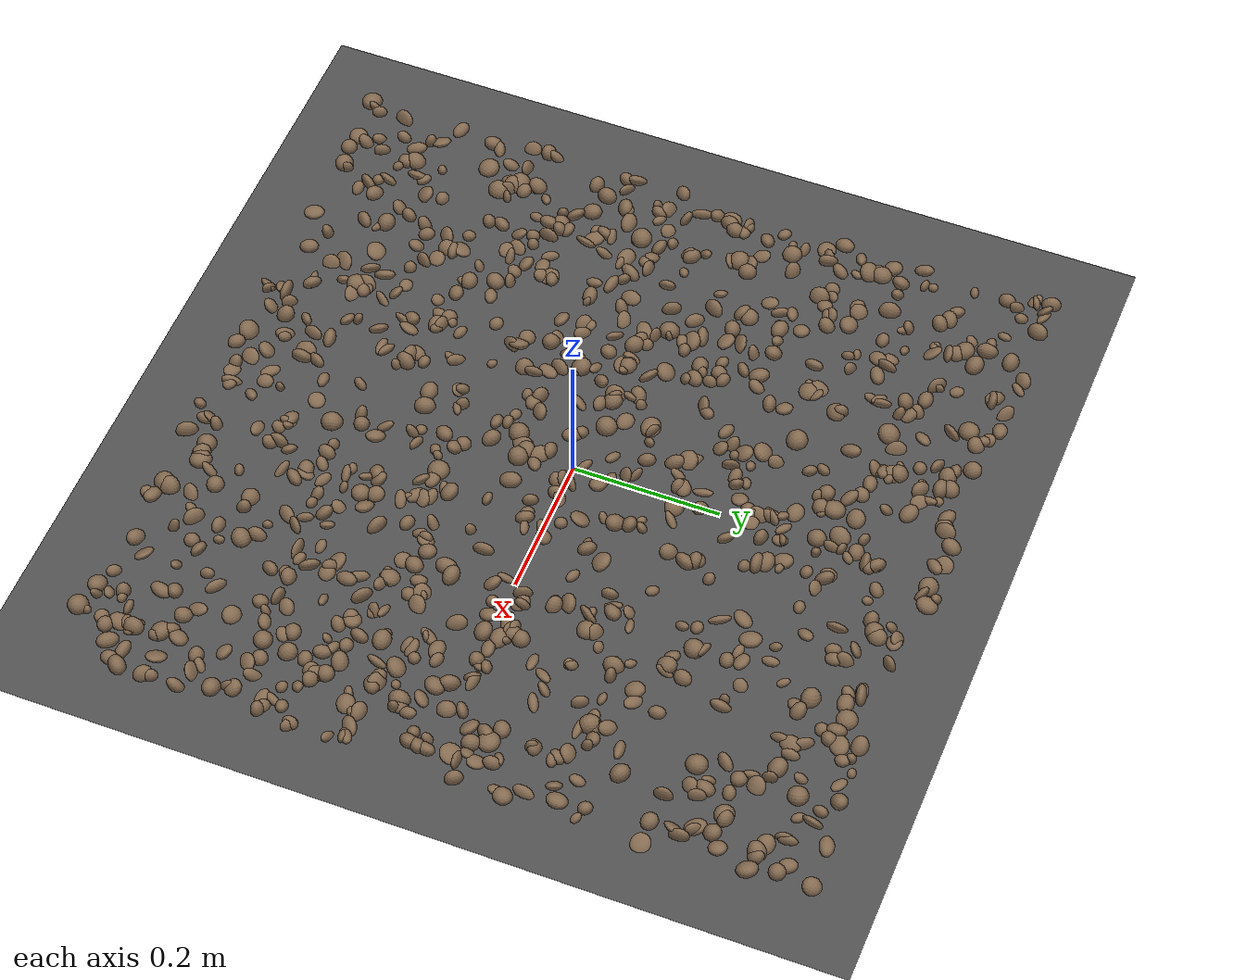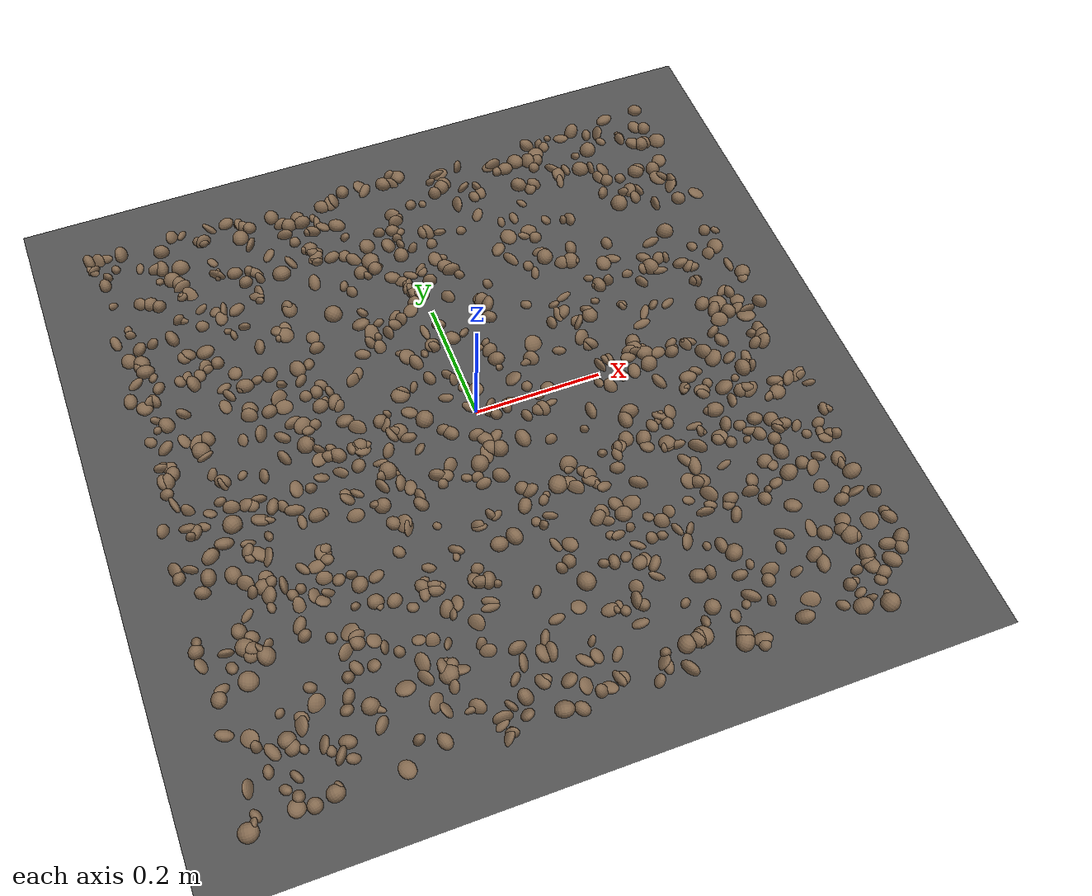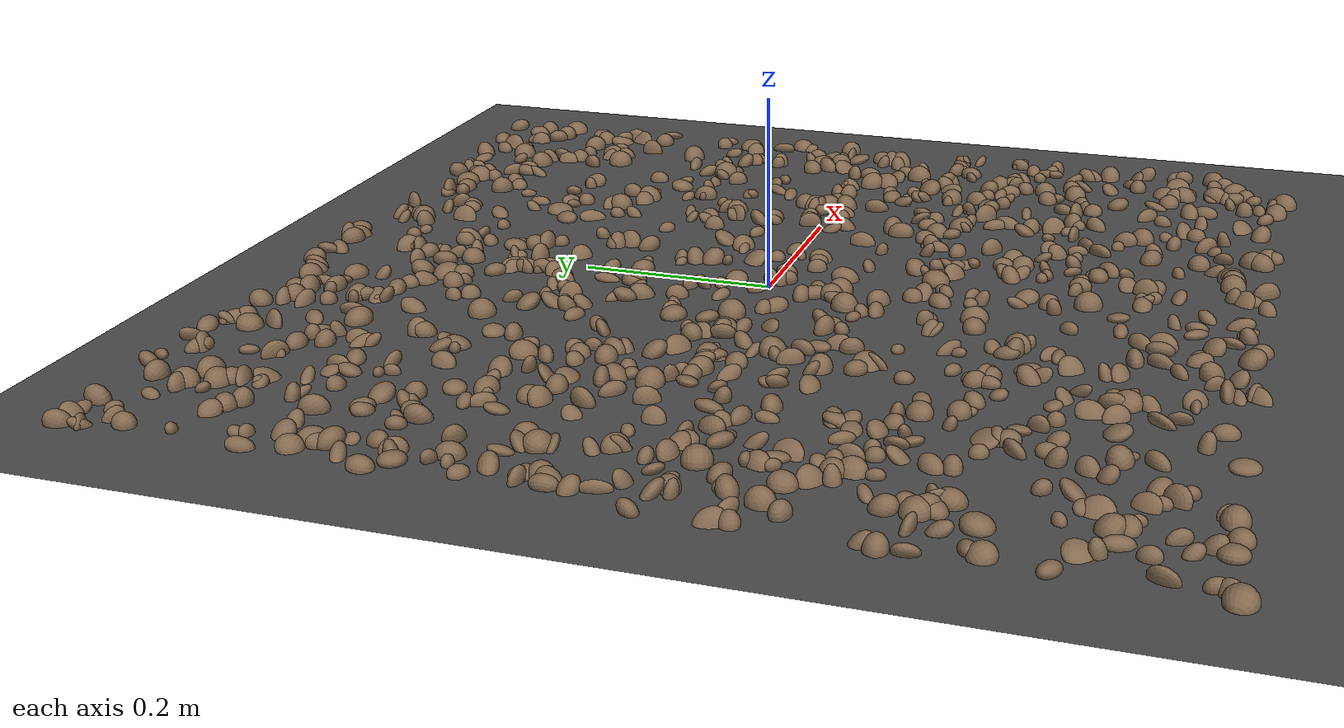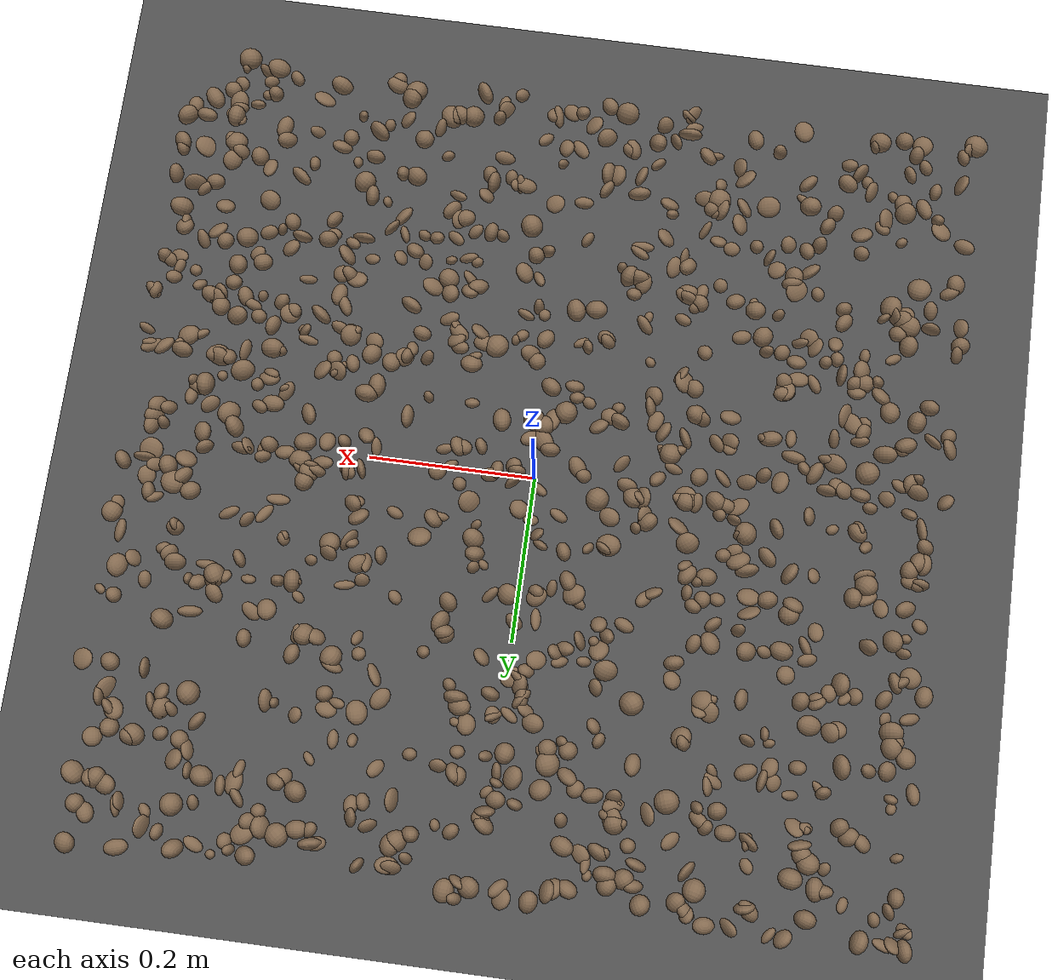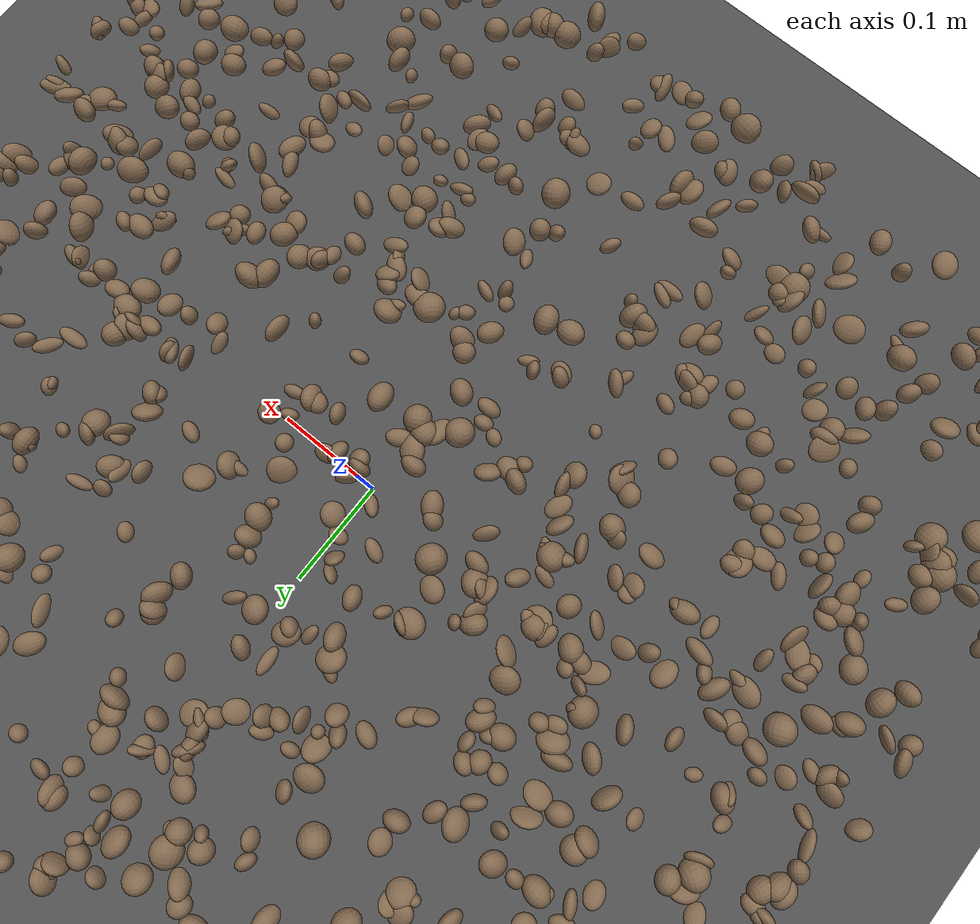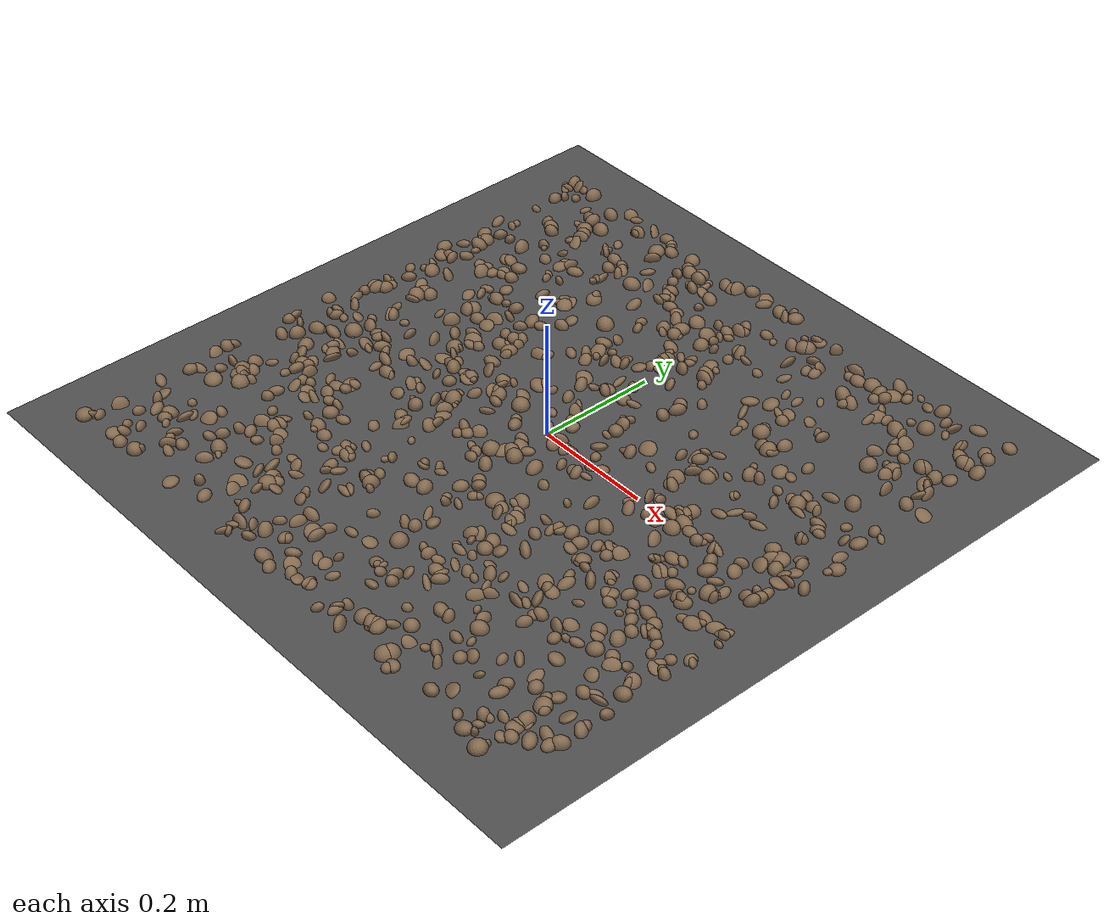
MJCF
<mujoco model="rocky_terrain_scene">
    <compiler angle="radian" inertiafromgeom="true" />
    <option timestep="0.002" gravity="0 0 -9.81" />

    <worldbody>
        <light name="sunlight" pos="5 5 5" dir="-1 -1 -1" diffuse="1 1 1" specular="0.5 0.5 0.5" ambient="0.5 0.5 0.5" />

        <geom name="ground_plane" type="plane" size="50 50 0.1" rgba="0.3 0.3 0.3 1" />

        <body name="rocky_terrain_body">

        </body>
    <body name="rock1" pos="0.4353633531592149 -0.4364276156961966 4.287308171434734e-05"><joint type="free" /><geom type="ellipsoid" size="0.014731630508670553 0.008797899626927707 0.011675101133326017" quat="0.3002451635102131 0.23317663290933505 0.29121947172853707 0.1753587318519148" rgba="0.5 0.4 0.3 1" /></body><body name="rock2" pos="-0.32503790170889413 0.11184406815544756 0.0006447662067914137"><joint type="free" /><geom type="ellipsoid" size="0.012859626729728877 0.0135028779343945 0.008587339216755087" quat="0.09525189811493665 0.04870602045374175 0.533565746355206 0.3224763350761156" rgba="0.5 0.4 0.3 1" /></body><body name="rock3" pos="0.3901343448415924 -0.15641230800601924 0.0005398129180077194"><joint type="free" /><geom type="ellipsoid" size="0.014604587856682092 0.009906621469801442 0.011435488196671787" quat="0.5180508637024476 0.21602569205285177 0.25659310420308296 0.00933034004161777" rgba="0.5 0.4 0.3 1" /></body><body name="rock4" pos="0.3091596776810186 -0.47558697058897237 0.0003598966228238819"><joint type="free" /><geom type="ellipsoid" size="0.011177535229694068 0.010236504024802003 0.014916785868328928" quat="0.5699800241458175 0.1193334528027926 0.26182145568336457 0.048865067368025476" rgba="0.5 0.4 0.3 1" /></body><body name="rock5" pos="-0.17336331567616736 -0.24755928444648534 0.00043556150706448583"><joint type="free" /><geom type="ellipsoid" size="0.011453315248661548 0.01104279744867952 0.009876662347312548" quat="0.23402949493842187 0.0901507574051524 0.31361040371551874 0.36220934394090704" rgba="0.5 0.4 0.3 1" /></body><body name="rock6" pos="-0.1922353618479853 0.053747146951129476 0.0009652878043586573"><joint type="free" /><geom type="ellipsoid" size="0.01384092802885524 0.009116592937414993 0.0138835895311995" quat="0.501099689360478 0.2317643202572263 0.15781999170957497 0.1093159986727208" rgba="0.5 0.4 0.3 1" /></body><body name="rock7" pos="-0.2046043037090005 -0.3231147150250626 7.011119213631922e-05"><joint type="free" /><geom type="ellipsoid" size="0.005164537574004134 0.008754745539337187 0.00999256935799467" quat="0.08209347865176486 0.44699466284076617 0.03177935054250698 0.439132507964962" rgba="0.5 0.4 0.3 1" /></body><body name="rock8" pos="0.009171253942743651 -0.1768668546757448 0.00015438048639390234"><joint type="free" /><geom type="ellipsoid" size="0.009931813436196445 0.010154475668692323 0.012783302167810406" quat="0.17678509558943553 0.05639435238668023 0.3517634752114647 0.4150570768124195" rgba="0.5 0.4 0.3 1" /></body><body name="rock9" pos="0.20888739014074398 0.2444528566163744 0.0008795262998979521"><joint type="free" /><geom type="ellipsoid" size="0.013893089501665637 0.0129755071858681 0.012460597846774148" quat="0.4790991224952349 0.1721218939028952 0.0522256337040826 0.2965533498977873" rgba="0.5 0.4 0.3 1" /></body><body name="rock10" pos="-0.1871674008850578 -0.33091154322436456 0.00023966448036626554"><joint type="free" /><geom type="ellipsoid" size="0.010398955445292532 0.00561921654158332 0.012455099440770254" quat="0.05959632826912789 0.03183546244225517 0.2355477760341588 0.6730204332544583" rgba="0.5 0.4 0.3 1" /></body><body name="rock11" pos="0.4327836799725393 -0.4287041525226938 0.0005664301396980464"><joint type="free" /><geom type="ellipsoid" size="0.007168240898345604 0.010958685741635308 0.008822616975748836" quat="0.007786938372910472 0.4029436751769716 0.4820357514504212 0.10723363499969663" rgba="0.5 0.4 0.3 1" /></body><body name="rock12" pos="0.10976405704178605 -0.22627012162233595 6.232472852642068e-05"><joint type="free" /><geom type="ellipsoid" size="0.007438482777253416 0.014238108025208578 0.01087200726210941" quat="0.35547854866852424 0.1293921894363692 0.3243950419838547 0.19073421991125192" rgba="0.5 0.4 0.3 1" /></body><body name="rock13" pos="0.14614332400088859 0.4058279771673967 0.0005433619254730839"><joint type="free" /><geom type="ellipsoid" size="0.010587646240763205 0.0085396590907581 0.008068632938643214" quat="0.15508135214600846 0.26895744307296077 0.35148632153503745 0.22447488324599335" rgba="0.5 0.4 0.3 1" /></body><body name="rock14" pos="-0.07525006285996327 0.07545354768035928 0.0007446953423215935"><joint type="free" /><geom type="ellipsoid" size="0.005566404969319308 0.010000850056663657 0.006891440801913116" quat="0.06485088311805415 0.17838376807615583 0.5324494150851906 0.22431593372059955" rgba="0.5 0.4 0.3 1" /></body><body name="rock15" pos="0.3366956489140558 0.401023298801384 0.0007685291182604317"><joint type="free" /><geom type="ellipsoid" size="0.01177952485388049 0.014587648002576063 0.01295858123443494" quat="0.4091665644679318 0.058083636213298664 0.2138226211983496 0.31892717812042" rgba="0.5 0.4 0.3 1" /></body><body name="rock16" pos="-0.29684056680292203 0.17150806045740508 0.0007392791993165853"><joint type="free" /><geom type="ellipsoid" size="0.007299402527408036 0.0066078701583553515 0.010263072909843358" quat="0.4447060473670304 0.16307413710842897 0.1832330205550302 0.20898679496951045" rgba="0.5 0.4 0.3 1" /></body><body name="rock17" pos="-0.0959240396645542 0.1852748909811961 0.0009007573040563329"><joint type="free" /><geom type="ellipsoid" size="0.006790987701519119 0.006072846046712498 0.0060268884606659145" quat="0.04458503313080281 0.409537802076528 0.04823809107465804 0.4976390737180111" rgba="0.5 0.4 0.3 1" /></body><body name="rock18" pos="0.24261098552600724 -0.15565307904158454 0.0008701539283449676"><joint type="free" /><geom type="ellipsoid" size="0.008731795082340628 0.008540462160031495 0.005698068000697664" quat="0.4435622313466734 0.2666379070603128 0.09187727040076522 0.19792259119224848" rgba="0.5 0.4 0.3 1" /></body><body name="rock19" pos="0.42021234295281895 0.14662938384317759 0.00016937561199887707"><joint type="free" /><geom type="ellipsoid" size="0.011438590709728576 0.007883049207572986 0.010552361230090797" quat="0.5278317530324299 0.15963521307958223 0.05266845488867712 0.2598645789993107" rgba="0.5 0.4 0.3 1" /></body><body name="rock20" pos="0.008466673897112753 0.4046058987977056 0.0001477768620763067"><joint type="free" /><geom type="ellipsoid" size="0.009366499776311049 0.009438525055674859 0.010900703176066479" quat="0.2765191700078351 0.11500376117235268 0.31906800053151685 0.2894090682882953" rgba="0.5 0.4 0.3 1" /></body><body name="rock21" pos="-0.24733193865794922 0.001718109933533718 0.0002913350588917548"><joint type="free" /><geom type="ellipsoid" size="0.010339135874986454 0.005152595044495011 0.014580523236998742" quat="0.11187632876137694 0.24321062840259886 0.33345224829254433 0.3114607945434799" rgba="0.5 0.4 0.3 1" /></body><body name="rock22" pos="0.38191217750403594 -0.3543256345183968 0.0004997970665235583"><joint type="free" /><geom type="ellipsoid" size="0.005167783008181498 0.014217770590435833 0.00899958507779472" quat="0.3589487697869161 0.06850116650049518 0.4850356926192099 0.08751437109337884" rgba="0.5 0.4 0.3 1" /></body><body name="rock23" pos="-0.410698115944203 0.09198264583455684 0.00028513607622143624"><joint type="free" /><geom type="ellipsoid" size="0.010326012536883925 0.00689455208663893 0.014376451840603675" quat="0.014148000609251895 0.27406631724734254 0.2218674107807098 0.48991827136269583" rgba="0.5 0.4 0.3 1" /></body><body name="rock24" pos="0.3693943322280664 -0.017252931473749844 0.0009559218345466816"><joint type="free" /><geom type="ellipsoid" size="0.01009475218326371 0.013104111161257776 0.014995544179606975" quat="0.6008082915035371 0.1710988065014992 0.09944634219596508 0.12864655979899867" rgba="0.5 0.4 0.3 1" /></body><body name="rock25" pos="0.009230133758635684 0.28768664525416454 0.000168671378163726"><joint type="free" /><geom type="ellipsoid" size="0.005331772507290622 0.00772569021914537 0.01395576788376112" quat="0.30104608408668143 0.06810556446952858 0.213585021406551 0.417263330037239" rgba="0.5 0.4 0.3 1" /></body><body name="rock26" pos="-0.2884971585088436 -0.14641528349381172 0.00018698001272506149"><joint type="free" /><geom type="ellipsoid" size="0.009372756573055155 0.0094962496203588 0.014046026982089104" quat="0.2706694653773336 0.16331000170774287 0.25112549676705986 0.3148950361478636" rgba="0.5 0.4 0.3 1" /></body><body name="rock27" pos="-0.3073422573755338 -0.06845482809404191 0.0005816929930934716"><joint type="free" /><geom type="ellipsoid" size="0.007691832557113691 0.00975170297457234 0.014830361276237873" quat="0.2781733082151447 0.2720433869686439 0.2558968377231645 0.19388646709304694" rgba="0.5 0.4 0.3 1" /></body><body name="rock28" pos="-0.09931855704989989 0.16463986050050805 0.0009349259492060396"><joint type="free" /><geom type="ellipsoid" size="0.007042844652717661 0.012250542669136718 0.009840220972198426" quat="0.31828711639073515 0.10032306462184305 0.39287718612794154 0.18851263285948033" rgba="0.5 0.4 0.3 1" /></body><body name="rock29" pos="0.2978152979724935 -0.13712734897897982 0.0003752512410231538"><joint type="free" /><geom type="ellipsoid" size="0.005466294630032607 0.0053117126770339815 0.012805447867810543" quat="0.33799619317934576 0.206318984101878 0.2150143391455307 0.2406704835732456" rgba="0.5 0.4 0.3 1" /></body><body name="rock30" pos="0.009369297002832622 -0.0732845324963074 0.0009774124126457411"><joint type="free" /><geom type="ellipsoid" size="0.013378742515621277 0.014758853261079289 0.013004625167071494" quat="0.16866331670081894 0.19904646198758522 0.29756275374680297 0.33472746756479294" rgba="0.5 0.4 0.3 1" /></body><body name="rock31" pos="-0.11022265714208945 0.17683483613464013 0.00012525402727751745"><joint type="free" /><geom type="ellipsoid" size="0.008830271936694147 0.014935494645418539 0.00738998820736535" quat="0.3131967041298136 0.1395639321016857 0.26664390238129004 0.28059546138721064" rgba="0.5 0.4 0.3 1" /></body><body name="rock32" pos="-0.30389067078751897 -0.16648928770664917 6.307674916187922e-05"><joint type="free" /><geom type="ellipsoid" size="0.009654836008121729 0.005787154422614863 0.013261244419516201" quat="0.2275417963558177 0.24598644100462289 0.22767532912178062 0.29879643351777874" rgba="0.5 0.4 0.3 1" /></body><body name="rock33" pos="-0.21301807487278135 0.17279773562497924 0.0003400232934156756"><joint type="free" /><geom type="ellipsoid" size="0.012376500836532559 0.008190711757194083 0.008256658996753033" quat="0.36891722467144655 0.1918408005146895 0.27148445096087304 0.1677575238529909" rgba="0.5 0.4 0.3 1" /></body><body name="rock34" pos="0.31481124254942494 0.23604864391793468 1.4070294918347216e-05"><joint type="free" /><geom type="ellipsoid" size="0.011163555966052365 0.01015618621056968 0.008516718565135237" quat="0.2337232338831469 0.24192510640211926 0.2742250630893436 0.2501265966253903" rgba="0.5 0.4 0.3 1" /></body><body name="rock35" pos="-0.08486698548911253 0.3458548824898747 7.79875798137194e-05"><joint type="free" /><geom type="ellipsoid" size="0.008140234556486279 0.009960188020114412 0.01456261835765102" quat="0.2757421773823024 0.3499777312449759 0.37200999704693094 0.0022700943257907328" rgba="0.5 0.4 0.3 1" /></body><body name="rock36" pos="-0.45254833032033726 0.4597535090206576 0.0009270691082479851"><joint type="free" /><geom type="ellipsoid" size="0.00945712132461625 0.007251812293976784 0.0068807934612651125" quat="0.31527849705159194 0.07893121664801502 0.3242020447822332 0.2815882415181598" rgba="0.5 0.4 0.3 1" /></body><body name="rock37" pos="0.44579725699100614 0.42499651566534036 0.0008682024260452847"><joint type="free" /><geom type="ellipsoid" size="0.011873645117052908 0.009114935143412651 0.014279294691798707" quat="0.23359148081733663 0.28732476760482156 0.3438761467016465 0.1352076048761953" rgba="0.5 0.4 0.3 1" /></body><body name="rock38" pos="-0.23077205801661038 0.23796695713449745 0.0007266300725145534"><joint type="free" /><geom type="ellipsoid" size="0.013078653445222646 0.01312829224187793 0.008036396745582021" quat="0.6275151903857383 0.12629866787544197 0.07884137830903232 0.16734476342978735" rgba="0.5 0.4 0.3 1" /></body><body name="rock39" pos="0.27495723019034424 -0.10182991405412722 0.0005286518895263368"><joint type="free" /><geom type="ellipsoid" size="0.012090951965496135 0.0063464697202507735 0.013806126159621134" quat="0.06190023121925947 0.3563125310301169 0.3305570184772388 0.25123021927338474" rgba="0.5 0.4 0.3 1" /></body><body name="rock40" pos="0.10190992852002245 0.22412603548704235 0.0006265929674175051"><joint type="free" /><geom type="ellipsoid" size="0.0072390868164876 0.01032052296690819 0.007535709497523753" quat="0.1897194939123709 0.0010979239684304136 0.4394848155941558 0.36969776652504277" rgba="0.5 0.4 0.3 1" /></body><body name="rock41" pos="-0.10129244808750715 -0.26398055822248967 0.0005932948777210777"><joint type="free" /><geom type="ellipsoid" size="0.01352365734146246 0.008032008593283277 0.010060547055451615" quat="0.292411931410603 0.2583349582657896 0.2872574773809783 0.16199563294262906" rgba="0.5 0.4 0.3 1" /></body><body name="rock42" pos="-0.4578116594823708 0.09917100650498212 0.0005410666844699422"><joint type="free" /><geom type="ellipsoid" size="0.01035287544252516 0.008351577308201498 0.01429849717482735" quat="0.41792495391508777 0.05511472630492655 0.2613765027545038 0.2655838170254819" rgba="0.5 0.4 0.3 1" /></body><body name="rock43" pos="0.17742067696594532 -0.1313217525039424 0.0004237427998820894"><joint type="free" /><geom type="ellipsoid" size="0.011726687545034482 0.006760740562226853 0.012058278797535432" quat="0.3199834353627085 0.14224775943303655 0.2596535472292484 0.2781152579750066" rgba="0.5 0.4 0.3 1" /></body><body name="rock44" pos="-0.3642538278294408 -0.4330545888460501 0.0007838025530637823"><joint type="free" /><geom type="ellipsoid" size="0.008081258335772439 0.007424574538990003 0.0069765776075680856" quat="0.26892298099834855 0.20084577503303733 0.13408358536536946 0.39614765860324475" rgba="0.5 0.4 0.3 1" /></body><body name="rock45" pos="0.20201067809841033 0.4450778599412597 0.0008153837304329893"><joint type="free" /><geom type="ellipsoid" size="0.007951620445355424 0.01098435906934815 0.00789847143796127" quat="0.26575278250504897 0.39730633821125366 0.007774800631679516 0.32916607865201786" rgba="0.5 0.4 0.3 1" /></body><body name="rock46" pos="0.32098570294183393 0.1658425001907956 0.0006296870693942802"><joint type="free" /><geom type="ellipsoid" size="0.00524900961115034 0.007449170001523361 0.008984249057795206" quat="0.30271053189813013 0.2107925353078206 0.3269362795518288 0.15956065324222038" rgba="0.5 0.4 0.3 1" /></body><body name="rock47" pos="0.4212657449581003 0.052689657540274326 0.0009399013517522193"><joint type="free" /><geom type="ellipsoid" size="0.00901355526323096 0.011695322385700061 0.014452153911142115" quat="0.1484561933740157 0.11845606103865615 0.327889305974469 0.40519843961285906" rgba="0.5 0.4 0.3 1" /></body><body name="rock48" pos="-0.29081203838815683 -0.42190544498513505 7.446578360162593e-05"><joint type="free" /><geom type="ellipsoid" size="0.013771335976576943 0.007487090545166313 0.01099011749598467" quat="0.05217649269255009 0.6089811885642802 0.2761031594167907 0.06273915932637901" rgba="0.5 0.4 0.3 1" /></body><body name="rock49" pos="0.05303644545032915 0.30070946353806594 0.0009455217325406435"><joint type="free" /><geom type="ellipsoid" size="0.005355022779054883 0.005032848692645237 0.006967956258968622" quat="0.22817765409147844 0.34280503744983004 0.21823784506504046 0.21077946339365106" rgba="0.5 0.4 0.3 1" /></body><body name="rock50" pos="-0.41347914103803063 -0.35914164670635274 8.370703241957201e-05"><joint type="free" /><geom type="ellipsoid" size="0.007341874026708623 0.008001391049536614 0.005860793018493725" quat="0.4203672699697295 0.3390628564541061 0.18683307575942396 0.05373679781674037" rgba="0.5 0.4 0.3 1" /></body><body name="rock51" pos="0.3645976766376412 0.17218031071085105 0.0008236047403533276"><joint type="free" /><geom type="ellipsoid" size="0.00790863773338115 0.007497927098500175 0.013440917414936457" quat="0.16473152164811555 0.33278921120549576 0.3433667949286104 0.15911247221777822" rgba="0.5 0.4 0.3 1" /></body><body name="rock52" pos="0.43018751281053036 -0.12717301708413697 0.0005212466157927264"><joint type="free" /><geom type="ellipsoid" size="0.005397348594528705 0.007611438223419108 0.011181643801106388" quat="0.2334703377730346 0.14489924752923292 0.38375479354054437 0.23787562115718813" rgba="0.5 0.4 0.3 1" /></body><body name="rock53" pos="-0.03161295972165579 0.21630844434595864 0.0004076189225534487"><joint type="free" /><geom type="ellipsoid" size="0.011317417811851076 0.01286087465483303 0.005869306672250361" quat="0.06417755184765063 0.3398679184163276 0.5143097975827203 0.08164473215330136" rgba="0.5 0.4 0.3 1" /></body><body name="rock54" pos="-0.18473524528503038 0.003380611529518851 0.0003231191807550924"><joint type="free" /><geom type="ellipsoid" size="0.011503733074190274 0.011403067810417078 0.012455143275696443" quat="0.39512682172874497 0.1518501169388343 0.2442535330173454 0.2087695283150754" rgba="0.5 0.4 0.3 1" /></body><body name="rock55" pos="0.15593737332024005 -0.22569791643199644 3.943354439428048e-05"><joint type="free" /><geom type="ellipsoid" size="0.01469596972008276 0.01154426275400008 0.006760663818134456" quat="0.17776375663208532 0.04149329764141334 0.6827127444045994 0.09803020132190185" rgba="0.5 0.4 0.3 1" /></body><body name="rock56" pos="0.4025208309848205 -0.10153318339281603 0.00098128989074003"><joint type="free" /><geom type="ellipsoid" size="0.008997070153981865 0.014113023426183768 0.014436354501796606" quat="0.1819663055792942 0.38529958970260264 0.17921623829120756 0.25351786642689567" rgba="0.5 0.4 0.3 1" /></body><body name="rock57" pos="0.038348852470966976 -0.1774305157121976 0.0007140798084060566"><joint type="free" /><geom type="ellipsoid" size="0.006869609305319665 0.007565803543318576 0.00888605626168076" quat="0.3101527504676717 0.017726511987433836 0.2983728495103843 0.3737478880345102" rgba="0.5 0.4 0.3 1" /></body><body name="rock58" pos="0.2062059934328615 0.25505813022441537 0.0006892800349155701"><joint type="free" /><geom type="ellipsoid" size="0.009114097239340663 0.00605410030631718 0.013666940187692052" quat="0.18008808164532955 0.3614632406817866 0.0387497684924596 0.41969890918042424" rgba="0.5 0.4 0.3 1" /></body><body name="rock59" pos="0.31372241000566115 -0.07235965793234578 0.00036687360584984353"><joint type="free" /><geom type="ellipsoid" size="0.005316227084947774 0.00863272092662664 0.010696385481772314" quat="0.2871337845650213 0.10570858672501901 0.11408742998687388 0.4930701987230858" rgba="0.5 0.4 0.3 1" /></body><body name="rock60" pos="-0.263327152703808 0.1503632908379945 0.000995748907159601"><joint type="free" /><geom type="ellipsoid" size="0.005904042175784485 0.014357464772017773 0.007724059928299499" quat="0.2777723146773702 0.31913922697402025 0.13418679694552202 0.2689016614030877" rgba="0.5 0.4 0.3 1" /></body><body name="rock61" pos="0.2199009307271932 -0.4409228923994716 7.947677770244988e-05"><joint type="free" /><geom type="ellipsoid" size="0.010087429218317038 0.013664532963429052 0.005979811866395881" quat="0.28854464099516314 0.21236350507582535 0.09847193313596668 0.40061992079304487" rgba="0.5 0.4 0.3 1" /></body><body name="rock62" pos="0.4112945990229009 0.1567808636183754 0.0002557639105845638"><joint type="free" /><geom type="ellipsoid" size="0.012988321617266062 0.008301139564278404 0.013009699795195763" quat="0.3611248969043359 0.0903620694086576 0.4022167462399289 0.14629628744707762" rgba="0.5 0.4 0.3 1" /></body><body name="rock63" pos="-0.09892518652903837 0.06844264503982911 9.971675637159606e-05"><joint type="free" /><geom type="ellipsoid" size="0.013260098149924616 0.010216302718068879 0.01497745564056939" quat="0.25024132400671906 0.2621090940916492 0.2847438567974411 0.20290572510419064" rgba="0.5 0.4 0.3 1" /></body><body name="rock64" pos="-0.11663025097063795 0.36331978484890504 0.0008694273593042289"><joint type="free" /><geom type="ellipsoid" size="0.0131799890524117 0.009860511176466889 0.009037846033050984" quat="0.3531284007526175 0.5465376657904524 0.025063312321057112 0.07527062113587298" rgba="0.5 0.4 0.3 1" /></body><body name="rock65" pos="0.05656661836616739 0.27187232755926916 0.0009480499081711147"><joint type="free" /><geom type="ellipsoid" size="0.008427642748604386 0.01453768564834031 0.014426893182883312" quat="0.24771709493096325 0.2573783107173454 0.23740115847910656 0.25750343587258484" rgba="0.5 0.4 0.3 1" /></body><body name="rock66" pos="0.12675978494319196 0.08791408450879856 0.0007253550675711389"><joint type="free" /><geom type="ellipsoid" size="0.007709945616138138 0.01466521243603482 0.014291838973958387" quat="0.35221762717682187 0.12262803799577449 0.4100764210528375 0.1150779137745662" rgba="0.5 0.4 0.3 1" /></body><body name="rock67" pos="0.37883573288214656 -0.03320472297222943 0.0008170746511797464"><joint type="free" /><geom type="ellipsoid" size="0.013298870359448843 0.014855508948841308 0.010387002762877115" quat="0.1870338284068885 0.25217999878254527 0.5332884951011375 0.027497677709428642" rgba="0.5 0.4 0.3 1" /></body><body name="rock68" pos="0.26950944560350387 -0.20062649940468624 1.3475731981964723e-05"><joint type="free" /><geom type="ellipsoid" size="0.014887495076917615 0.00935717010189335 0.009469181914127687" quat="0.21837736907813052 0.31559361126821867 0.21163321891655662 0.25439580073709417" rgba="0.5 0.4 0.3 1" /></body><body name="rock69" pos="0.10622195148913538 -0.3809971224897054 0.0005645713025652497"><joint type="free" /><geom type="ellipsoid" size="0.011925808926745773 0.009412342551691513 0.009114965370578314" quat="0.36956433309818776 0.07157274524559361 0.3999296617992028 0.15893325985701584" rgba="0.5 0.4 0.3 1" /></body><body name="rock70" pos="-0.14178604062564293 0.386437628829963 0.00013967959804746466"><joint type="free" /><geom type="ellipsoid" size="0.012838644050685244 0.014014655569790667 0.008238304597062672" quat="0.10034583869516474 0.15216256468003805 0.1496603061552561 0.597831290469541" rgba="0.5 0.4 0.3 1" /></body><body name="rock71" pos="0.2606859763306506 -0.1874988429561163 0.00014240434038802874"><joint type="free" /><geom type="ellipsoid" size="0.007207685937811917 0.008139627063087247 0.014054068118755324" quat="0.4089563918719347 0.3908108367348209 0.09519412925185318 0.1050386421413912" rgba="0.5 0.4 0.3 1" /></body><body name="rock72" pos="-0.06479549570678245 -0.43679986889067013 0.0001332160459891868"><joint type="free" /><geom type="ellipsoid" size="0.008338860439533323 0.008627810122435998 0.01131746798420694" quat="0.5764054677722361 0.11907434073973348 0.29881429455620234 0.005705896931828063" rgba="0.5 0.4 0.3 1" /></body><body name="rock73" pos="-0.21211221614237552 0.40291336848360837 0.00018398509114883388"><joint type="free" /><geom type="ellipsoid" size="0.013118515585387933 0.005826861147328207 0.008585450217052863" quat="0.4248658196412739 0.28590133945770774 0.07234429739490358 0.21688854350611486" rgba="0.5 0.4 0.3 1" /></body><body name="rock74" pos="-0.3503663302085859 -0.26310091741813646 0.0003921021638068509"><joint type="free" /><geom type="ellipsoid" size="0.010094093892616077 0.012014296978418167 0.008539025998945099" quat="0.37639529299311963 0.4087764737362069 0.1769077552238328 0.03792047804684057" rgba="0.5 0.4 0.3 1" /></body><body name="rock75" pos="0.3153159007586661 0.08489377327670256 0.0006722561625715259"><joint type="free" /><geom type="ellipsoid" size="0.006593952566380976 0.0051970593272813725 0.013849612183430702" quat="0.1742159022290084 0.0702413289503698 0.36195443927313226 0.3935883295474896" rgba="0.5 0.4 0.3 1" /></body><body name="rock76" pos="-0.3757162058825547 -0.15959445943604234 0.00033108064304044737"><joint type="free" /><geom type="ellipsoid" size="0.0075755921937310025 0.01168462724699847 0.011124334454805391" quat="0.3862635718182606 0.03151617944630464 0.3210538821415835 0.26116636659385134" rgba="0.5 0.4 0.3 1" /></body><body name="rock77" pos="0.010650154795853184 0.28640288511142487 6.0339237291351376e-05"><joint type="free" /><geom type="ellipsoid" size="0.010506237682218644 0.006562639988355225 0.009165863316135184" quat="0.2567918466383731 0.16260289374919368 0.27170524086302195 0.30890001874941125" rgba="0.5 0.4 0.3 1" /></body><body name="rock78" pos="0.26979282814154315 0.018924508136230367 0.0004997971860042211"><joint type="free" /><geom type="ellipsoid" size="0.0053391605555968115 0.012833697141213334 0.011140884005392612" quat="0.2887304662870646 0.24012456845701427 0.20469694917586798 0.2664480160800532" rgba="0.5 0.4 0.3 1" /></body><body name="rock79" pos="-0.2945629024114387 -0.035293871459951665 0.00011755931631106154"><joint type="free" /><geom type="ellipsoid" size="0.014034300192078141 0.006916091255682974 0.010943733729197214" quat="0.17527984882028308 0.34895988406814155 0.2811916724985046 0.19456859461307086" rgba="0.5 0.4 0.3 1" /></body><body name="rock80" pos="-0.43800128276206185 -0.049495566601575613 0.0004936474574519147"><joint type="free" /><geom type="ellipsoid" size="0.011014150613527906 0.00624224707064504 0.006690510017846324" quat="0.145428122788507 0.04625158880360963 0.3667137807322559 0.4416065076756275" rgba="0.5 0.4 0.3 1" /></body><body name="rock81" pos="-0.2117392440542023 -0.41780207824403715 1.0106754772994164e-05"><joint type="free" /><geom type="ellipsoid" size="0.005710113786910779 0.014190745493518935 0.014900182880780845" quat="0.24813952567439146 0.033341047943962115 0.46142199308373283 0.2570974332979136" rgba="0.5 0.4 0.3 1" /></body><body name="rock82" pos="-0.2567587203776541 0.03400921725166428 0.0006576129954868415"><joint type="free" /><geom type="ellipsoid" size="0.011485235951861794 0.0066532824169325214 0.012849026743326424" quat="0.6279230878885733 0.03792024665405309 0.18386571642366095 0.15029094903371273" rgba="0.5 0.4 0.3 1" /></body><body name="rock83" pos="0.05934131600743042 0.4207667847704346 0.000405212627584965"><joint type="free" /><geom type="ellipsoid" size="0.007383916544470468 0.005958455364860681 0.0058305064034332435" quat="0.2520573638217498 0.17330346127489604 0.3519134171849781 0.22272575771837594" rgba="0.5 0.4 0.3 1" /></body><body name="rock84" pos="-0.2510341701231855 0.31875071229561514 0.0007896110830383148"><joint type="free" /><geom type="ellipsoid" size="0.005778201805460738 0.0120408963366196 0.006047416384826022" quat="0.03974408671921916 0.2969098042525732 0.23497872169021705 0.42836738733799057" rgba="0.5 0.4 0.3 1" /></body><body name="rock85" pos="0.40062873685394695 0.012608865017763371 0.00044695900850978833"><joint type="free" /><geom type="ellipsoid" size="0.011060402024102974 0.012086226986962443 0.0070870076715043775" quat="0.3495953076293736 0.4233252546349737 0.10718804711932267 0.11989139061632999" rgba="0.5 0.4 0.3 1" /></body><body name="rock86" pos="-0.45366768773211474 0.18751069467827752 0.0003137218100177536"><joint type="free" /><geom type="ellipsoid" size="0.013515743989470818 0.011774074068201655 0.007456971048478457" quat="0.2607182102007541 0.12488991536144772 0.39566009510600086 0.21873177933179733" rgba="0.5 0.4 0.3 1" /></body><body name="rock87" pos="-0.440326988831797 -0.30095602532604526 0.0003306596168394459"><joint type="free" /><geom type="ellipsoid" size="0.014543649690142584 0.010757247528626519 0.014688099941071873" quat="0.23668202740484942 0.34112020387332065 0.21067508244389047 0.2115226862779395" rgba="0.5 0.4 0.3 1" /></body><body name="rock88" pos="-0.2962438252799695 0.021959592894209012 9.678122169212533e-05"><joint type="free" /><geom type="ellipsoid" size="0.007326965499135831 0.014113236273931046 0.012321026684122806" quat="0.5517353764181282 0.26668500701483155 0.053947861300164504 0.12763175526687573" rgba="0.5 0.4 0.3 1" /></body><body name="rock89" pos="0.3307204824966483 -0.11960797763373898 0.0003716449896602246"><joint type="free" /><geom type="ellipsoid" size="0.0065126993043331345 0.009227613267967918 0.008300464161694403" quat="0.16932613975672506 0.36257551532048454 0.2911189139884464 0.17697943093434407" rgba="0.5 0.4 0.3 1" /></body><body name="rock90" pos="0.2631180059734023 -0.26869456165767247 0.0004926260806358019"><joint type="free" /><geom type="ellipsoid" size="0.010082355530167857 0.006288269346091023 0.006563693550843987" quat="0.010133630748586272 0.14717123115176556 0.5348089246855169 0.3078862134141313" rgba="0.5 0.4 0.3 1" /></body><body name="rock91" pos="-0.18345846004467214 -0.0008450694737601738 2.67373252813774e-05"><joint type="free" /><geom type="ellipsoid" size="0.01455805753138754 0.006652963613626437 0.014372827420373997" quat="0.24672319489224065 0.2731793136865461 0.2931956324824367 0.1869018589387765" rgba="0.5 0.4 0.3 1" /></body><body name="rock92" pos="0.39227784268676535 -0.10313410591644001 0.00077027525860832"><joint type="free" /><geom type="ellipsoid" size="0.01187558877175995 0.009115499049424148 0.010377265261272445" quat="0.14184120064675976 0.354687264473771 0.08889621817801596 0.4145753167014532" rgba="0.5 0.4 0.3 1" /></body><body name="rock93" pos="0.04041593708180313 0.36201855167833663 0.0008793380611025313"><joint type="free" /><geom type="ellipsoid" size="0.011340328126549188 0.010090051437785422 0.009129484131124578" quat="0.26206181775680354 0.2609532121060685 0.19979420712504423 0.2771907630120838" rgba="0.5 0.4 0.3 1" /></body><body name="rock94" pos="-0.37932043022983597 -0.186727844689071 0.0009024343200820567"><joint type="free" /><geom type="ellipsoid" size="0.013666427370634514 0.008699084394784343 0.012911713003048504" quat="0.3862935568423127 0.14403354592920103 0.11684423634629254 0.3528286608821937" rgba="0.5 0.4 0.3 1" /></body><body name="rock95" pos="-0.45544520838948144 0.263144047478163 0.0009618075655633533"><joint type="free" /><geom type="ellipsoid" size="0.013968832892757067 0.012482962693139959 0.01118051850633853" quat="0.36942641112342145 0.014579276629492639 0.17775464181159717 0.4382396704354887" rgba="0.5 0.4 0.3 1" /></body><body name="rock96" pos="-0.47622698909076877 0.11716575809676255 0.0007918378166950266"><joint type="free" /><geom type="ellipsoid" size="0.009912763600226417 0.006779401131345198 0.008265647227260177" quat="0.1655995278612564 0.08926580551667448 0.2896111055813127 0.4555235610407564" rgba="0.5 0.4 0.3 1" /></body><body name="rock97" pos="-0.3905517654949454 0.25107905094135075 0.0005777081662121353"><joint type="free" /><geom type="ellipsoid" size="0.010475370983216664 0.007971432020155 0.011467985880557398" quat="0.2266777197188551 0.32304966625245307 0.2532488576953392 0.19702375633335262" rgba="0.5 0.4 0.3 1" /></body><body name="rock98" pos="-0.23355397457494342 0.1467440464006129 0.0009204295533033781"><joint type="free" /><geom type="ellipsoid" size="0.007018544084854994 0.010560373944079104 0.011513994596525287" quat="0.1486714207680834 0.16674229904515034 0.29317211243917024 0.39141416774759596" rgba="0.5 0.4 0.3 1" /></body><body name="rock99" pos="0.28728988716690795 -0.40717489973605003 0.0008244529258482764"><joint type="free" /><geom type="ellipsoid" size="0.010333573244866261 0.00965759074464989 0.009847324164904005" quat="0.022294192166658452 0.45107979542834825 0.47214344516210843 0.05448256724288483" rgba="0.5 0.4 0.3 1" /></body><body name="rock100" pos="0.03483147036303025 -0.2828745838738256 0.00030661817441306774"><joint type="free" /><geom type="ellipsoid" size="0.010450157368433632 0.012083460959438273 0.010067965593762346" quat="0.16900945944207382 0.23154995607378628 0.3064909414362524 0.29294964304788756" rgba="0.5 0.4 0.3 1" /></body><body name="rock101" pos="-0.12166853163039126 -0.16421063487999032 0.00044702647173407585"><joint type="free" /><geom type="ellipsoid" size="0.006840114618924737 0.005957639581827007 0.00566316854717657" quat="0.13466986810202514 0.16690116028185645 0.3307683561281918 0.3676606154879266" rgba="0.5 0.4 0.3 1" /></body><body name="rock102" pos="-0.41663221916768434 -0.45017483540583414 5.822520022676614e-05"><joint type="free" /><geom type="ellipsoid" size="0.0062281901415575155 0.009965090897227798 0.011521599356711654" quat="0.4869168466457479 0.3117512866069343 0.058563400912826816 0.14276846583449096" rgba="0.5 0.4 0.3 1" /></body><body name="rock103" pos="0.3577369647060924 0.08906367836818196 0.00011311012079390382"><joint type="free" /><geom type="ellipsoid" size="0.006524878879708204 0.006682214794631123 0.013602424456438039" quat="0.18358349789909245 0.18837409485502188 0.3639544081287272 0.2640879991171585" rgba="0.5 0.4 0.3 1" /></body><body name="rock104" pos="-0.2852731677367548 -0.297406976133083 6.40422745102498e-05"><joint type="free" /><geom type="ellipsoid" size="0.012297318809159458 0.010149094236316672 0.011816418703858168" quat="0.3184464672650347 0.324577781453496 0.3324748634149319 0.024500887866537327" rgba="0.5 0.4 0.3 1" /></body><body name="rock105" pos="0.42883451293028774 -0.2963428273975437 0.0002281655125924984"><joint type="free" /><geom type="ellipsoid" size="0.006798885811084157 0.011475346806193786 0.011713174199627644" quat="0.35953322451564906 0.20144323726553992 0.3774159898240569 0.061607548394754165" rgba="0.5 0.4 0.3 1" /></body><body name="rock106" pos="0.3443267154209615 -0.15001540269884694 0.00037599247265694946"><joint type="free" /><geom type="ellipsoid" size="0.01260482094755043 0.011406724689222455 0.008111096100471444" quat="0.2603108450902491 0.3183121051255377 0.2417473019608021 0.1796297478234111" rgba="0.5 0.4 0.3 1" /></body><body name="rock107" pos="0.3923194066501249 0.1740903204801707 0.0008143171351137978"><joint type="free" /><geom type="ellipsoid" size="0.007147774712780183 0.012185195425029613 0.005419435115909072" quat="0.30107661630514876 0.21844615045529583 0.25777944967080235 0.22269778356875314" rgba="0.5 0.4 0.3 1" /></body><body name="rock108" pos="-0.35348598899282546 0.42658775151255357 0.0003914413565811239"><joint type="free" /><geom type="ellipsoid" size="0.014490410582450212 0.0136683820459454 0.011666715554722006" quat="0.021318841881753224 0.025814058438532433 0.5849642475791661 0.3679028521005482" rgba="0.5 0.4 0.3 1" /></body><body name="rock109" pos="0.1763527166967772 -0.2903734022334755 0.00046815377281924096"><joint type="free" /><geom type="ellipsoid" size="0.006321746021955215 0.008291945873227721 0.008078559304721629" quat="0.19463676480757125 0.397061584743997 0.2630615037900044 0.14524014665842738" rgba="0.5 0.4 0.3 1" /></body><body name="rock110" pos="-0.15885497006896565 0.32242566233327286 0.0001582901001943422"><joint type="free" /><geom type="ellipsoid" size="0.014821216914846821 0.008937130558615072 0.009829823646750524" quat="0.31194951658551406 0.2588452804050424 0.07694819438621654 0.3522570086232271" rgba="0.5 0.4 0.3 1" /></body><body name="rock111" pos="-0.04094238886558821 -0.402156491316231 6.608518505213312e-05"><joint type="free" /><geom type="ellipsoid" size="0.01483534159322213 0.014198813856961572 0.008117112743327725" quat="0.15844472628404382 0.3784375823846623 0.2018229598423641 0.2612947314889298" rgba="0.5 0.4 0.3 1" /></body><body name="rock112" pos="0.2151775463050689 -0.4802459206385655 0.0006297294187934254"><joint type="free" /><geom type="ellipsoid" size="0.014976368007559804 0.012617249674062652 0.013822149997299076" quat="0.1624672021388303 0.43193655553227794 0.20318746272243832 0.2024087796064534" rgba="0.5 0.4 0.3 1" /></body><body name="rock113" pos="-0.06509168290709166 -0.1864900285569986 4.0305102169673534e-05"><joint type="free" /><geom type="ellipsoid" size="0.005079449559024202 0.012743411564524878 0.009857939487091762" quat="0.007404690794785813 0.4022491581487362 0.27913783007531834 0.31120832098115975" rgba="0.5 0.4 0.3 1" /></body><body name="rock114" pos="-0.24238343025483933 -0.24746287032625058 0.00015107644766500973"><joint type="free" /><geom type="ellipsoid" size="0.011503953381526601 0.011259252063345583 0.012491122499688024" quat="0.3427384183693501 0.057833177260180765 0.5499098243504005 0.049518580020068696" rgba="0.5 0.4 0.3 1" /></body><body name="rock115" pos="0.297814969143684 0.4035041972823712 0.00020735862648240533"><joint type="free" /><geom type="ellipsoid" size="0.014871712835290159 0.008156224512801118 0.011448170703526744" quat="0.197684623563842 0.34191041300605257 0.2748700373716551 0.18553492605845034" rgba="0.5 0.4 0.3 1" /></body><body name="rock116" pos="0.04607191734433591 0.11190405628241107 0.0001593196772612654"><joint type="free" /><geom type="ellipsoid" size="0.005308325593364435 0.005129431416840628 0.006939491521561399" quat="0.3785600325243195 0.2906040270426049 0.1149124916967171 0.21592344873635858" rgba="0.5 0.4 0.3 1" /></body><body name="rock117" pos="0.39630733185095424 0.3296319220782554 0.0009848637280978206"><joint type="free" /><geom type="ellipsoid" size="0.013345038313129696 0.011876604358192648 0.009419912284908318" quat="0.20223154021693115 0.3832145122543607 0.32199669499106576 0.09255725253764235" rgba="0.5 0.4 0.3 1" /></body><body name="rock118" pos="0.4361516763209802 -0.4614802527881844 0.0002305987602367011"><joint type="free" /><geom type="ellipsoid" size="0.009392334707657195 0.006961420685241358 0.009694078239189533" quat="0.3763907370814224 0.2851654836619755 0.27085206995076927 0.06759170930583272" rgba="0.5 0.4 0.3 1" /></body><body name="rock119" pos="0.4583786875096073 -0.31581940014719956 5.9463108680125164e-05"><joint type="free" /><geom type="ellipsoid" size="0.0062766217776399486 0.006947983576412818 0.011706805588316696" quat="0.06627832341058303 0.25093959705182706 0.38721604643417307 0.2955660331034169" rgba="0.5 0.4 0.3 1" /></body><body name="rock120" pos="0.4925690134788584 0.09432041610519415 0.0006353051575860393"><joint type="free" /><geom type="ellipsoid" size="0.009365680066903869 0.005167984766951277 0.008018194467683487" quat="0.2968769037505711 0.1360831180584085 0.26534262144463033 0.3016973567463901" rgba="0.5 0.4 0.3 1" /></body><body name="rock121" pos="0.3923394850580003 0.35900181159560307 0.00047797137305206693"><joint type="free" /><geom type="ellipsoid" size="0.008644346726390027 0.0106017085723791 0.007971362428523171" quat="0.359928971898691 0.28166752164409187 0.03856142241369011 0.319842084043527" rgba="0.5 0.4 0.3 1" /></body><body name="rock122" pos="0.365293445834843 0.43770715479168154 0.0005416831381573261"><joint type="free" /><geom type="ellipsoid" size="0.013375393739220035 0.013967591878671453 0.012774594465873873" quat="0.12935965234252958 0.28539707529802893 0.440120915227882 0.14512235713155958" rgba="0.5 0.4 0.3 1" /></body><body name="rock123" pos="0.0372712286454121 -0.20470278819492416 0.00033217631016738505"><joint type="free" /><geom type="ellipsoid" size="0.005496630075569239 0.008078284381968046 0.011275738068306933" quat="0.30102849330619513 0.2994959577237967 0.20487621711123538 0.19459933185877282" rgba="0.5 0.4 0.3 1" /></body><body name="rock124" pos="-0.31960955867455487 -0.20938807076501054 0.0009876994294559466"><joint type="free" /><geom type="ellipsoid" size="0.012772704242255902 0.005251424328459375 0.010598835760415419" quat="0.25560615504653694 0.4299009245465624 0.29756311711658673 0.016929803290314013" rgba="0.5 0.4 0.3 1" /></body><body name="rock125" pos="-0.1578498401855989 -0.25220820682875544 0.0006071483268388326"><joint type="free" /><geom type="ellipsoid" size="0.0068393319731628426 0.011692988514657264 0.013152598529922066" quat="0.28990121959609283 0.28718075370118373 0.16384943591933593 0.2590685907833875" rgba="0.5 0.4 0.3 1" /></body><body name="rock126" pos="-0.4954680416077323 -0.4994349895865533 0.0008989588950395004"><joint type="free" /><geom type="ellipsoid" size="0.013859333359188042 0.01162785357416355 0.014913479282747454" quat="0.29258848289358746 0.24921271829572123 0.1719387577936062 0.286260041017085" rgba="0.5 0.4 0.3 1" /></body><body name="rock127" pos="-0.015844856510091154 0.24814866157242088 4.656148075239408e-05"><joint type="free" /><geom type="ellipsoid" size="0.008151036714776383 0.01487333267683508 0.010943357449183653" quat="0.23181263483330075 0.5748143116738262 0.006808663629193697 0.18656438986367926" rgba="0.5 0.4 0.3 1" /></body><body name="rock128" pos="-0.41818007575849414 -0.1393896184950283 0.0005692572961475313"><joint type="free" /><geom type="ellipsoid" size="0.013333172222781301 0.011504465046744511 0.0120989538169375" quat="0.2637936230897543 0.22765957408982462 0.15130581280153294 0.35724099001888804" rgba="0.5 0.4 0.3 1" /></body><body name="rock129" pos="-0.11629776210947063 0.2998459602495167 0.0001568574615986239"><joint type="free" /><geom type="ellipsoid" size="0.009776337849793407 0.009142195986036224 0.00659088036088977" quat="0.3006523304161244 0.2981127964826934 0.27204540207832784 0.12918947102285447" rgba="0.5 0.4 0.3 1" /></body><body name="rock130" pos="-0.29024882308379985 0.31340853340039465 0.00036292661570967976"><joint type="free" /><geom type="ellipsoid" size="0.009619667148562104 0.008994358535931682 0.013948899647351128" quat="0.2653041333963133 0.11318537854437763 0.3597413797515053 0.2617691083078038" rgba="0.5 0.4 0.3 1" /></body><body name="rock131" pos="-0.36499234565941663 0.3682342212494033 0.00047967287028010097"><joint type="free" /><geom type="ellipsoid" size="0.007214234379374549 0.00645551570335293 0.008967276373801888" quat="0.29447051407194796 0.20168355596201382 0.17831619153340075 0.3255297384326375" rgba="0.5 0.4 0.3 1" /></body><body name="rock132" pos="0.34181159324877697 -0.2864269175415196 0.0007975807834545416"><joint type="free" /><geom type="ellipsoid" size="0.010665928099799181 0.00879896009625665 0.009873424811181135" quat="0.28604582946574053 0.10848619120376247 0.24484040899502782 0.3606275703354691" rgba="0.5 0.4 0.3 1" /></body><body name="rock133" pos="0.2653294786374183 0.16143572715395837 4.463268940307352e-06"><joint type="free" /><geom type="ellipsoid" size="0.005127016478313511 0.009598817540308956 0.007031468404960946" quat="0.3416337275192021 0.2017752875031308 0.11577420043092979 0.34081678454673725" rgba="0.5 0.4 0.3 1" /></body><body name="rock134" pos="-0.11843755868030825 0.44085398285138766 0.0006591235310678186"><joint type="free" /><geom type="ellipsoid" size="0.013110485980897913 0.0058259413399383885 0.00553149135921331" quat="0.08506947659140872 0.40450227473306255 0.32656509732920996 0.18386315134631878" rgba="0.5 0.4 0.3 1" /></body><body name="rock135" pos="0.2529261016149206 -0.38592943083687314 0.00034640189490041227"><joint type="free" /><geom type="ellipsoid" size="0.007932616422163755 0.010785935536387022 0.01176406099667178" quat="0.23062077674731107 0.28354548661243173 0.21403046541371248 0.2718032712265447" rgba="0.5 0.4 0.3 1" /></body><body name="rock136" pos="-0.40540554037417775 -0.15849454903515314 0.0007376036310098727"><joint type="free" /><geom type="ellipsoid" size="0.013109214354083559 0.013864993391408748 0.007290154148169435" quat="0.08368241472061826 0.17980146680424267 0.47047610316657723 0.26604001530856175" rgba="0.5 0.4 0.3 1" /></body><body name="rock137" pos="0.46412805457761286 0.0566199098818575 0.000566769842193253"><joint type="free" /><geom type="ellipsoid" size="0.012102544002504493 0.005536922221361592 0.010870658693703676" quat="0.2768903624904129 0.17567953258546573 0.27548848512255353 0.27194161980156795" rgba="0.5 0.4 0.3 1" /></body><body name="rock138" pos="-0.28807250211817914 0.4900557018315268 0.0003793291334671446"><joint type="free" /><geom type="ellipsoid" size="0.009875920715216324 0.014881715424336188 0.005381447247564469" quat="0.363911798032042 0.04738228167292297 0.28069685608871053 0.30800906420632446" rgba="0.5 0.4 0.3 1" /></body><body name="rock139" pos="0.46432513245884477 0.3152598429205179 0.00030628888808058877"><joint type="free" /><geom type="ellipsoid" size="0.014693511783511807 0.013582469394134777 0.005376928583764982" quat="0.19834858133990782 0.4077953781511804 0.2561607252453369 0.1376953152635749" rgba="0.5 0.4 0.3 1" /></body><body name="rock140" pos="0.48529717059717525 0.41616749727699465 0.00024303603403946094"><joint type="free" /><geom type="ellipsoid" size="0.013701414623102932 0.009944279950502037 0.014212511134176153" quat="0.31175397135237193 0.3678356591106213 0.0333888075466399 0.2870215619903669" rgba="0.5 0.4 0.3 1" /></body><body name="rock141" pos="0.0462952960976275 -0.005723439610254899 0.000755047411412496"><joint type="free" /><geom type="ellipsoid" size="0.011501783431655277 0.010755851485119858 0.007639764465824373" quat="0.2892300789527486 0.2400598885123537 0.18461831029659884 0.28609172223829876" rgba="0.5 0.4 0.3 1" /></body><body name="rock142" pos="-0.13241245627559017 0.006176770151580135 0.0005822735523171903"><joint type="free" /><geom type="ellipsoid" size="0.013232235321064077 0.014459404064024593 0.006826864862801327" quat="0.16245871108100882 0.23587818112834819 0.12852437837134537 0.4731387294192976" rgba="0.5 0.4 0.3 1" /></body><body name="rock143" pos="-0.4749219144143889 0.021287280405282827 4.613283270450075e-06"><joint type="free" /><geom type="ellipsoid" size="0.009085592005742799 0.012983284534141774 0.008962268087646302" quat="0.04327649508797997 0.30498385083997 0.32653227585693606 0.3252073782151139" rgba="0.5 0.4 0.3 1" /></body><body name="rock144" pos="0.11239109512968826 -0.1526622159037142 0.0002204194466058045"><joint type="free" /><geom type="ellipsoid" size="0.008372235766213312 0.008066517062742466 0.012941662523898657" quat="0.20975932876618222 0.3325112186099213 0.3291025727112968 0.1286268799125997" rgba="0.5 0.4 0.3 1" /></body><body name="rock145" pos="-0.13879465780796785 0.3829073214791787 0.00031323195985073814"><joint type="free" /><geom type="ellipsoid" size="0.007247267434627093 0.00785561716669722 0.012387575882389779" quat="0.3295580695543843 0.16430006540018535 0.39119647659180706 0.11494538845362325" rgba="0.5 0.4 0.3 1" /></body><body name="rock146" pos="0.2924356879432598 0.41895540348807403 0.0003860026885521127"><joint type="free" /><geom type="ellipsoid" size="0.013951906648694366 0.010382543969463236 0.00592030589658069" quat="0.20155838798100992 0.12718382334093226 0.30412840260564317 0.36712938607241474" rgba="0.5 0.4 0.3 1" /></body><body name="rock147" pos="-0.05239970460046306 0.20424816311448402 0.0008890187088873611"><joint type="free" /><geom type="ellipsoid" size="0.010194871658704426 0.013942004398886439 0.006761489418260501" quat="0.11942299178598803 0.23641089036012414 0.37654200288611156 0.2676241149677762" rgba="0.5 0.4 0.3 1" /></body><body name="rock148" pos="-0.022377542095351255 0.3555851865594595 0.00024853983769428903"><joint type="free" /><geom type="ellipsoid" size="0.014773190170847161 0.009150043477775798 0.01281943882141404" quat="0.265158911899893 0.39067846740496415 0.3126432105797686 0.03151941011537424" rgba="0.5 0.4 0.3 1" /></body><body name="rock149" pos="0.4185861606543706 0.11286866910390003 0.0008911519102399742"><joint type="free" /><geom type="ellipsoid" size="0.006132404254667613 0.01377371236475684 0.00928469571537067" quat="0.39569542281074194 0.42794619926308874 0.10667287995924431 0.069685497966925" rgba="0.5 0.4 0.3 1" /></body><body name="rock150" pos="-0.06536426694715713 0.13293773831145672 0.0008966754001883099"><joint type="free" /><geom type="ellipsoid" size="0.013227356304608025 0.008511077915523411 0.014427124284783682" quat="0.13990078561615713 0.32019887876574266 0.30336414670018697 0.2365361889179132" rgba="0.5 0.4 0.3 1" /></body><body name="rock151" pos="0.2401161061909548 0.31729646839980685 0.0002513108679033873"><joint type="free" /><geom type="ellipsoid" size="0.009258197330206209 0.005584467049242224 0.010308309338157653" quat="0.07214144164376332 0.29194913829090385 0.40563239661092176 0.23027702345441106" rgba="0.5 0.4 0.3 1" /></body><body name="rock152" pos="-0.4689783304190548 0.040639139533839685 8.219554877780244e-05"><joint type="free" /><geom type="ellipsoid" size="0.011310346506584011 0.01496157663738977 0.010558448534230474" quat="0.2563130412209497 0.213614599770314 0.43550768492759795 0.09456467408113836" rgba="0.5 0.4 0.3 1" /></body><body name="rock153" pos="0.23927434827750815 -0.11458637902070012 0.000962055122071891"><joint type="free" /><geom type="ellipsoid" size="0.011154381038735166 0.007802868777894145 0.008348294560570312" quat="0.2568921642017418 0.16836576116443658 0.23271685111576582 0.3420252235180558" rgba="0.5 0.4 0.3 1" /></body><body name="rock154" pos="0.22528376736963107 0.01859929309688768 0.0004334662949694198"><joint type="free" /><geom type="ellipsoid" size="0.009876826285476297 0.006609170888430288 0.013839285091712054" quat="0.2934276949749603 0.31579013078499296 0.3712657985884141 0.019516375651632674" rgba="0.5 0.4 0.3 1" /></body><body name="rock155" pos="0.311332372781852 0.20331424660791708 0.00039476940937904894"><joint type="free" /><geom type="ellipsoid" size="0.008772792349994195 0.005862267372682273 0.013168764473025119" quat="0.4054238700065351 0.279905917666004 0.18783996484482207 0.12683024748263888" rgba="0.5 0.4 0.3 1" /></body><body name="rock156" pos="-0.4554195004275253 -0.3939500614143514 0.000983923101295904"><joint type="free" /><geom type="ellipsoid" size="0.007193137046732148 0.012949464547293784 0.00770336473495546" quat="0.3593449519118388 0.28161670744210404 0.18866699790761599 0.1703713427384412" rgba="0.5 0.4 0.3 1" /></body><body name="rock157" pos="0.14099917756333225 -0.08469199798276905 0.0004022285660637869"><joint type="free" /><geom type="ellipsoid" size="0.005624089873373847 0.010266887566175411 0.0068869208832943625" quat="0.2939999685000124 0.38359341073256364 0.14039772000469242 0.18200890076273146" rgba="0.5 0.4 0.3 1" /></body><body name="rock158" pos="0.30425637943590267 -0.14857266076181763 8.660139871739125e-05"><joint type="free" /><geom type="ellipsoid" size="0.00847393091071478 0.014063899797738987 0.0054313333824480845" quat="0.33042724804406287 0.24492684540232262 0.13989774496157206 0.28474816159204247" rgba="0.5 0.4 0.3 1" /></body><body name="rock159" pos="0.3254059157504565 -0.16800626965423893 0.00035267444712830056"><joint type="free" /><geom type="ellipsoid" size="0.012242187727001329 0.0077217292548976135 0.01312217566279979" quat="0.25490069780749885 0.17181150382143326 0.26280236815616703 0.3104854302149008" rgba="0.5 0.4 0.3 1" /></body><body name="rock160" pos="-0.24352028148624538 0.48327214086724446 0.0005511502068232898"><joint type="free" /><geom type="ellipsoid" size="0.005449867468704747 0.00549056582744948 0.007005943724595171" quat="0.6041101539453279 0.19817095309614358 0.05743508586966898 0.14028380708885957" rgba="0.5 0.4 0.3 1" /></body><body name="rock161" pos="-0.057952441248817044 0.31717451924845796 0.0007856358456590066"><joint type="free" /><geom type="ellipsoid" size="0.011540116241301836 0.011116156214065843 0.011119809978215362" quat="0.4019356272547851 0.34087303108364336 0.2340216216647251 0.023169719996846423" rgba="0.5 0.4 0.3 1" /></body><body name="rock162" pos="-0.4316397141759879 0.2934941349021134 0.0006140603675678316"><joint type="free" /><geom type="ellipsoid" size="0.008143876647149759 0.01310225185496984 0.007467073244208106" quat="0.1913062638418588 0.3595263581087357 0.2929317075709697 0.15623567047843578" rgba="0.5 0.4 0.3 1" /></body><body name="rock163" pos="-0.22644698222110704 0.014107902649927229 0.00041840205417891375"><joint type="free" /><geom type="ellipsoid" size="0.008085593966873653 0.0067842912411018004 0.009179528330496602" quat="0.1653854259211579 0.28569050361148446 0.4840879264319545 0.06483614403540312" rgba="0.5 0.4 0.3 1" /></body><body name="rock164" pos="0.024412805450818698 0.005563822117775508 0.00016236099587654763"><joint type="free" /><geom type="ellipsoid" size="0.005544864207008381 0.010814197822691878 0.01436537322888743" quat="0.0773235488400531 0.22704198756601465 0.5203639833729337 0.17527048022099856" rgba="0.5 0.4 0.3 1" /></body><body name="rock165" pos="-0.38337069592241924 0.2551412693935249 2.7286368458845133e-05"><joint type="free" /><geom type="ellipsoid" size="0.012556110632429035 0.008046889890324945 0.01194836769243314" quat="0.40544784012112556 0.3186994583423057 0.2753430195301517 0.0005096820064170168" rgba="0.5 0.4 0.3 1" /></body><body name="rock166" pos="0.19443107699442364 -0.013433090030200101 0.0002918692851843252"><joint type="free" /><geom type="ellipsoid" size="0.01322668522472989 0.00506076114081499 0.006479466947001138" quat="0.3591124576029666 0.06520032822981221 0.26078832333233787 0.31489889083488326" rgba="0.5 0.4 0.3 1" /></body><body name="rock167" pos="-0.07935020139997362 0.18658678333784717 0.00011444740903029649"><joint type="free" /><geom type="ellipsoid" size="0.011680743656785786 0.005627954877102045 0.014397099624293488" quat="0.37169954600068816 0.12065910881486104 0.007895666524287574 0.4997456786601632" rgba="0.5 0.4 0.3 1" /></body><body name="rock168" pos="0.25486827704212456 -0.10523262823163704 0.0004988778594676093"><joint type="free" /><geom type="ellipsoid" size="0.01337612902645557 0.008308672286831104 0.006065076137928005" quat="0.39431581277245914 0.2942123528722497 0.11593583098105623 0.1955360033742349" rgba="0.5 0.4 0.3 1" /></body><body name="rock169" pos="0.4427353339697122 -0.19015334654366967 0.0007888574515219094"><joint type="free" /><geom type="ellipsoid" size="0.010224198175677667 0.0059519684254187525 0.007281376657213418" quat="0.13663683139623933 0.46915036872565186 0.14520422723897675 0.24900857263913212" rgba="0.5 0.4 0.3 1" /></body><body name="rock170" pos="-0.022743892713970593 0.4817890771059846 0.0001718381229093293"><joint type="free" /><geom type="ellipsoid" size="0.00813758638421995 0.008181226637875941 0.013832210226645443" quat="0.23514412234934395 0.0626346436557215 0.33718599858524134 0.3650352354096932" rgba="0.5 0.4 0.3 1" /></body><body name="rock171" pos="0.42578681851443057 -0.17991619977637718 7.697444059731595e-05"><joint type="free" /><geom type="ellipsoid" size="0.010726889346133844 0.008760397941650212 0.005298685110916816" quat="0.2477157710600165 0.22655276724169526 0.24226673339603752 0.2834647283022507" rgba="0.5 0.4 0.3 1" /></body><body name="rock172" pos="0.2172078452441355 -0.1456968532931141 0.0004679460293282397"><joint type="free" /><geom type="ellipsoid" size="0.01148448390664452 0.011017435026927164 0.006736966545585588" quat="0.15076368821760122 0.08093375318017487 0.12771130166061548 0.6405912569416085" rgba="0.5 0.4 0.3 1" /></body><body name="rock173" pos="0.3374378907877196 -0.0826348649021863 0.00010242055961180119"><joint type="free" /><geom type="ellipsoid" size="0.0100680866182692 0.007097999123442627 0.013808721159238813" quat="0.16158636967859719 0.4116944177367205 0.16875829519568025 0.25796091738900195" rgba="0.5 0.4 0.3 1" /></body><body name="rock174" pos="0.1108215630284406 -0.2410241401225819 0.0006708420369643177"><joint type="free" /><geom type="ellipsoid" size="0.005318564321509729 0.007448452665974539 0.013297336235725574" quat="0.5407255819057631 0.2084561072134831 0.2184144137198492 0.03240389716090447" rgba="0.5 0.4 0.3 1" /></body><body name="rock175" pos="-0.10327032906832057 0.1951250535706901 0.0006403364539708965"><joint type="free" /><geom type="ellipsoid" size="0.014942265102238835 0.007252864747926945 0.0119682558642469" quat="0.1414663432244699 0.35422397434674363 0.2044429658627006 0.29986671656608577" rgba="0.5 0.4 0.3 1" /></body><body name="rock176" pos="-0.3441899528444191 -0.21708058333404667 0.0008982711860433105"><joint type="free" /><geom type="ellipsoid" size="0.013709840117970433 0.0057304130176779565 0.00905334772156291" quat="0.16893963201461154 0.341019861603763 0.15454740809750458 0.3354930982841208" rgba="0.5 0.4 0.3 1" /></body><body name="rock177" pos="-0.17931340692641873 0.0017487964648378318 0.0003231753449332648"><joint type="free" /><geom type="ellipsoid" size="0.0072322997124077085 0.005912780927383058 0.01260312667824591" quat="0.34954955811635285 0.21314782862031037 0.16781516912393216 0.26948744413940456" rgba="0.5 0.4 0.3 1" /></body><body name="rock178" pos="-0.3884641530998745 -0.1092422959299355 0.00025864690814102496"><joint type="free" /><geom type="ellipsoid" size="0.012450546108692818 0.008129322017025986 0.011914300644106946" quat="0.49570457519313177 0.1327034855375671 0.047360177138938725 0.3242317621303624" rgba="0.5 0.4 0.3 1" /></body><body name="rock179" pos="0.44452192285700776 -0.12427371860628489 0.00023271331170068976"><joint type="free" /><geom type="ellipsoid" size="0.012364564634426471 0.009299474886452745 0.013976475177785094" quat="0.14218494489518857 0.25624794994510847 0.3151223815381693 0.28644472362153367" rgba="0.5 0.4 0.3 1" /></body><body name="rock180" pos="0.2665367591475658 0.3063703305058386 0.0004008684953940852"><joint type="free" /><geom type="ellipsoid" size="0.005469882232565259 0.01053457915718859 0.006485763990192707" quat="0.006669618695994305 0.0004635396219537355 0.513543331160668 0.479323510521384" rgba="0.5 0.4 0.3 1" /></body><body name="rock181" pos="0.361730646458722 0.16570498843992898 0.00032621347547464295"><joint type="free" /><geom type="ellipsoid" size="0.0146360936699114 0.01428436113090185 0.012616128557679983" quat="0.031977115182637864 0.3383648464803858 0.24923505651194058 0.3804229818250358" rgba="0.5 0.4 0.3 1" /></body><body name="rock182" pos="-0.18255545062434797 -0.40527245384840893 0.0006830608141795187"><joint type="free" /><geom type="ellipsoid" size="0.01173607948396303 0.008063200919369871 0.0058226040433275806" quat="0.027894373623066956 0.49704610744611216 0.19570654671886933 0.27935297221195154" rgba="0.5 0.4 0.3 1" /></body><body name="rock183" pos="-0.21942023180638381 -0.4718350406733097 0.0003608544022073044"><joint type="free" /><geom type="ellipsoid" size="0.012890621241191239 0.009763118245027522 0.009837195342914141" quat="0.1501875960608644 0.2530198137423194 0.33377887550786156 0.2630137146889547" rgba="0.5 0.4 0.3 1" /></body><body name="rock184" pos="-0.31655596288382815 -0.2784645163454743 0.00040286328023873174"><joint type="free" /><geom type="ellipsoid" size="0.007755200271733718 0.008280959024834916 0.008932348818867855" quat="0.4923960144215142 0.33335913167428205 0.16578402173557516 0.008460832168628616" rgba="0.5 0.4 0.3 1" /></body><body name="rock185" pos="0.4973204661815164 -0.33027056139953215 0.0009908483920728882"><joint type="free" /><geom type="ellipsoid" size="0.009523301270903242 0.014045022162056556 0.0080836828937146" quat="0.18213411307587826 0.4256700905051086 0.14737456751159417 0.244821228907419" rgba="0.5 0.4 0.3 1" /></body><body name="rock186" pos="-0.4849972098216895 0.31337276483330556 0.0009227586666355796"><joint type="free" /><geom type="ellipsoid" size="0.013201000375880848 0.008287661924684643 0.007783178184933499" quat="0.14899926976591732 0.28971441125994196 0.29831487012062985 0.262971448853511" rgba="0.5 0.4 0.3 1" /></body><body name="rock187" pos="-0.0029837074151481957 0.3515101392180413 0.0004513752078885539"><joint type="free" /><geom type="ellipsoid" size="0.008165244789695391 0.013551042572587692 0.005520942662289204" quat="0.11577690880396715 0.3211538148482997 0.16344002334807514 0.3996292529996581" rgba="0.5 0.4 0.3 1" /></body><body name="rock188" pos="0.4276242631312789 0.3672153286840364 0.0007532360701807241"><joint type="free" /><geom type="ellipsoid" size="0.009618029804842578 0.012143979662991565 0.012748860350826938" quat="0.06064217798924143 0.4793400835854289 0.3381614201608192 0.12185631826451049" rgba="0.5 0.4 0.3 1" /></body><body name="rock189" pos="0.0035841528439253256 0.413147018579508 0.0006227692607113658"><joint type="free" /><geom type="ellipsoid" size="0.013883720330199995 0.012315210272585416 0.008740671535325368" quat="0.23046719950697075 0.00041263150904392317 0.5169168989493039 0.2522032700346813" rgba="0.5 0.4 0.3 1" /></body><body name="rock190" pos="0.4299569693431351 -0.3832224383538283 0.00015159961075532813"><joint type="free" /><geom type="ellipsoid" size="0.014252330201241122 0.011386681880978525 0.013826963129017888" quat="0.15866916602388478 0.33046738389581803 0.16596670523024684 0.34489674485005034" rgba="0.5 0.4 0.3 1" /></body><body name="rock191" pos="-0.16835425387353176 -0.057362350410060325 0.0006503400364778687"><joint type="free" /><geom type="ellipsoid" size="0.006404419064117456 0.01126295955838857 0.009092459752795703" quat="0.30080692940185827 0.04733992211323022 0.21034661571181068 0.44150653277310087" rgba="0.5 0.4 0.3 1" /></body><body name="rock192" pos="0.15585219418670682 -0.4559986363337526 0.00010314980405194597"><joint type="free" /><geom type="ellipsoid" size="0.012155396406365303 0.014902144640242112 0.01112489405996656" quat="0.2903457455051427 0.021499531769882514 0.36988697506761137 0.3182677476573634" rgba="0.5 0.4 0.3 1" /></body><body name="rock193" pos="-0.3212506753892319 -0.0569354601041443 0.0001968865119765587"><joint type="free" /><geom type="ellipsoid" size="0.00929719386665721 0.011322111899585128 0.006613446215916007" quat="0.19039323063205912 0.09630434935337145 0.44570171430910843 0.267600705705461" rgba="0.5 0.4 0.3 1" /></body><body name="rock194" pos="0.3278062753667511 -0.052090611995472935 0.00018520735742116068"><joint type="free" /><geom type="ellipsoid" size="0.010265916013382507 0.008716147438490003 0.013786039126113602" quat="0.26266162701183826 0.26006999903901235 0.2554549063434421 0.22181346760570744" rgba="0.5 0.4 0.3 1" /></body><body name="rock195" pos="0.48329858414293503 0.12744411963735347 0.000606650725680223"><joint type="free" /><geom type="ellipsoid" size="0.014463488037349318 0.008665214931478116 0.005912282521373257" quat="0.3585337853391958 0.15802006037088345 0.19667029913611764 0.2867758551538031" rgba="0.5 0.4 0.3 1" /></body><body name="rock196" pos="0.13024016489116408 -0.18672990855033633 0.0007333888645936762"><joint type="free" /><geom type="ellipsoid" size="0.007781422774919689 0.006474982199557066 0.013699962530346395" quat="0.14781447066371065 0.2747309528898244 0.3457612687576123 0.23169330768885266" rgba="0.5 0.4 0.3 1" /></body><body name="rock197" pos="-0.27566142846549047 0.1736132154506118 0.0007330343065274879"><joint type="free" /><geom type="ellipsoid" size="0.011578679255230463 0.01394743032790307 0.009682089285527412" quat="0.19398540099391437 0.35920649328752524 0.3408188345784638 0.10598927114009657" rgba="0.5 0.4 0.3 1" /></body><body name="rock198" pos="-0.03398389611056585 -0.12139443372859893 0.0008758465642953865"><joint type="free" /><geom type="ellipsoid" size="0.009002200211975911 0.007394740889342143 0.012009185209656856" quat="0.1051756282541354 0.3306298461919292 0.09107657960882287 0.47311794594511253" rgba="0.5 0.4 0.3 1" /></body><body name="rock199" pos="-0.012014412563657761 0.06646506185409018 0.000293972186229024"><joint type="free" /><geom type="ellipsoid" size="0.009270095529357935 0.014367751656056808 0.005064378476657864" quat="0.3964720270367096 0.26503095493136153 0.12685712656506767 0.2116398914668612" rgba="0.5 0.4 0.3 1" /></body><body name="rock200" pos="-0.12911803901763463 0.16171827085027402 9.896155698612618e-05"><joint type="free" /><geom type="ellipsoid" size="0.012437220589235312 0.008245119290152283 0.007896941151980592" quat="0.057058289007067685 0.1120119296685928 0.5390856644114183 0.29184411691292117" rgba="0.5 0.4 0.3 1" /></body><body name="rock201" pos="0.2764444885023253 -0.43792987383773496 0.0005319941196165387"><joint type="free" /><geom type="ellipsoid" size="0.005813990548189671 0.006829154972670735 0.014701078744615861" quat="0.10067172157141753 0.7869858820463773 0.03558711729037012 0.07675527909183513" rgba="0.5 0.4 0.3 1" /></body><body name="rock202" pos="-0.4049537278891441 -0.01756890909664577 0.000859971637135838"><joint type="free" /><geom type="ellipsoid" size="0.009970147610407515 0.006643220912380862 0.008125068282340898" quat="0.2592424597477172 0.019180521481863236 0.6398839658332205 0.08169305293719907" rgba="0.5 0.4 0.3 1" /></body><body name="rock203" pos="0.32917970793794804 -0.40918922360211973 0.000678546693830992"><joint type="free" /><geom type="ellipsoid" size="0.0070517878386998885 0.012654043076252092 0.00512778019019957" quat="0.20546228047334483 0.37271372985394696 0.3260607582938443 0.09576323137886386" rgba="0.5 0.4 0.3 1" /></body><body name="rock204" pos="0.24886924985957404 -0.3339484838637663 0.000315914862821344"><joint type="free" /><geom type="ellipsoid" size="0.01168634261160918 0.013334412285555753 0.00838363294987399" quat="0.10593924536943107 0.37199112821926006 0.1098127324599631 0.41225689395134574" rgba="0.5 0.4 0.3 1" /></body><body name="rock205" pos="0.35010468994476607 0.16612156722001847 0.0009667215033558274"><joint type="free" /><geom type="ellipsoid" size="0.009079390732329919 0.010418521983841732 0.006045782251850178" quat="0.4527271116722735 0.2237570224360239 0.0548650030076244 0.26865086288407825" rgba="0.5 0.4 0.3 1" /></body><body name="rock206" pos="-0.3839071577305011 -0.1713145547747379 0.00015982767337211046"><joint type="free" /><geom type="ellipsoid" size="0.011761156311523125 0.011438031557796598 0.012227577737607428" quat="0.37714599046371056 0.08390342764396344 0.27751565267001627 0.26143492922230976" rgba="0.5 0.4 0.3 1" /></body><body name="rock207" pos="0.012409979359329526 0.14313900872123586 0.0006905411236967574"><joint type="free" /><geom type="ellipsoid" size="0.012973510255354571 0.010016530528228797 0.012887003959068197" quat="0.05792625297117973 0.17573356492696587 0.4995178042230217 0.2668223778788327" rgba="0.5 0.4 0.3 1" /></body><body name="rock208" pos="0.03592141345410238 -0.4714768686160009 0.0007786689463072952"><joint type="free" /><geom type="ellipsoid" size="0.009950710698125313 0.0069058981091187615 0.010297033857535087" quat="0.19191047037405798 0.2645475681070733 0.22394643432242586 0.31959552719644285" rgba="0.5 0.4 0.3 1" /></body><body name="rock209" pos="0.3360810245123309 -0.08917662359949663 0.0006613482005874801"><joint type="free" /><geom type="ellipsoid" size="0.006283213049679225 0.012701410307966825 0.007221226870798184" quat="0.381006675992715 0.03658418063596579 0.25693821843963466 0.32547092493168456" rgba="0.5 0.4 0.3 1" /></body><body name="rock210" pos="0.2561182635743181 0.01335249459073462 0.0003457540789806945"><joint type="free" /><geom type="ellipsoid" size="0.008511202137878676 0.007365577026110753 0.013720532644010158" quat="0.15780478582135082 0.36247230405602 0.23376272325181124 0.24596018687081797" rgba="0.5 0.4 0.3 1" /></body><body name="rock211" pos="0.26990006366400465 -0.22734315079802292 5.0771955733530774e-05"><joint type="free" /><geom type="ellipsoid" size="0.010927361850973712 0.0077338352959144645 0.01258654650481432" quat="0.21185237064587853 0.3056064184223345 0.28955311603058487 0.19298809490120206" rgba="0.5 0.4 0.3 1" /></body><body name="rock212" pos="0.17005016416254892 -0.2554665109766212 0.00037750561981792917"><joint type="free" /><geom type="ellipsoid" size="0.01110121433358231 0.005506577603105356 0.008454409740442159" quat="0.334031738999048 0.2248495436371682 0.324956095191866 0.11616262217191783" rgba="0.5 0.4 0.3 1" /></body><body name="rock213" pos="0.24841039279541632 -0.15199519975890496 0.0003982540863747299"><joint type="free" /><geom type="ellipsoid" size="0.009378798386334836 0.008047646201385705 0.012329376358017811" quat="0.20642537321932075 0.2510325709307578 0.2190182920800302 0.3235237637698913" rgba="0.5 0.4 0.3 1" /></body><body name="rock214" pos="-0.09199906987946305 -0.3031989104741325 0.0007988615550035948"><joint type="free" /><geom type="ellipsoid" size="0.0058967737289879925 0.007715693168751672 0.013009355705658344" quat="0.3651514826772764 0.26696742540567076 0.25139647334045884 0.116484618576594" rgba="0.5 0.4 0.3 1" /></body><body name="rock215" pos="0.46271816895257156 0.45974034386791607 4.9907709451499584e-05"><joint type="free" /><geom type="ellipsoid" size="0.012579595207192963 0.008267338310216123 0.010020420074257635" quat="0.1897698562209937 0.20655888106397657 0.27497873148506424 0.3286925312299654" rgba="0.5 0.4 0.3 1" /></body><body name="rock216" pos="-0.49465280433653747 -0.2574839988143037 0.00020764275296932688"><joint type="free" /><geom type="ellipsoid" size="0.012184426168976959 0.0058294174476518044 0.0114728758252799" quat="0.02561368681914254 0.3183974830665781 0.4256386499211808 0.2303501801930986" rgba="0.5 0.4 0.3 1" /></body><body name="rock217" pos="0.15905279560158136 0.41067027853836113 0.00013522840114401713"><joint type="free" /><geom type="ellipsoid" size="0.007894186732064762 0.011729277126669258 0.0087977232715577" quat="0.38993349386438775 0.059862037860639254 0.4987112319041325 0.051493236370840356" rgba="0.5 0.4 0.3 1" /></body><body name="rock218" pos="0.2877237921082294 -0.17166502531624572 0.0009461983463045591"><joint type="free" /><geom type="ellipsoid" size="0.014832151028021195 0.014577597053446058 0.0072592276011347635" quat="0.11747292576368684 0.14999902063433176 0.3812429428446647 0.3512851107573168" rgba="0.5 0.4 0.3 1" /></body><body name="rock219" pos="-0.1750285597952136 -0.0744616373428384 0.0007582136252862211"><joint type="free" /><geom type="ellipsoid" size="0.013665094095761453 0.01164044826675568 0.005903318003531344" quat="0.20083276244162718 0.18149627832750642 0.3396358182962158 0.27803514093465065" rgba="0.5 0.4 0.3 1" /></body><body name="rock220" pos="-0.29986786736432924 -0.21215201347618817 0.0006699897257594959"><joint type="free" /><geom type="ellipsoid" size="0.006043180261744744 0.014842081831280208 0.0063074196822695385" quat="0.32623535039180956 0.15524438451327763 0.17739674114612924 0.3411235239487836" rgba="0.5 0.4 0.3 1" /></body><body name="rock221" pos="-0.39455251615754416 -0.0625186458084328 0.0002390614641512866"><joint type="free" /><geom type="ellipsoid" size="0.00734443236615749 0.012622577944509765 0.007698797905461238" quat="0.47596378473256756 0.10164926307677347 0.18668664360514375 0.23570030858551516" rgba="0.5 0.4 0.3 1" /></body><body name="rock222" pos="0.1748715128881808 -0.13325770114392688 0.00010183661252724108"><joint type="free" /><geom type="ellipsoid" size="0.007804774577429209 0.01030738502572963 0.013189896261685256" quat="0.0950654578220998 0.004884158315357925 0.14471887377095835 0.755331510091584" rgba="0.5 0.4 0.3 1" /></body><body name="rock223" pos="-0.29649666666763763 -0.3919002965221763 0.0007893097394789743"><joint type="free" /><geom type="ellipsoid" size="0.011837714088532346 0.013073498582819146 0.013890606960962879" quat="0.135628167344718 0.41301304464582683 0.4335436450363309 0.017815142973124178" rgba="0.5 0.4 0.3 1" /></body><body name="rock224" pos="-0.09331054490308754 -0.08472405486079904 0.0008633120935607023"><joint type="free" /><geom type="ellipsoid" size="0.013103984375868991 0.014112275467525345 0.008351989481846376" quat="0.07967151762792293 0.09363218897255564 0.3949525088425881 0.43174378455693335" rgba="0.5 0.4 0.3 1" /></body><body name="rock225" pos="-0.2202875388981631 -0.00145802646182569 0.0009002287295960301"><joint type="free" /><geom type="ellipsoid" size="0.013425294836919243 0.013076554843176436 0.010914335366241614" quat="0.19319945170153371 0.08624947842013216 0.3542565640980984 0.36629450578023576" rgba="0.5 0.4 0.3 1" /></body><body name="rock226" pos="-0.28367871670530087 -0.28821720965169917 0.0009939943972550036"><joint type="free" /><geom type="ellipsoid" size="0.00780856950279526 0.012885667047669955 0.010160930900103907" quat="0.42648835871532775 0.0049733579747745695 0.0525765126050022 0.5159617707048955" rgba="0.5 0.4 0.3 1" /></body><body name="rock227" pos="-0.16827340794864076 -0.24051484388160538 0.000697343181268705"><joint type="free" /><geom type="ellipsoid" size="0.005587429939016935 0.007125407051961286 0.007694061089254918" quat="0.028307401830615222 0.36631263655398144 0.27862506132292986 0.32675490029247345" rgba="0.5 0.4 0.3 1" /></body><body name="rock228" pos="0.17931416019969404 -0.19843197362046827 0.000803566665218142"><joint type="free" /><geom type="ellipsoid" size="0.007965927699684575 0.012695884801527963 0.014977096013284476" quat="0.2279054506022344 0.4119409990390773 0.23706593111205154 0.12308761924663676" rgba="0.5 0.4 0.3 1" /></body><body name="rock229" pos="0.1986209595771562 0.4605575804736546 0.0009470714747848909"><joint type="free" /><geom type="ellipsoid" size="0.007045047814609934 0.014414818497413339 0.014985116539443611" quat="0.2468109553425384 0.19920449136354504 0.24247274886692946 0.3115118044269871" rgba="0.5 0.4 0.3 1" /></body><body name="rock230" pos="-0.11201401295931068 -0.00723907971184512 0.00018289088341601344"><joint type="free" /><geom type="ellipsoid" size="0.010012357223695215 0.007830363859302622 0.012692853157999912" quat="0.4792051155622272 0.1248888969112362 0.3353120186847372 0.06059396884179941" rgba="0.5 0.4 0.3 1" /></body><body name="rock231" pos="0.3997296886801722 0.3113749579073808 0.00015550240701265873"><joint type="free" /><geom type="ellipsoid" size="0.011056498673468113 0.011648624242721957 0.007133964192044656" quat="0.45978325915468515 0.1792850174652749 0.18256187653330946 0.17836984684673043" rgba="0.5 0.4 0.3 1" /></body><body name="rock232" pos="-0.41482109820148216 -0.3982542051645137 0.000378389367921398"><joint type="free" /><geom type="ellipsoid" size="0.012877145172094234 0.014268289702757366 0.011304104928501797" quat="0.2671090301877099 0.6845347099229248 0.019249693273991366 0.02910656661537401" rgba="0.5 0.4 0.3 1" /></body><body name="rock233" pos="-0.31661119013138084 0.16744090045453452 0.00033092332919571046"><joint type="free" /><geom type="ellipsoid" size="0.011038417591918079 0.011808780454641033 0.013965932235019508" quat="0.28789327113498187 0.2532601228068071 0.23279293714880886 0.22605366890940212" rgba="0.5 0.4 0.3 1" /></body><body name="rock234" pos="-0.245588036589118 0.4543115610440551 0.00015941108552186613"><joint type="free" /><geom type="ellipsoid" size="0.013385272526235982 0.011795290897014813 0.013924641496693382" quat="0.035069184662787724 0.0723492865292788 0.39701519383858364 0.49556633496934976" rgba="0.5 0.4 0.3 1" /></body><body name="rock235" pos="-0.31217868479898625 -0.3415386134779247 0.000276668043958431"><joint type="free" /><geom type="ellipsoid" size="0.008969640868403354 0.01487157399497907 0.008542889823602205" quat="0.3162419115480298 0.45943114982037775 0.06976513425312118 0.15456180437847125" rgba="0.5 0.4 0.3 1" /></body><body name="rock236" pos="0.2180892471230258 -0.12997351787468692 0.0004378011978532151"><joint type="free" /><geom type="ellipsoid" size="0.013171002209566893 0.011525578320165304 0.010740575518119522" quat="0.17386225077568981 0.457593582402091 0.2245537138770509 0.1439904529451683" rgba="0.5 0.4 0.3 1" /></body><body name="rock237" pos="0.11579288004087507 -0.17107029393264173 0.0007497043585632824"><joint type="free" /><geom type="ellipsoid" size="0.014065382472855246 0.007143022155145032 0.008822823528100637" quat="0.10942600499409773 0.14116836630093924 0.4205434975878922 0.32886213111707085" rgba="0.5 0.4 0.3 1" /></body><body name="rock238" pos="-0.3890080635507007 -0.12187600460375436 0.0007871525058443443"><joint type="free" /><geom type="ellipsoid" size="0.006214366180879941 0.007271089547277265 0.008458142581657477" quat="0.24111835926271122 0.4465600105282273 0.05675526966573105 0.2555663605433305" rgba="0.5 0.4 0.3 1" /></body><body name="rock239" pos="-0.014200936707497114 -0.03893718021211656 0.0008074654110267743"><joint type="free" /><geom type="ellipsoid" size="0.0088046037426121 0.011965997525897443 0.012354493365850712" quat="0.2987793483528656 0.2063651922817249 0.21173045797201917 0.28312500139339036" rgba="0.5 0.4 0.3 1" /></body><body name="rock240" pos="0.2506983040555151 0.13325039859333654 0.0005088907171674144"><joint type="free" /><geom type="ellipsoid" size="0.006901107786502259 0.005327401199093902 0.00831178907994606" quat="0.1901196571960268 0.16334050284134727 0.506378759279383 0.1401610806832429" rgba="0.5 0.4 0.3 1" /></body><body name="rock241" pos="-0.43774498621628366 0.48664822726400536 0.0009939012822449101"><joint type="free" /><geom type="ellipsoid" size="0.014125371605119823 0.013607923365659469 0.009888844320364267" quat="0.24853976679076442 0.3048627484227886 0.11606629122684481 0.33053119355960214" rgba="0.5 0.4 0.3 1" /></body><body name="rock242" pos="-0.48043920448768673 -0.44457827936212047 0.0008247787344969193"><joint type="free" /><geom type="ellipsoid" size="0.013826331274065323 0.01405057989277866 0.005463640693893388" quat="0.3060502461654075 0.2558731531637579 0.13693755280271105 0.30113904786812346" rgba="0.5 0.4 0.3 1" /></body><body name="rock243" pos="0.45807523732499755 0.4188019949857208 0.0007762564114931762"><joint type="free" /><geom type="ellipsoid" size="0.014321456822122384 0.01203526260420409 0.011364531222700775" quat="0.4684379699104776 0.18918370472502555 0.2905497254387255 0.05182859992577149" rgba="0.5 0.4 0.3 1" /></body><body name="rock244" pos="0.24503665876159453 0.22209289335826243 0.0006205004164465699"><joint type="free" /><geom type="ellipsoid" size="0.012015267606085376 0.01434989860736404 0.012800097903367311" quat="0.3622762184196839 0.19666792191651708 0.3466606551988161 0.09439520446498288" rgba="0.5 0.4 0.3 1" /></body><body name="rock245" pos="0.21700672761500894 0.44659550158739425 0.000502007487879422"><joint type="free" /><geom type="ellipsoid" size="0.0108652679966885 0.010226089097583192 0.013434335336127732" quat="0.20374673103731883 0.2575645789262744 0.2779158374132445 0.26077285262316235" rgba="0.5 0.4 0.3 1" /></body><body name="rock246" pos="-0.28037798131461344 -0.19752702648411913 0.000580400937296811"><joint type="free" /><geom type="ellipsoid" size="0.010171673019860251 0.00960027455072341 0.007760633798279432" quat="0.17422871723077857 0.5145550753256379 0.3097495075636633 0.0014666998799201417" rgba="0.5 0.4 0.3 1" /></body><body name="rock247" pos="-0.0413573022550503 -0.381113762124916 0.0002905008358115145"><joint type="free" /><geom type="ellipsoid" size="0.013275770658822864 0.01091391825400281 0.006684915025092761" quat="0.28236680393173785 0.3432753924315786 0.13809709934488892 0.2362607042917946" rgba="0.5 0.4 0.3 1" /></body><body name="rock248" pos="-0.23270417973591317 0.0021749902570131763 0.0006863853792611777"><joint type="free" /><geom type="ellipsoid" size="0.008879293482567989 0.008899977504396032 0.012333641630298826" quat="0.2875040223813249 0.2650144500848579 0.1762363844219668 0.2712451431118504" rgba="0.5 0.4 0.3 1" /></body><body name="rock249" pos="0.10742039796221581 0.4499657661344657 0.00021598139852241937"><joint type="free" /><geom type="ellipsoid" size="0.013510544781906157 0.012482714965821911 0.011178678171330714" quat="0.4398864564219148 0.09711248419756668 0.21194779426201443 0.25105326511850407" rgba="0.5 0.4 0.3 1" /></body><body name="rock250" pos="0.49613755037460816 -0.41139381693234356 0.0001845360931168566"><joint type="free" /><geom type="ellipsoid" size="0.010981659249769765 0.013831484071035436 0.014467587622069747" quat="0.1655864987383553 0.12683991603752556 0.2509793267765457 0.45659425844757345" rgba="0.5 0.4 0.3 1" /></body><body name="rock251" pos="0.20906751837411786 0.014823297951836234 0.0009548836619697333"><joint type="free" /><geom type="ellipsoid" size="0.01280004706797917 0.012275433837881138 0.0051171203230677585" quat="0.0982347126174888 0.30288987583886323 0.20562200864162417 0.3932534029020238" rgba="0.5 0.4 0.3 1" /></body><body name="rock252" pos="0.3962089400453832 0.3297662570951275 0.000350169104829574"><joint type="free" /><geom type="ellipsoid" size="0.012399348229345724 0.008458319497335828 0.010354068505260538" quat="0.4339586759211132 0.03180575535791307 0.11330432836676095 0.42093124035421287" rgba="0.5 0.4 0.3 1" /></body><body name="rock253" pos="-0.46545091747189105 0.48667058006130537 0.0006416477610219233"><joint type="free" /><geom type="ellipsoid" size="0.007413110505867334 0.005010784532045696 0.014280105251238438" quat="0.23599686214166585 0.3104366376932598 0.093835989561714 0.35973051060336036" rgba="0.5 0.4 0.3 1" /></body><body name="rock254" pos="-0.002595896015818444 0.050109496621401406 1.6760953376918297e-05"><joint type="free" /><geom type="ellipsoid" size="0.008200828710068003 0.005555484053037541 0.009410669850932855" quat="0.1635275770602604 0.3135850284155616 0.15766610481870663 0.3652212897054715" rgba="0.5 0.4 0.3 1" /></body><body name="rock255" pos="0.10742417000753146 -0.3530726165836179 0.0009209095057963847"><joint type="free" /><geom type="ellipsoid" size="0.01061009292106892 0.00596621807601099 0.011616370459187338" quat="0.2394635384757605 0.101026152347417 0.1663483087770533 0.49316200039976915" rgba="0.5 0.4 0.3 1" /></body><body name="rock256" pos="-0.12159365185275772 0.4539991960613491 0.0006413519160223733"><joint type="free" /><geom type="ellipsoid" size="0.00641888005660442 0.007087473897157332 0.0054357702581709156" quat="0.5218495826668093 0.1600064672150028 0.23562999493204295 0.08251395518614496" rgba="0.5 0.4 0.3 1" /></body><body name="rock257" pos="0.12801010544632008 -0.48950701417143716 0.0001933185587975349"><joint type="free" /><geom type="ellipsoid" size="0.014817589535060974 0.008071047121424854 0.013903084869325993" quat="0.061344257818810255 0.33248411731009925 0.5947398669407755 0.011431757930315027" rgba="0.5 0.4 0.3 1" /></body><body name="rock258" pos="-0.1925902936395073 0.2188916608793019 0.0005872649971844712"><joint type="free" /><geom type="ellipsoid" size="0.011436796295626153 0.00667770374378901 0.010488688449220537" quat="0.20545497136556587 0.17491841863000437 0.25109510237939253 0.3685315076250373" rgba="0.5 0.4 0.3 1" /></body><body name="rock259" pos="-0.46823253823350397 0.44880102978838965 0.00038579397989700403"><joint type="free" /><geom type="ellipsoid" size="0.005909927242648294 0.008612292551473721 0.013089314163098893" quat="0.5806442311074592 0.19942099630643695 0.026295264316076337 0.19363950827002763" rgba="0.5 0.4 0.3 1" /></body><body name="rock260" pos="0.4730845148114601 -0.4143263207704153 0.0006401736953277567"><joint type="free" /><geom type="ellipsoid" size="0.008441148110591636 0.013952129097271126 0.010323264313808818" quat="0.4624760012880271 0.02842826326513381 0.12435051072842127 0.3847452247184179" rgba="0.5 0.4 0.3 1" /></body><body name="rock261" pos="0.1010205753937522 -0.4766200331173924 0.0006658658853430877"><joint type="free" /><geom type="ellipsoid" size="0.007395916560215668 0.007920000675855937 0.012265466612116848" quat="0.012629475230788115 0.05613220257030599 0.4319818690663597 0.49925645313254613" rgba="0.5 0.4 0.3 1" /></body><body name="rock262" pos="-0.03864219526793444 -0.1078534798015397 0.0004618168129308192"><joint type="free" /><geom type="ellipsoid" size="0.007019518688004985 0.00954043072381736 0.009027682953247518" quat="0.38440385957386974 0.02632212910874056 0.19349171336413765 0.39578229795325204" rgba="0.5 0.4 0.3 1" /></body><body name="rock263" pos="0.41751972681783056 -0.174192600990546 0.0009966260192007031"><joint type="free" /><geom type="ellipsoid" size="0.006017984836696409 0.014241193351470182 0.01079893296459585" quat="0.13510496885770124 0.4262903844007167 0.14065949132322011 0.2979451554183619" rgba="0.5 0.4 0.3 1" /></body><body name="rock264" pos="-0.1025551382025901 -0.03213048351372472 0.00016523727913825715"><joint type="free" /><geom type="ellipsoid" size="0.01315955686298546 0.005293781329486446 0.009096481483097819" quat="0.48203884343130315 0.10091073173922438 0.19402815036709628 0.22302227446237613" rgba="0.5 0.4 0.3 1" /></body><body name="rock265" pos="0.4406650597670304 0.04087210542342823 0.0008717770464203078"><joint type="free" /><geom type="ellipsoid" size="0.01255074769200471 0.012340438240248598 0.010846557222038996" quat="0.26735037421388896 0.13693023211069744 0.37459622390681196 0.22112316976860158" rgba="0.5 0.4 0.3 1" /></body><body name="rock266" pos="0.24110519420902143 -0.4300496235132979 0.0006732521729645346"><joint type="free" /><geom type="ellipsoid" size="0.00574978425518445 0.00842845758362495 0.006666044159233796" quat="0.14493302526253068 0.3236839522154482 0.10656636599536962 0.42481665652665146" rgba="0.5 0.4 0.3 1" /></body><body name="rock267" pos="0.2606795352168009 -0.35085768098150205 0.0004311324586966181"><joint type="free" /><geom type="ellipsoid" size="0.01241415080460416 0.013451645641644586 0.014017695236645068" quat="0.05631686334972289 0.24021425548943953 0.4362361861707998 0.2672326949900379" rgba="0.5 0.4 0.3 1" /></body><body name="rock268" pos="-0.2610479036869311 -0.195976386596329 0.00014214405644823446"><joint type="free" /><geom type="ellipsoid" size="0.006351386250495474 0.00819197194781468 0.013106363282696695" quat="0.017556153605446028 0.47260880250328 0.4088501041982163 0.1009849396930577" rgba="0.5 0.4 0.3 1" /></body><body name="rock269" pos="-0.09406108819729686 -0.26987802050999155 0.00043803831093789747"><joint type="free" /><geom type="ellipsoid" size="0.009118451918719732 0.014497577603966257 0.01485251619367178" quat="0.21147541705388 0.3152527941277181 0.24434364557947863 0.22892814323892322" rgba="0.5 0.4 0.3 1" /></body><body name="rock270" pos="0.3701707935798786 -0.22953147062981383 0.0003760074068574491"><joint type="free" /><geom type="ellipsoid" size="0.011378427470968818 0.010550951826811858 0.01187752810750347" quat="0.07776914328040072 0.34264735950767433 0.17487383751364619 0.40470965969827877" rgba="0.5 0.4 0.3 1" /></body><body name="rock271" pos="0.07892938857201559 0.20035407383431603 6.950146622614528e-05"><joint type="free" /><geom type="ellipsoid" size="0.009809081717768016 0.011062759135207028 0.010804948908089047" quat="0.06864330452868671 0.2464752378715004 0.3036728073442894 0.38120865025552353" rgba="0.5 0.4 0.3 1" /></body><body name="rock272" pos="-0.020307858362691 0.2638327776249473 0.0008906151427233717"><joint type="free" /><geom type="ellipsoid" size="0.00632370975673894 0.014338897337282414 0.011249944056754401" quat="0.006811885346410836 0.2513132459863554 0.7377589638974418 0.004115904769791874" rgba="0.5 0.4 0.3 1" /></body><body name="rock273" pos="0.06152835322594219 0.06523524750796639 0.0008447049005536131"><joint type="free" /><geom type="ellipsoid" size="0.005389818300987581 0.00943063461168438 0.005412173547668481" quat="0.28479578522201865 0.29972959956941864 0.08438081941083131 0.33109379579773135" rgba="0.5 0.4 0.3 1" /></body><body name="rock274" pos="-0.49091208389660357 -0.3635592546356685 0.000729753529435822"><joint type="free" /><geom type="ellipsoid" size="0.007639279243477574 0.008932432458109995 0.013278179100130658" quat="0.1594806461658356 0.4668138964698981 0.031025951459328144 0.3426795059049381" rgba="0.5 0.4 0.3 1" /></body><body name="rock275" pos="-0.4563550606681739 -0.27469250513971166 0.00085971961269981"><joint type="free" /><geom type="ellipsoid" size="0.008292595671936416 0.007293786244480184 0.012476299643858546" quat="0.6207160971481248 0.33014674691239526 0.040471240074867944 0.008665915864611932" rgba="0.5 0.4 0.3 1" /></body><body name="rock276" pos="0.37242018020237533 -0.11369334039669532 0.0001350820939451687"><joint type="free" /><geom type="ellipsoid" size="0.01410907236354558 0.008713207976209038 0.0057107519004251164" quat="0.26587581246696224 0.28924475090652274 0.3154008464933512 0.1294785901331638" rgba="0.5 0.4 0.3 1" /></body><body name="rock277" pos="0.23193690479518703 0.1095948796143803 0.0004643540388243853"><joint type="free" /><geom type="ellipsoid" size="0.012736862615502113 0.012819727405108835 0.011261439764278767" quat="0.5548986560546146 0.1273403056501751 0.07695296459114045 0.24080807370406973" rgba="0.5 0.4 0.3 1" /></body><body name="rock278" pos="0.045508921618164 0.3343665315756533 0.0004036760714309733"><joint type="free" /><geom type="ellipsoid" size="0.008883241613550759 0.007453398629906932 0.008994723717600211" quat="0.03063657951110631 0.14856746795615314 0.20639346692121383 0.6144024856115268" rgba="0.5 0.4 0.3 1" /></body><body name="rock279" pos="0.36866763525685164 -0.26871962969147367 0.0009329719763699464"><joint type="free" /><geom type="ellipsoid" size="0.007028841542960044 0.00881279494671094 0.011293927589255532" quat="0.056061956455742024 0.3575650702981705 0.23233398544959905 0.3540389877964885" rgba="0.5 0.4 0.3 1" /></body><body name="rock280" pos="0.47154154906764956 0.32401519992916294 0.0007761881505588289"><joint type="free" /><geom type="ellipsoid" size="0.013728634115884486 0.012532006772270097 0.006128610410775222" quat="0.12883473609377608 0.3386958938931001 0.17088820580918077 0.361581164203943" rgba="0.5 0.4 0.3 1" /></body><body name="rock281" pos="-0.018093339846609213 0.07890723417693501 0.00032304082586323524"><joint type="free" /><geom type="ellipsoid" size="0.005027035261660996 0.012386343090660012 0.008214075692177927" quat="0.41218895231519265 0.18841121359880886 0.1560791012135545 0.24332073287244396" rgba="0.5 0.4 0.3 1" /></body><body name="rock282" pos="-0.3516077709821861 -0.06952389445043405 0.0006841004156009938"><joint type="free" /><geom type="ellipsoid" size="0.0059842866606563535 0.00752779280687725 0.014716139652746946" quat="0.21538833545637295 0.3536882121684603 0.17884044244409905 0.2520830099310676" rgba="0.5 0.4 0.3 1" /></body><body name="rock283" pos="-0.22986082202609992 -0.06872255050360443 0.0008626747148896764"><joint type="free" /><geom type="ellipsoid" size="0.008384651537646634 0.005270113568068361 0.008865998773495518" quat="0.23546816264478748 0.3537958448903819 0.20977139727276206 0.20096459519206855" rgba="0.5 0.4 0.3 1" /></body><body name="rock284" pos="0.23402897620629048 -0.016316168008196574 0.0003727533227519012"><joint type="free" /><geom type="ellipsoid" size="0.007426865040249865 0.01065630114709093 0.008372543291010254" quat="0.33199872108780876 0.4039831974725097 0.18337426763378573 0.08064381380589591" rgba="0.5 0.4 0.3 1" /></body><body name="rock285" pos="0.27356422673972813 -0.375891591717737 0.0008215167525363649"><joint type="free" /><geom type="ellipsoid" size="0.0078103355973177 0.006767733212012671 0.005506645869979927" quat="0.11058295045071329 0.3644735976466111 0.2434210231055181 0.2815224287971575" rgba="0.5 0.4 0.3 1" /></body><body name="rock286" pos="-0.14097219226010305 -0.4776149392945791 4.370117970202814e-05"><joint type="free" /><geom type="ellipsoid" size="0.006623622233940925 0.011903635646925672 0.005125326017260733" quat="0.1496548314523386 0.36253922256251536 0.4721214838824076 0.015684462102738463" rgba="0.5 0.4 0.3 1" /></body><body name="rock287" pos="0.4714667851493751 -0.21054766017324478 0.0005731299911658503"><joint type="free" /><geom type="ellipsoid" size="0.011157638008009445 0.005756463881016197 0.006175543348504575" quat="0.3845990117166338 0.19545438601211013 0.20694170951898577 0.2130048927522702" rgba="0.5 0.4 0.3 1" /></body><body name="rock288" pos="0.08634321477331441 0.4347758849066281 4.339021371670548e-05"><joint type="free" /><geom type="ellipsoid" size="0.009499694375884733 0.014392128600087713 0.010316802846639741" quat="0.30008670074177524 0.20273945687469774 0.23784124907282964 0.25933259331069747" rgba="0.5 0.4 0.3 1" /></body><body name="rock289" pos="-0.14177667067777688 0.034250029622435174 0.00011701276568665431"><joint type="free" /><geom type="ellipsoid" size="0.011470450166524555 0.013715685920562139 0.010275914582833057" quat="0.32615584536058 0.3367966356236008 0.008781632209694457 0.32826588680612473" rgba="0.5 0.4 0.3 1" /></body><body name="rock290" pos="-0.11126269182350512 0.43123419055485523 7.823466259614909e-05"><joint type="free" /><geom type="ellipsoid" size="0.012440894002945414 0.005591900152050381 0.010487038440879743" quat="0.07347282936094181 0.19304897073654576 0.4550196760309322 0.27845852387158015" rgba="0.5 0.4 0.3 1" /></body><body name="rock291" pos="0.32803530020782623 -0.4550058290611253 0.0002530569945669425"><joint type="free" /><geom type="ellipsoid" size="0.012538150577897051 0.005234165321747376 0.014615358466501947" quat="0.2298485286759241 0.2746840067696325 0.12387442734865914 0.3715930372057843" rgba="0.5 0.4 0.3 1" /></body><body name="rock292" pos="-0.2392493717126737 -0.2535316888190675 0.0008144190592388733"><joint type="free" /><geom type="ellipsoid" size="0.009632655419170248 0.0060647128336755295 0.005195013983227209" quat="0.4413389067655468 0.043631453059511965 0.10408479998295635 0.4109448401919848" rgba="0.5 0.4 0.3 1" /></body><body name="rock293" pos="0.47641323997536944 -0.19624270118024634 0.0004911123520223521"><joint type="free" /><geom type="ellipsoid" size="0.008330528556087045 0.007846612436591762 0.010256166446059575" quat="0.22184112208239676 0.1980320947275966 0.18137072987126143 0.39875605331874514" rgba="0.5 0.4 0.3 1" /></body><body name="rock294" pos="-0.2027391503364383 -0.43199862224747776 0.00011782055236525902"><joint type="free" /><geom type="ellipsoid" size="0.00506740738825176 0.011996434082325542 0.013055572356425179" quat="0.07044105433700885 0.6827452276321904 0.025132962296998452 0.22168075573380222" rgba="0.5 0.4 0.3 1" /></body><body name="rock295" pos="0.02032874692357778 -0.35333098930335016 0.0007070747265450698"><joint type="free" /><geom type="ellipsoid" size="0.012074613447573684 0.005010437200662844 0.011272106146265191" quat="0.40865915743580394 0.3776408329674857 0.15745401779312293 0.056245991803587476" rgba="0.5 0.4 0.3 1" /></body><body name="rock296" pos="-0.09575458150256466 0.03433957283431166 0.00034842710373094967"><joint type="free" /><geom type="ellipsoid" size="0.011174209276680364 0.00720617574408971 0.012926872940435617" quat="0.3094034204229488 0.2753282058226256 0.28436144803593105 0.13090692571849435" rgba="0.5 0.4 0.3 1" /></body><body name="rock297" pos="-0.27421097355308033 -0.3376832346738039 0.0005855848943371377"><joint type="free" /><geom type="ellipsoid" size="0.011156183709280105 0.007270044185725029 0.00963812910984858" quat="0.30581763726702427 0.08074279823280976 0.3373902941391689 0.276049270360997" rgba="0.5 0.4 0.3 1" /></body><body name="rock298" pos="-0.09408479307842366 0.07285755369862235 0.00037817558515583586"><joint type="free" /><geom type="ellipsoid" size="0.005872455354159478 0.011496969654838818 0.011972889941375945" quat="0.5775270765971198 0.03709207568039911 0.06097607411875836 0.32440477360372283" rgba="0.5 0.4 0.3 1" /></body><body name="rock299" pos="0.046327836195876215 0.35908182342049977 0.000433790523282393"><joint type="free" /><geom type="ellipsoid" size="0.008500192880691355 0.014709097514251819 0.01111453568729716" quat="0.5036553491948013 0.2042748493424987 0.16348173385345033 0.12858806760924973" rgba="0.5 0.4 0.3 1" /></body><body name="rock300" pos="-0.4805975608544424 -0.48176207695045803 0.0008002317830200283"><joint type="free" /><geom type="ellipsoid" size="0.00670400024699062 0.009174498181671775 0.010245047370929808" quat="0.4174992779685091 0.41889682871173584 0.03729414083325231 0.12630975248650267" rgba="0.5 0.4 0.3 1" /></body><body name="rock301" pos="-0.21390163340976742 0.2878201967640496 0.0006913338731102323"><joint type="free" /><geom type="ellipsoid" size="0.011358915299621707 0.008551198772336193 0.014505901179881313" quat="0.3650498216361148 0.01323981373651383 0.09597227800326247 0.5257380866241089" rgba="0.5 0.4 0.3 1" /></body><body name="rock302" pos="0.004712028112851097 0.4117403682468844 0.0008696862478129148"><joint type="free" /><geom type="ellipsoid" size="0.010424809554516062 0.008346904605850127 0.0074148032987405065" quat="0.3354010075619893 0.2763726617903725 0.0755733931411736 0.31265293750646456" rgba="0.5 0.4 0.3 1" /></body><body name="rock303" pos="-0.3818368104112967 0.32537293276855406 0.0003750925968460928"><joint type="free" /><geom type="ellipsoid" size="0.009520893552808133 0.007091449945649602 0.012944496167412226" quat="0.7555254440609077 0.0526282412395915 0.059559887979932495 0.13228642671956833" rgba="0.5 0.4 0.3 1" /></body><body name="rock304" pos="-0.30024230849103095 0.3922199547840577 0.00012333207440380568"><joint type="free" /><geom type="ellipsoid" size="0.009243998213289438 0.011060092929533898 0.005479330680593344" quat="0.36579906345628155 0.12702833814529313 0.4664377906150221 0.04073480778340322" rgba="0.5 0.4 0.3 1" /></body><body name="rock305" pos="-0.15789098836894677 0.11935465810691992 0.000987119516618203"><joint type="free" /><geom type="ellipsoid" size="0.011839420655314122 0.005837609233687474 0.012729933397333422" quat="0.017770467045608987 0.4536296583384757 0.1846210849436173 0.34397878967229806" rgba="0.5 0.4 0.3 1" /></body><body name="rock306" pos="-0.049933531002883336 -0.02155679359456686 8.360935784081169e-05"><joint type="free" /><geom type="ellipsoid" size="0.010270993291515306 0.014232586688109724 0.009851905604701408" quat="0.03754048780861319 0.5587691931432115 0.20191433559848385 0.20177598344969144" rgba="0.5 0.4 0.3 1" /></body><body name="rock307" pos="0.4062631400654252 -0.10605452274094207 0.00034981685199000125"><joint type="free" /><geom type="ellipsoid" size="0.01017741341116593 0.010598301427788618 0.01442394098682137" quat="0.228727219527924 0.12739852906911917 0.2586217064805607 0.38525254492239613" rgba="0.5 0.4 0.3 1" /></body><body name="rock308" pos="0.29355229553751805 0.19876251099509223 0.0009911852138416006"><joint type="free" /><geom type="ellipsoid" size="0.013210693883587234 0.008094302326250673 0.011902645441174007" quat="0.18274085946626423 0.25125334445940634 0.25976100634799476 0.3062447897263348" rgba="0.5 0.4 0.3 1" /></body><body name="rock309" pos="0.3224821006773745 -0.17107176751108466 0.0009273143302546199"><joint type="free" /><geom type="ellipsoid" size="0.01006399834569853 0.010815582807490749 0.008244535715152539" quat="0.3301073470395377 0.04205956619482047 0.1824759890000851 0.4453570977655567" rgba="0.5 0.4 0.3 1" /></body><body name="rock310" pos="-0.06337517029967066 0.19824793624679882 0.0007477288992165245"><joint type="free" /><geom type="ellipsoid" size="0.00865739956096288 0.007894124394633712 0.012493742649147259" quat="0.15081709963080273 0.4434075218344707 0.21919061442985419 0.18658476410487237" rgba="0.5 0.4 0.3 1" /></body><body name="rock311" pos="0.33480190898037365 0.09446117315163749 0.000622671356747706"><joint type="free" /><geom type="ellipsoid" size="0.011515598648805848 0.008632638445934003 0.005842428860947752" quat="0.3136026384073407 0.373340515074073 0.2908998726024618 0.02215697391612448" rgba="0.5 0.4 0.3 1" /></body><body name="rock312" pos="-0.2421001409841369 0.3748939533169514 0.0003012684513364169"><joint type="free" /><geom type="ellipsoid" size="0.008198007343392918 0.008001438283589747 0.013876702612266211" quat="0.27327872465238384 0.36980265615887825 0.25766994190814485 0.09924867728059301" rgba="0.5 0.4 0.3 1" /></body><body name="rock313" pos="-0.19708655885010107 0.003420170827598046 0.0005012262061844553"><joint type="free" /><geom type="ellipsoid" size="0.013049855887534503 0.007776600567472499 0.0075335907734203605" quat="0.3516520584635847 0.1680546557552307 0.27754654095346987 0.20274674482771476" rgba="0.5 0.4 0.3 1" /></body><body name="rock314" pos="-0.001848459337983277 -0.42997841743105014 0.0006055041213578088"><joint type="free" /><geom type="ellipsoid" size="0.013817390390623092 0.007912680401344066 0.005569648885318797" quat="0.2593282104825766 0.05709555772561895 0.07534657787005762 0.6082296539217469" rgba="0.5 0.4 0.3 1" /></body><body name="rock315" pos="0.21562117421433225 0.36497477619583607 0.0004029731281083537"><joint type="free" /><geom type="ellipsoid" size="0.005308539600108185 0.005338428602883928 0.009098777552802955" quat="0.32529817547641776 0.4222697172186845 0.08804523744096256 0.16438686986393514" rgba="0.5 0.4 0.3 1" /></body><body name="rock316" pos="-0.009318324930893795 0.32880687622955507 0.00019931227948077513"><joint type="free" /><geom type="ellipsoid" size="0.012268905483001365 0.012756158231544622 0.011759387140728755" quat="0.47169203932201514 0.1307258289230321 0.35092790305551647 0.046654228699436216" rgba="0.5 0.4 0.3 1" /></body><body name="rock317" pos="0.27102713634741593 0.026492037636065557 0.0005752127994288302"><joint type="free" /><geom type="ellipsoid" size="0.01254718691576389 0.01321212699602797 0.010073219876253413" quat="0.0018578887648673021 0.45821805450328446 0.2829079480786374 0.25701610865321073" rgba="0.5 0.4 0.3 1" /></body><body name="rock318" pos="0.2510570526353465 -0.22244770064403951 0.0008370483141576106"><joint type="free" /><geom type="ellipsoid" size="0.014954341467394099 0.0066334601003838565 0.011890662755502435" quat="0.03216618998425784 0.20079428926702755 0.2971259471726386 0.469913573576076" rgba="0.5 0.4 0.3 1" /></body><body name="rock319" pos="0.024671722469021384 0.4803969534362844 0.00010086492176411422"><joint type="free" /><geom type="ellipsoid" size="0.0054888058670218955 0.009537180714217202 0.013447573365784837" quat="0.2055176252241288 0.4389316892976507 0.32082477540375226 0.03472591007446826" rgba="0.5 0.4 0.3 1" /></body><body name="rock320" pos="-0.21126939524534427 -0.3568342802397718 0.0004919868953086561"><joint type="free" /><geom type="ellipsoid" size="0.014876172014847883 0.006772667743996268 0.01234707655862746" quat="0.3241438894868034 0.2136802498883876 0.07651040833775734 0.3856654522870516" rgba="0.5 0.4 0.3 1" /></body><body name="rock321" pos="0.3782276516075599 -0.239518120577757 0.0009754562129103978"><joint type="free" /><geom type="ellipsoid" size="0.010599261550673679 0.005724936303339194 0.008323432006193157" quat="0.37428669688613997 0.3696117196482046 0.2070472649882981 0.049054318477357396" rgba="0.5 0.4 0.3 1" /></body><body name="rock322" pos="-0.22675155648829015 -0.10786128720366128 0.0004516621388443737"><joint type="free" /><geom type="ellipsoid" size="0.006899716663388151 0.0107222297153137 0.013468174003489878" quat="0.42997374035561414 0.09294049094455582 0.3247804399755954 0.15230532872423466" rgba="0.5 0.4 0.3 1" /></body><body name="rock323" pos="-0.225665878718184 -0.031127999716199506 0.0005849747973907769"><joint type="free" /><geom type="ellipsoid" size="0.005475147659644416 0.008788778815099247 0.013825629092281608" quat="0.474622075960475 0.2301112135758053 0.19507831571162515 0.10018839475209451" rgba="0.5 0.4 0.3 1" /></body><body name="rock324" pos="-0.015019008024431901 -0.35955994116264167 0.0002505480097058103"><joint type="free" /><geom type="ellipsoid" size="0.0072017411768640046 0.00716619150214013 0.012159219520951482" quat="0.31125788784823677 0.17734289144579896 0.2880000947255728 0.22339912598039152" rgba="0.5 0.4 0.3 1" /></body><body name="rock325" pos="-0.1660552459638699 -0.14455975376530028 0.000983005975443963"><joint type="free" /><geom type="ellipsoid" size="0.013813310850859586 0.007033143652470854 0.014722334169396053" quat="0.3077029626770918 0.1492063949014743 0.17333379206101032 0.3697568503604237" rgba="0.5 0.4 0.3 1" /></body><body name="rock326" pos="-0.4603641837899023 0.06507762897842628 8.309376881658159e-05"><joint type="free" /><geom type="ellipsoid" size="0.008520416079274451 0.007638890730137149 0.011116781184483178" quat="0.2492132109753194 0.24534762939239818 0.22647440762864535 0.2789647520036371" rgba="0.5 0.4 0.3 1" /></body><body name="rock327" pos="0.3531809789655037 -0.2742595935464902 0.0003920384243595646"><joint type="free" /><geom type="ellipsoid" size="0.00556248399345711 0.010458465943022247 0.005781325644784963" quat="0.15141696721156953 0.15938668207109438 0.25843353236566974 0.43076281835166635" rgba="0.5 0.4 0.3 1" /></body><body name="rock328" pos="0.2627894522743206 -0.1184045548256838 1.686080952419078e-05"><joint type="free" /><geom type="ellipsoid" size="0.009760785205126863 0.009628135134284482 0.00933450218068713" quat="0.15889930285309523 0.41825391838587106 0.20897776164534776 0.21386901711568598" rgba="0.5 0.4 0.3 1" /></body><body name="rock329" pos="0.15522180891582116 0.25879258419069096 0.000800830231421943"><joint type="free" /><geom type="ellipsoid" size="0.0055013623660766465 0.008566779394158452 0.014911452331739104" quat="0.3931990320055988 0.39918827567119936 0.20736380829511908 0.00024888402808275666" rgba="0.5 0.4 0.3 1" /></body><body name="rock330" pos="-0.13119067296097942 -0.12190421874563073 0.0005701777175607062"><joint type="free" /><geom type="ellipsoid" size="0.012204783109995971 0.009184952510951368 0.013129511738017765" quat="0.12744095999558552 0.322687891024298 0.45342032007924754 0.09645082890086898" rgba="0.5 0.4 0.3 1" /></body><body name="rock331" pos="-0.19262792240037618 0.19806846245373477 3.801493447819537e-05"><joint type="free" /><geom type="ellipsoid" size="0.00882427685491944 0.012002818180338881 0.012422113574878983" quat="0.12337348006357303 0.31679064094328324 0.41420475602554224 0.14563112296760156" rgba="0.5 0.4 0.3 1" /></body><body name="rock332" pos="-0.41536673665997237 0.37113641715794143 0.00010971379283039773"><joint type="free" /><geom type="ellipsoid" size="0.01057814726265336 0.013000786649301717 0.011460979358980557" quat="0.2955675155677642 0.02040497290161961 0.21798044066405525 0.46604707086656083" rgba="0.5 0.4 0.3 1" /></body><body name="rock333" pos="0.48932061226616586 -0.424809394945482 0.0005015127152812975"><joint type="free" /><geom type="ellipsoid" size="0.009242975510649374 0.011948835721904081 0.009582832601129779" quat="0.4097981826911121 0.01719433106267916 0.5403557905178952 0.03265169572831347" rgba="0.5 0.4 0.3 1" /></body><body name="rock334" pos="0.46108922521255946 0.15844801756587756 0.0009215628432121784"><joint type="free" /><geom type="ellipsoid" size="0.010443775610428287 0.011759862900283344 0.005640737733597055" quat="0.10114844126182695 0.3268306147358517 0.35763659640436735 0.21438434759795402" rgba="0.5 0.4 0.3 1" /></body><body name="rock335" pos="-0.4110656496929074 -0.2625607038444685 0.0006968010335903404"><joint type="free" /><geom type="ellipsoid" size="0.0052942456119447106 0.013685832158406755 0.013819395802846298" quat="0.4270842588795679 0.3675850823373276 0.024603556246681556 0.180727102536423" rgba="0.5 0.4 0.3 1" /></body><body name="rock336" pos="-0.10123095525309822 -0.4226984504687171 0.0008980395025471261"><joint type="free" /><geom type="ellipsoid" size="0.005778920458452777 0.010930890881195143 0.008492111821587042" quat="0.04984211066220298 0.25673159735962203 0.6130907922113453 0.08033549976682954" rgba="0.5 0.4 0.3 1" /></body><body name="rock337" pos="-0.03179066076274806 -0.49263680853367187 0.00014177694416334774"><joint type="free" /><geom type="ellipsoid" size="0.012073324849315933 0.010269649269145526 0.009577407130144506" quat="0.13241941893130338 0.18545824464677335 0.30448418233789903 0.37763815408402424" rgba="0.5 0.4 0.3 1" /></body><body name="rock338" pos="0.16478908970572903 -0.45257398063233456 4.458496978916438e-05"><joint type="free" /><geom type="ellipsoid" size="0.014918971506665591 0.011143955985697056 0.013705454732551102" quat="0.19605197367009788 0.11676442229204867 0.29171152238114956 0.3954720816567038" rgba="0.5 0.4 0.3 1" /></body><body name="rock339" pos="0.34066979733238967 0.43265233760302935 0.0007135427095735082"><joint type="free" /><geom type="ellipsoid" size="0.0061459871998189464 0.010611167795609618 0.006540887161757814" quat="0.10462587256574091 0.33258128653346175 0.16236482492914653 0.4004280159716509" rgba="0.5 0.4 0.3 1" /></body><body name="rock340" pos="0.21875333530676 -0.4722566428874517 0.00012440028431675098"><joint type="free" /><geom type="ellipsoid" size="0.014568201708737145 0.014985116308283957 0.012023097544594488" quat="0.1630008437161382 0.2878322909307689 0.09451643981280182 0.45465042554029106" rgba="0.5 0.4 0.3 1" /></body><body name="rock341" pos="-0.25390942878655487 -0.0297277262644835 0.0009669971174160528"><joint type="free" /><geom type="ellipsoid" size="0.009451454656864783 0.005649522764581594 0.013626734600005016" quat="0.1906420179953986 0.2260837709371717 0.42007132159160676 0.16320288947582298" rgba="0.5 0.4 0.3 1" /></body><body name="rock342" pos="0.407367009621298 -0.48225659507241436 0.0006002899404273083"><joint type="free" /><geom type="ellipsoid" size="0.005728123962371851 0.014231078069550759 0.005962204262781701" quat="0.18041978601991482 0.3397979099692235 0.2626644753571087 0.21711782865375304" rgba="0.5 0.4 0.3 1" /></body><body name="rock343" pos="-0.07861186704354328 0.014557508886845372 0.0009902652983019267"><joint type="free" /><geom type="ellipsoid" size="0.014320842287073567 0.014319345807330908 0.013705905063799057" quat="0.2851158068972349 0.3268235516611428 0.30933727750510565 0.07872336393651665" rgba="0.5 0.4 0.3 1" /></body><body name="rock344" pos="-0.35118473008279993 -0.03231892887985399 0.0003056882770572228"><joint type="free" /><geom type="ellipsoid" size="0.011388793869665875 0.006121012219931222 0.01222428119262145" quat="0.47965876541513713 0.0841993545028613 0.41015611316374556 0.025985766918256027" rgba="0.5 0.4 0.3 1" /></body><body name="rock345" pos="-0.07835060475448319 0.4777833222462903 0.0007514846342286376"><joint type="free" /><geom type="ellipsoid" size="0.013598062976161462 0.013997738866985937 0.007262936672857151" quat="0.34057256277789283 0.19711520884484354 0.1909374563363865 0.271374772040877" rgba="0.5 0.4 0.3 1" /></body><body name="rock346" pos="0.19244834135782463 0.4596373405949177 0.0004975538380643782"><joint type="free" /><geom type="ellipsoid" size="0.01241855448558438 0.008494738213025163 0.006430271583867693" quat="0.7668508245336659 0.09770413846557714 0.05281880251959482 0.082626234481162" rgba="0.5 0.4 0.3 1" /></body><body name="rock347" pos="-0.47361014812288227 0.22773937028540303 0.00011238692935550921"><joint type="free" /><geom type="ellipsoid" size="0.007175817886529139 0.006985754379600831 0.013831861086392627" quat="0.37368665934506035 0.07707193227709014 0.2863763232290747 0.26286508514877477" rgba="0.5 0.4 0.3 1" /></body><body name="rock348" pos="0.4085485514052143 0.06849256191939324 0.0006879862043650602"><joint type="free" /><geom type="ellipsoid" size="0.010803149708619942 0.010927400196099377 0.012390420822740243" quat="0.20901916312017468 0.15389656571586116 0.2731324156360792 0.36395185552788484" rgba="0.5 0.4 0.3 1" /></body><body name="rock349" pos="0.4921926112826659 -0.22215162411401324 1.8778647751158784e-05"><joint type="free" /><geom type="ellipsoid" size="0.0085356933874339 0.013079856788579584 0.009194074464879581" quat="0.2932115986856452 0.2819523271236505 0.18400127397774368 0.24083480021296053" rgba="0.5 0.4 0.3 1" /></body><body name="rock350" pos="-0.3280719787396268 -0.38561497167725933 0.00010842868431469844"><joint type="free" /><geom type="ellipsoid" size="0.007783436981338413 0.012662880490735877 0.009871070772413781" quat="0.17791832405952065 0.2890442087199564 0.15973774162711885 0.37329972559340413" rgba="0.5 0.4 0.3 1" /></body><body name="rock351" pos="-0.4600165818398857 0.3222994245602264 0.0001676079237841197"><joint type="free" /><geom type="ellipsoid" size="0.008848263168785262 0.005461982607480067 0.00811628136926644" quat="0.08035250280271453 0.35187023744879115 0.011039298329107505 0.5567379614193868" rgba="0.5 0.4 0.3 1" /></body><body name="rock352" pos="-0.12126583532355695 -0.3717190336490066 0.000537830756409505"><joint type="free" /><geom type="ellipsoid" size="0.010589316266260192 0.006248402643594344 0.012773703817724892" quat="0.19501132053498174 0.24005995742542768 0.11197443630443818 0.4529542857351524" rgba="0.5 0.4 0.3 1" /></body><body name="rock353" pos="0.4523571631246276 0.33781272197809 0.00024264033649504425"><joint type="free" /><geom type="ellipsoid" size="0.014873780872864412 0.007506941416727244 0.011396961278430177" quat="0.14328976420636144 0.20353818949532243 0.287621431278778 0.36555061501953817" rgba="0.5 0.4 0.3 1" /></body><body name="rock354" pos="-0.12848290376395455 0.04368996293312488 0.00036043846314885464"><joint type="free" /><geom type="ellipsoid" size="0.007108008185558172 0.009547994228798148 0.005469204959534202" quat="0.1702234737699291 0.1458394133066007 0.2868752036731671 0.3970619092503032" rgba="0.5 0.4 0.3 1" /></body><body name="rock355" pos="0.21500897008068443 -0.3683007652800787 0.0005853834345637808"><joint type="free" /><geom type="ellipsoid" size="0.013549129122522763 0.009245734598032532 0.007826636555856772" quat="0.028146997036117064 0.43559458710965954 0.1058492670469387 0.43040914880728476" rgba="0.5 0.4 0.3 1" /></body><body name="rock356" pos="-0.3022364110823107 -0.09084855748003473 0.0004769302394124699"><joint type="free" /><geom type="ellipsoid" size="0.0115732514553098 0.006173516264461681 0.006648642790966425" quat="0.2471331723327366 0.25970936411942497 0.2104036203382976 0.2827538432095408" rgba="0.5 0.4 0.3 1" /></body><body name="rock357" pos="-0.14144458996686915 0.3624250281143291 0.0007754351725351898"><joint type="free" /><geom type="ellipsoid" size="0.0061046918109804 0.014449686735428364 0.009097517464219138" quat="0.21257871677891113 0.31266375880638153 0.1574362070168353 0.317321317397872" rgba="0.5 0.4 0.3 1" /></body><body name="rock358" pos="-0.12191734552982958 -0.3271458418910592 0.00014100646649740933"><joint type="free" /><geom type="ellipsoid" size="0.013158995035689899 0.014824556413885054 0.006175486387608908" quat="0.11547267881576484 0.21955067647206866 0.43993609970357084 0.22504054500859572" rgba="0.5 0.4 0.3 1" /></body><body name="rock359" pos="0.4312211832246824 -0.4967449965416414 0.0004906276699814195"><joint type="free" /><geom type="ellipsoid" size="0.013732615367829045 0.01338434355213244 0.014568025612912858" quat="0.2894470829037946 0.11217246726582075 0.22086031040597418 0.37752013942441043" rgba="0.5 0.4 0.3 1" /></body><body name="rock360" pos="0.3682391775955287 0.30810377054686555 0.0007530978756507057"><joint type="free" /><geom type="ellipsoid" size="0.014489249836483985 0.013205530949027905 0.01393976474432821" quat="0.35163190448757164 0.25373004924980097 0.02665463699736233 0.367983409265265" rgba="0.5 0.4 0.3 1" /></body><body name="rock361" pos="0.4767535890904574 0.20521839772147543 0.0007270648752022134"><joint type="free" /><geom type="ellipsoid" size="0.008502751466900743 0.010105118121077655 0.009553808293720639" quat="0.40537411058402895 0.31463096028555554 0.24089272604180362 0.03910220308861192" rgba="0.5 0.4 0.3 1" /></body><body name="rock362" pos="0.19403668527426232 0.1300240788590813 0.0005861231714536481"><joint type="free" /><geom type="ellipsoid" size="0.011131951335687014 0.009381510523415442 0.012936579053503192" quat="0.3417834924373021 0.018143827441771496 0.3322437455375028 0.30782893458342353" rgba="0.5 0.4 0.3 1" /></body><body name="rock363" pos="-0.49427503562070996 -0.10344763786595379 2.7868554422654567e-05"><joint type="free" /><geom type="ellipsoid" size="0.01499778149113085 0.011593192967992204 0.006584246216422379" quat="0.23689399888737717 0.1575324579950199 0.46345279495243524 0.1421207481651677" rgba="0.5 0.4 0.3 1" /></body><body name="rock364" pos="-0.2366003591457887 0.06250140816538541 0.0003534001009426948"><joint type="free" /><geom type="ellipsoid" size="0.008094261888779819 0.009989792764429132 0.009411490935104839" quat="0.1985797805492969 0.25975515753358097 0.3726860892240555 0.16897897269306666" rgba="0.5 0.4 0.3 1" /></body><body name="rock365" pos="-0.13648658478778475 -0.4680658868147257 0.0006719880362767336"><joint type="free" /><geom type="ellipsoid" size="0.014266008500326693 0.006895352764511184 0.014876342863714219" quat="0.03990733558830134 0.5336183363077863 0.03148984612046051 0.3949844819834519" rgba="0.5 0.4 0.3 1" /></body><body name="rock366" pos="0.1977041136121669 -0.36668141561342793 0.00011993134402340888"><joint type="free" /><geom type="ellipsoid" size="0.010547806484001077 0.012753836527189881 0.012896330746856036" quat="0.31112194408438204 0.3046806003389021 0.06406472304829296 0.3201327325284228" rgba="0.5 0.4 0.3 1" /></body><body name="rock367" pos="-0.2737355449827157 0.38558084594220454 0.0009625479425339696"><joint type="free" /><geom type="ellipsoid" size="0.009784726341621346 0.010412605033075579 0.012556179331487078" quat="0.26886881371517135 0.23115834255838874 0.2703605289758323 0.22961231475060764" rgba="0.5 0.4 0.3 1" /></body><body name="rock368" pos="0.42099237841840487 -0.25082269504403487 0.0006538965828755982"><joint type="free" /><geom type="ellipsoid" size="0.010361853279472612 0.010037258316432542 0.010663089861451185" quat="0.004675794600812424 0.4172239011921614 0.3315440930156941 0.24655621119133206" rgba="0.5 0.4 0.3 1" /></body><body name="rock369" pos="0.3383882081477366 -0.2524302419595005 0.00013140591356827658"><joint type="free" /><geom type="ellipsoid" size="0.012643073816885907 0.010635663839285974 0.007430078677438886" quat="0.5766149431178557 0.1251102025434219 0.19742201836212825 0.10085283597659424" rgba="0.5 0.4 0.3 1" /></body><body name="rock370" pos="-0.07347618768173991 0.3067162680157506 0.0003522685676031271"><joint type="free" /><geom type="ellipsoid" size="0.006649374133783327 0.009654434746082317 0.005919262460697918" quat="0.2627462100046597 0.10346206713732528 0.29071782433600607 0.343073898522009" rgba="0.5 0.4 0.3 1" /></body><body name="rock371" pos="0.41218667759036987 -0.1659747154713772 0.0004541966963574976"><joint type="free" /><geom type="ellipsoid" size="0.011649064550960046 0.011408471969295106 0.011277905859976435" quat="0.2521968356158271 0.2775945083927761 0.12068464514351854 0.3495240108478783" rgba="0.5 0.4 0.3 1" /></body><body name="rock372" pos="0.19281516500325302 -0.1226155514980698 0.00023892555582944198"><joint type="free" /><geom type="ellipsoid" size="0.012419288190215871 0.009945338163600867 0.011355281317377189" quat="0.255285605573722 0.28632402904065773 0.13759615191760693 0.32079421346801335" rgba="0.5 0.4 0.3 1" /></body><body name="rock373" pos="0.14488759517538208 0.16438467353961939 0.0003772500798871715"><joint type="free" /><geom type="ellipsoid" size="0.007333440986830864 0.006617637533571661 0.009452259199387811" quat="0.34903230882733083 0.3318614829597972 0.06874867902330332 0.25035752918956855" rgba="0.5 0.4 0.3 1" /></body><body name="rock374" pos="-0.4043596081090396 0.030364855315768824 0.000297721869826604"><joint type="free" /><geom type="ellipsoid" size="0.006901229735930173 0.0060215419818962605 0.012011507734740185" quat="0.15215736525598617 0.09248498518049822 0.21058845128583722 0.5447691982776783" rgba="0.5 0.4 0.3 1" /></body><body name="rock375" pos="-0.44176224142006804 0.20884646327813317 0.0005603018933024185"><joint type="free" /><geom type="ellipsoid" size="0.01276974871027535 0.009596540028222758 0.00816218345873168" quat="0.28670443087353126 0.37235903353768746 0.3112433417526231 0.029693193836158142" rgba="0.5 0.4 0.3 1" /></body><body name="rock376" pos="-0.49441894311338974 -0.03650607631549707 0.0006825588417400293"><joint type="free" /><geom type="ellipsoid" size="0.011283986666868796 0.010965268263256753 0.007233661605621345" quat="0.42927210758336304 0.247611944522602 0.1419758952167357 0.18114005267729935" rgba="0.5 0.4 0.3 1" /></body><body name="rock377" pos="-0.27128593567743886 0.10868648297970984 0.0007882062521859418"><joint type="free" /><geom type="ellipsoid" size="0.011895878523900488 0.006115009316468515 0.013578998723492972" quat="0.20407389771935902 0.3094969302028123 0.18916079566026925 0.2972683764175595" rgba="0.5 0.4 0.3 1" /></body><body name="rock378" pos="0.4525607598051069 0.3597489320392464 0.0007711645126201661"><joint type="free" /><geom type="ellipsoid" size="0.012588489247373833 0.010822009332997554 0.01122167316093154" quat="0.12501562387775525 0.3759917267472422 0.11999368431146175 0.3789989650635408" rgba="0.5 0.4 0.3 1" /></body><body name="rock379" pos="-0.3945928535668082 0.0934801932757825 0.0008871319702499381"><joint type="free" /><geom type="ellipsoid" size="0.012092926278689586 0.012265942130907207 0.010526914874195735" quat="0.06713182651027301 0.33450960792700773 0.13240994478799156 0.46594862077472765" rgba="0.5 0.4 0.3 1" /></body><body name="rock380" pos="-0.26629749693801397 0.07717879686379192 0.000811904660289636"><joint type="free" /><geom type="ellipsoid" size="0.00770569689930876 0.014572614552336938 0.012057974187585627" quat="0.3755010132245073 0.07239884461778447 0.05352850313112966 0.49857163902657853" rgba="0.5 0.4 0.3 1" /></body><body name="rock381" pos="0.35899182317514944 0.1880066705525547 0.0008822075184698365"><joint type="free" /><geom type="ellipsoid" size="0.010114432368559259 0.007377247981829261 0.01258813102196732" quat="0.50946783352736 0.2808248487596787 0.20630036224200335 0.0034069554709579442" rgba="0.5 0.4 0.3 1" /></body><body name="rock382" pos="0.10530045520654485 -0.45787158304316655 0.0007776675149962628"><joint type="free" /><geom type="ellipsoid" size="0.007595342836792371 0.013013779041704098 0.007784502688781059" quat="0.20736763854631288 0.21132755416806437 0.23821374477564164 0.3430910625099811" rgba="0.5 0.4 0.3 1" /></body><body name="rock383" pos="-0.33340525271107646 0.0018460698483605542 0.0007091230698589563"><joint type="free" /><geom type="ellipsoid" size="0.011170368515562157 0.012059382566430805 0.006168278259033506" quat="0.2409364408758649 0.2145763510636391 0.3801756818905425 0.1643115261699534" rgba="0.5 0.4 0.3 1" /></body><body name="rock384" pos="0.4005333045997662 -0.2226262342596933 0.0002404790450253832"><joint type="free" /><geom type="ellipsoid" size="0.011104068217560051 0.012203610011940239 0.013934490402741272" quat="0.15876541108478903 0.6616741513499165 0.020031189630576283 0.15952924793471823" rgba="0.5 0.4 0.3 1" /></body><body name="rock385" pos="0.37467564931440966 -0.31093089707797605 0.0006282025782990671"><joint type="free" /><geom type="ellipsoid" size="0.00867714197621973 0.012567769240785185 0.013123274798292343" quat="0.20195147255869247 0.4035652738476819 0.01126062017094575 0.38322263342268" rgba="0.5 0.4 0.3 1" /></body><body name="rock386" pos="-0.20291002923589652 0.35935721327547554 0.0004886285710175544"><joint type="free" /><geom type="ellipsoid" size="0.014963844880578375 0.012686655782910247 0.014836058369102737" quat="0.2724423305597668 0.13122288803055127 0.3922803155038295 0.20405446590585238" rgba="0.5 0.4 0.3 1" /></body><body name="rock387" pos="0.11787358244856694 -0.16154946334441467 0.0007448377793527181"><joint type="free" /><geom type="ellipsoid" size="0.010940777001812214 0.012941046980436816 0.00611328810153742" quat="0.36747638314431263 0.20119118241987918 0.03061423372436901 0.40071820071143927" rgba="0.5 0.4 0.3 1" /></body><body name="rock388" pos="-0.0840434506502743 0.47449052985713014 0.0005993062800609901"><joint type="free" /><geom type="ellipsoid" size="0.014151029380520617 0.008571069951349548 0.012073874613707465" quat="0.19916061523921133 0.43562781532079986 0.20253698210803173 0.162674587331957" rgba="0.5 0.4 0.3 1" /></body><body name="rock389" pos="-0.22912258335436164 -0.07702259725555305 0.0005811611635313635"><joint type="free" /><geom type="ellipsoid" size="0.006448775601014063 0.01072844051011426 0.01325022153050566" quat="0.08099280758109915 0.6117071913568551 0.05734227592121155 0.2499577251408341" rgba="0.5 0.4 0.3 1" /></body><body name="rock390" pos="0.027402340104311862 -0.2528033704417111 0.0006676271238088569"><joint type="free" /><geom type="ellipsoid" size="0.01335809498948436 0.005940353899359641 0.005974774708417048" quat="0.10150980236328784 0.2750286098710459 0.2530704456732592 0.3703911420924071" rgba="0.5 0.4 0.3 1" /></body><body name="rock391" pos="0.2733726841264157 0.44505681779153383 0.0005663350442748676"><joint type="free" /><geom type="ellipsoid" size="0.01080200025319766 0.01261923187067667 0.009820298662747081" quat="0.2789590304518893 0.3290811603630369 0.2952955860000707 0.0966642231850031" rgba="0.5 0.4 0.3 1" /></body><body name="rock392" pos="0.28106166911101327 -0.009167497239075506 0.0007729295765412598"><joint type="free" /><geom type="ellipsoid" size="0.013597448417848015 0.010817741528158164 0.013400448996385962" quat="0.020269723130615275 0.21523654649108925 0.18964800768670642 0.5748457226915891" rgba="0.5 0.4 0.3 1" /></body><body name="rock393" pos="-0.054692033798642514 -0.4851363532158828 0.0009099106522186114"><joint type="free" /><geom type="ellipsoid" size="0.011428570592780612 0.014851870733180835 0.01430914536771083" quat="0.19816162220592237 0.34275441106197696 0.11450459976966071 0.3445793669624399" rgba="0.5 0.4 0.3 1" /></body><body name="rock394" pos="-0.2549684163090541 -0.2146358843473153 0.0005325169225556866"><joint type="free" /><geom type="ellipsoid" size="0.013084351398567232 0.012121074129828078 0.011221235839809614" quat="0.20465421197868575 0.4507976383121964 0.295394581434818 0.049153568274299946" rgba="0.5 0.4 0.3 1" /></body><body name="rock395" pos="-0.2888870048451214 -0.15092502307133238 0.0002415093139309832"><joint type="free" /><geom type="ellipsoid" size="0.012533544909068068 0.007378643841482593 0.014809431115976764" quat="0.36087111924130544 0.5124424394024847 0.1256985712027382 0.0009878701534717534" rgba="0.5 0.4 0.3 1" /></body><body name="rock396" pos="-0.10797744514726304 0.28422777292856605 0.0007036715161801402"><joint type="free" /><geom type="ellipsoid" size="0.010053608913308577 0.010091575809335424 0.006860855040556221" quat="0.02463919006697087 0.373313031504918 0.29798058043161435 0.30406719799649673" rgba="0.5 0.4 0.3 1" /></body><body name="rock397" pos="0.4268894880827274 -0.17952220253436924 0.0009157099379405234"><joint type="free" /><geom type="ellipsoid" size="0.009355123719921296 0.010990215474242226 0.011962476214146978" quat="0.33722266988368677 0.2524733705509063 0.05424767800916266 0.3560562815562442" rgba="0.5 0.4 0.3 1" /></body><body name="rock398" pos="-0.3635541868303458 -0.363296414950924 5.561980579309034e-05"><joint type="free" /><geom type="ellipsoid" size="0.007038114293614114 0.014956554241129832 0.012818830484006703" quat="0.2936310554258979 0.18359023828344956 0.43286524628019274 0.08991346001045984" rgba="0.5 0.4 0.3 1" /></body><body name="rock399" pos="0.4701264561025702 0.03431112205631992 0.0003096303460732379"><joint type="free" /><geom type="ellipsoid" size="0.005158002532593917 0.011699664367471333 0.014203313786075266" quat="0.30971133354585506 0.18782574138987299 0.16573976071315946 0.33672316435111244" rgba="0.5 0.4 0.3 1" /></body><body name="rock400" pos="0.14716769596425927 -0.32816219514248 0.000887973185398893"><joint type="free" /><geom type="ellipsoid" size="0.008054243729149924 0.010517805987940151 0.013525514194794419" quat="0.09019008758009787 0.17338306965162398 0.34779527991794135 0.3886315628503368" rgba="0.5 0.4 0.3 1" /></body><body name="rock401" pos="-0.13777145324784823 -0.4951223596891037 4.937136155502942e-05"><joint type="free" /><geom type="ellipsoid" size="0.010655955785526867 0.014434782856422218 0.0052364853795573065" quat="0.29690934697745547 0.23345222520793044 0.4672226962540122 0.0024157315606019164" rgba="0.5 0.4 0.3 1" /></body><body name="rock402" pos="0.2640791859151467 0.43193555307416376 0.000821218376873423"><joint type="free" /><geom type="ellipsoid" size="0.008584491182210826 0.009222750671439583 0.008765314047226809" quat="0.259658664710906 0.0004956168941581189 0.3662733772489524 0.37357234114598337" rgba="0.5 0.4 0.3 1" /></body><body name="rock403" pos="0.3032026897401585 0.0062525754472613215 0.000124140638931161"><joint type="free" /><geom type="ellipsoid" size="0.006814966678784215 0.009229259741872857 0.012315082229478528" quat="0.37844660440639744 0.06343692270586022 0.4398245889717137 0.11829188391602852" rgba="0.5 0.4 0.3 1" /></body><body name="rock404" pos="0.22561767342902428 0.4042813790047186 0.0004521517046517415"><joint type="free" /><geom type="ellipsoid" size="0.013083685564591 0.011671012784244173 0.01491720062825624" quat="0.14929506657158118 0.2272606261955346 0.5548967156965857 0.06854759153629841" rgba="0.5 0.4 0.3 1" /></body><body name="rock405" pos="-0.0286882768060972 0.3854412286377573 0.00043320978874766114"><joint type="free" /><geom type="ellipsoid" size="0.006421152211303556 0.011407490634706148 0.009308339078947328" quat="0.2666032094304918 0.31743951123645126 0.2549144376376101 0.16104284169544672" rgba="0.5 0.4 0.3 1" /></body><body name="rock406" pos="0.09113784049300633 -0.4057009742661135 0.00033056448985362076"><joint type="free" /><geom type="ellipsoid" size="0.008666225766368638 0.006315919427316914 0.01310077973722612" quat="0.39661693014551463 0.1530775813331198 0.2857229232990981 0.16458256522226744" rgba="0.5 0.4 0.3 1" /></body><body name="rock407" pos="0.38080948142180526 0.17715268285052632 0.0006658979592488619"><joint type="free" /><geom type="ellipsoid" size="0.008349379687695545 0.011567271261029362 0.009969087433314594" quat="0.2715919211358646 0.26575240574761144 0.40262736190103493 0.06002831121548907" rgba="0.5 0.4 0.3 1" /></body><body name="rock408" pos="0.46586272429150266 -0.031018385490894973 0.000935811985596491"><joint type="free" /><geom type="ellipsoid" size="0.011542291405580598 0.014818194453637797 0.009420777202232389" quat="0.23764231394621615 0.2852665785704795 0.35302286726524995 0.12406824021805446" rgba="0.5 0.4 0.3 1" /></body><body name="rock409" pos="-0.2480443669847926 0.33308658227990373 4.7518942619577453e-05"><joint type="free" /><geom type="ellipsoid" size="0.014441570190637378 0.010732740713552638 0.005659235849490908" quat="0.1579996547301725 0.32526613803694493 0.2801676800129504 0.23656652721993213" rgba="0.5 0.4 0.3 1" /></body><body name="rock410" pos="0.14171258315543933 0.47745157005456407 0.0006935876552610209"><joint type="free" /><geom type="ellipsoid" size="0.010403166338722406 0.014496698700870413 0.005955283523257054" quat="0.32156749408065743 0.3331251372057926 0.153603779036879 0.19170358967667103" rgba="0.5 0.4 0.3 1" /></body><body name="rock411" pos="-0.024439632693656788 0.16861702991956407 0.000724067482339507"><joint type="free" /><geom type="ellipsoid" size="0.013801109422682933 0.006180249542195159 0.005105879769081796" quat="0.048230912346407646 0.4004662294636503 0.4354152251655745 0.11588763302436762" rgba="0.5 0.4 0.3 1" /></body><body name="rock412" pos="0.313830840139223 -0.06822298785901382 0.00027800766346316666"><joint type="free" /><geom type="ellipsoid" size="0.014570141234103998 0.006320657610231704 0.008306308429151163" quat="0.41660657837596005 0.16309973432740676 0.23016449891989404 0.19012918837673914" rgba="0.5 0.4 0.3 1" /></body><body name="rock413" pos="-0.08178304593530938 -0.08959220894158504 0.0004403398525382005"><joint type="free" /><geom type="ellipsoid" size="0.010256157776910729 0.00848329598357238 0.011830824578202288" quat="0.263466629227315 0.2603683810248499 0.22829296941963398 0.2478720203282011" rgba="0.5 0.4 0.3 1" /></body><body name="rock414" pos="-0.042860595888590036 -0.17369885150083963 0.0002710172236955949"><joint type="free" /><geom type="ellipsoid" size="0.009277643732468638 0.012554310150424963 0.005865846082260807" quat="0.23823952087716282 0.1461815796642281 0.309436917744435 0.30614198171417406" rgba="0.5 0.4 0.3 1" /></body><body name="rock415" pos="-0.45865340051755066 -0.25079410941983915 0.0003855723778853689"><joint type="free" /><geom type="ellipsoid" size="0.005613046212860921 0.011524579247212202 0.013562270048332273" quat="0.4486331737795461 0.12594069028179114 0.016188953764129637 0.4092371821745331" rgba="0.5 0.4 0.3 1" /></body><body name="rock416" pos="-0.4153714190274591 0.4483844444969356 0.00018011902894138354"><joint type="free" /><geom type="ellipsoid" size="0.009956714211781417 0.0064252923133918585 0.005187063811686395" quat="0.07284447295612057 0.4751598909579309 0.3401552617179176 0.11184037436803099" rgba="0.5 0.4 0.3 1" /></body><body name="rock417" pos="0.025922563453861458 0.4997836589494966 0.0009644029308837423"><joint type="free" /><geom type="ellipsoid" size="0.007109466555265862 0.006971116330928236 0.011486388235372434" quat="0.5199341809078748 0.07728710290214108 0.145874656075887 0.2569040601140971" rgba="0.5 0.4 0.3 1" /></body><body name="rock418" pos="0.35470170469972917 0.48671059561380925 0.0006338470154818395"><joint type="free" /><geom type="ellipsoid" size="0.01488935711842599 0.01029660193892274 0.010750167564769951" quat="0.13073856701880707 0.49308424288755864 0.08759977908687859 0.28857741100675577" rgba="0.5 0.4 0.3 1" /></body><body name="rock419" pos="-0.2106359449047358 0.09693615029136127 5.330995776113279e-05"><joint type="free" /><geom type="ellipsoid" size="0.00669010627272492 0.009759052248572719 0.008901474236169172" quat="0.20558056868167401 0.1065468489363148 0.3215132535245738 0.3663593288574373" rgba="0.5 0.4 0.3 1" /></body><body name="rock420" pos="0.16950587637291703 -0.14313881362446468 0.00036138838525452823"><joint type="free" /><geom type="ellipsoid" size="0.010813745629852111 0.007586482366572482 0.006215967307119357" quat="0.01107281181738757 0.38268955950006495 0.3720952071303128 0.2341424215522346" rgba="0.5 0.4 0.3 1" /></body><body name="rock421" pos="0.4273755246492721 -0.06776196095947584 0.0007855340979913844"><joint type="free" /><geom type="ellipsoid" size="0.007615317172927405 0.014933910615970495 0.006171938593071449" quat="0.25270431647777314 0.26731252496923724 0.2705521294488935 0.20943102910409608" rgba="0.5 0.4 0.3 1" /></body><body name="rock422" pos="0.2943473953657433 -0.26963061869836635 0.0009176762135929638"><joint type="free" /><geom type="ellipsoid" size="0.009795488715887077 0.012152194476364942 0.01198412348144455" quat="0.12471105582358866 0.32146950781286143 0.32231198807739714 0.23150744828615274" rgba="0.5 0.4 0.3 1" /></body><body name="rock423" pos="-0.3522727344189813 0.36807680044850355 0.0007654088480572905"><joint type="free" /><geom type="ellipsoid" size="0.005122559183885013 0.014639124374011353 0.010383520545920986" quat="0.42365600496381856 0.03279872538250103 0.3387767738358521 0.20476849581782833" rgba="0.5 0.4 0.3 1" /></body><body name="rock424" pos="0.49855194096921207 -0.1762750935496018 0.0006849478915166288"><joint type="free" /><geom type="ellipsoid" size="0.006361657315214009 0.009186418743040051 0.011903624946914682" quat="0.3256720012463183 0.35400970730356407 0.08502155745191262 0.23529673399820503" rgba="0.5 0.4 0.3 1" /></body><body name="rock425" pos="0.48293125002946224 -0.28877918583181195 0.000458785037861296"><joint type="free" /><geom type="ellipsoid" size="0.011931825230316816 0.011656338856105276 0.01483599281464332" quat="0.6241477163140402 0.016386664419529635 0.3159040382495586 0.043561581016871576" rgba="0.5 0.4 0.3 1" /></body><body name="rock426" pos="-0.44616251019718056 0.13867206518099984 0.000425557710226803"><joint type="free" /><geom type="ellipsoid" size="0.013314836176491856 0.0125736879651773 0.01091314781868213" quat="0.23185086122846563 0.18542978625678944 0.13691873447322253 0.4458006180415224" rgba="0.5 0.4 0.3 1" /></body><body name="rock427" pos="0.2393949808654643 -0.4857267625127245 0.0005407761176065378"><joint type="free" /><geom type="ellipsoid" size="0.010145692642977544 0.008862992035984693 0.014075971614624525" quat="0.3099118607406549 0.23984759177609905 0.17759993730807042 0.2726406101751756" rgba="0.5 0.4 0.3 1" /></body><body name="rock428" pos="0.3235582806670212 -3.943330470534967e-05 0.0007080691468615042"><joint type="free" /><geom type="ellipsoid" size="0.009699759267808498 0.012144360524362324 0.010111824741199009" quat="0.12254273614317977 0.29289215330126983 0.3072679340474228 0.2772971765081276" rgba="0.5 0.4 0.3 1" /></body><body name="rock429" pos="-0.459204760005987 0.15186280917193484 0.0007571132365197558"><joint type="free" /><geom type="ellipsoid" size="0.005663463158686566 0.007544580341227693 0.011054896527885376" quat="0.09651374061681771 0.4804263121198198 0.2611035129279453 0.1619564343354171" rgba="0.5 0.4 0.3 1" /></body><body name="rock430" pos="-0.153266943495729 -0.2933152034327744 0.0004062635274279528"><joint type="free" /><geom type="ellipsoid" size="0.009898453553965365 0.014874882633508495 0.009736918144843164" quat="0.19555793081560216 0.18698439872514802 0.4627388962297913 0.15471877422945843" rgba="0.5 0.4 0.3 1" /></body><body name="rock431" pos="0.3627247367593309 -0.18568431317929834 0.0004640997424111707"><joint type="free" /><geom type="ellipsoid" size="0.007791187218981605 0.00506882921175776 0.005994821443925986" quat="0.40007149247568363 0.04941415778962437 0.33921720325747035 0.21129714647722161" rgba="0.5 0.4 0.3 1" /></body><body name="rock432" pos="0.03153630005623109 -0.4700955533772764 0.0004185762608360526"><joint type="free" /><geom type="ellipsoid" size="0.006453327931545575 0.008756337086765098 0.0145912546545254" quat="0.5231054026024984 0.36979193121286924 0.051965199481241967 0.05513746670339045" rgba="0.5 0.4 0.3 1" /></body><body name="rock433" pos="-0.30492609643052315 0.4660186172971371 0.00039526473117130703"><joint type="free" /><geom type="ellipsoid" size="0.01291348146069319 0.01474041160247504 0.006813471427965643" quat="0.49911495601768646 0.38961898507675324 0.09367842721919872 0.017587631686361543" rgba="0.5 0.4 0.3 1" /></body><body name="rock434" pos="-0.3013979137700147 0.392146491660632 0.00017106320726471459"><joint type="free" /><geom type="ellipsoid" size="0.005802851349122075 0.013939678848871578 0.013860026043855146" quat="0.43406223725872184 0.25559222614202 0.08332172434005194 0.22702381225920618" rgba="0.5 0.4 0.3 1" /></body><body name="rock435" pos="0.13698049225850217 0.3660128817516587 0.0005992009547493795"><joint type="free" /><geom type="ellipsoid" size="0.012514070540849527 0.006054263776162272 0.008377977897096538" quat="0.3622185740665955 0.3156901900934093 0.07793384871699525 0.2441573871229999" rgba="0.5 0.4 0.3 1" /></body><body name="rock436" pos="-0.4219500284643892 -0.4763497252287173 0.000994504079762925"><joint type="free" /><geom type="ellipsoid" size="0.008349260179486454 0.013337928816533434 0.008791601449706445" quat="0.16763899037159619 0.31651114742690334 0.16132704232958356 0.35452281987191697" rgba="0.5 0.4 0.3 1" /></body><body name="rock437" pos="0.4244045734747586 0.2859959909136147 0.0006275790732270517"><joint type="free" /><geom type="ellipsoid" size="0.005642026086253279 0.012496069739035717 0.014624606847684952" quat="0.033186559701944555 0.9198027828850923 0.028945565606136137 0.018065091806826986" rgba="0.5 0.4 0.3 1" /></body><body name="rock438" pos="0.15748914367846212 0.42500450520480426 0.0009649306085243674"><joint type="free" /><geom type="ellipsoid" size="0.014591786232810322 0.010380508450212156 0.0058478523164806305" quat="0.45314713422659614 0.015009269874521084 0.3385464807938388 0.19329711510504402" rgba="0.5 0.4 0.3 1" /></body><body name="rock439" pos="-0.04658406520786973 0.08311157521418489 4.978838160580512e-05"><joint type="free" /><geom type="ellipsoid" size="0.012150665914896627 0.011038044113114816 0.008358238534452875" quat="0.10558352427921598 0.29262898212101535 0.24153151089678515 0.36025598270298353" rgba="0.5 0.4 0.3 1" /></body><body name="rock440" pos="-0.2512215945209646 -0.45819948665357557 0.0008576046676906883"><joint type="free" /><geom type="ellipsoid" size="0.0073538373924269 0.01463705355996341 0.0084177908682277" quat="0.14902919127358996 0.22979181846723643 0.3050425768259476 0.31613641343322596" rgba="0.5 0.4 0.3 1" /></body><body name="rock441" pos="0.08733729938424561 -0.08430215462193957 0.0009109599624496469"><joint type="free" /><geom type="ellipsoid" size="0.005911945768967518 0.0093335232809939 0.009376168004227668" quat="0.28392600035296356 0.1999618971797818 0.32230884311115504 0.1938032593560997" rgba="0.5 0.4 0.3 1" /></body><body name="rock442" pos="-0.36373796739414255 0.36839251209647916 0.0006918581801909923"><joint type="free" /><geom type="ellipsoid" size="0.0063960715789754 0.00659037836613864 0.008288312793716116" quat="0.18505459240608654 0.5388943977246439 0.0032046227771430386 0.2728463870921265" rgba="0.5 0.4 0.3 1" /></body><body name="rock443" pos="-0.02566090412501365 -0.3113021358020973 0.0009895826795189094"><joint type="free" /><geom type="ellipsoid" size="0.0061202418518902365 0.008321179357375415 0.010453450253272616" quat="0.08511122388917318 0.12928468582706654 0.4643904319059655 0.3212136583777948" rgba="0.5 0.4 0.3 1" /></body><body name="rock444" pos="-0.45224543782389626 -0.016644900768018833 0.0005714333620845494"><joint type="free" /><geom type="ellipsoid" size="0.0060290159154294705 0.00904219294409258 0.013755487223742528" quat="0.15898358864868511 0.45916673883766984 0.3818040454284858 4.562708515928323e-05" rgba="0.5 0.4 0.3 1" /></body><body name="rock445" pos="0.23902060930683755 0.45600968309429857 4.5613455334903244e-05"><joint type="free" /><geom type="ellipsoid" size="0.013892488291115942 0.011797498907273163 0.013945969250261862" quat="0.3516464053940607 0.34301878120192997 0.1888215556525719 0.11651325775143735" rgba="0.5 0.4 0.3 1" /></body><body name="rock446" pos="0.06006966978028272 -0.3725196801209205 0.00010491366779034494"><joint type="free" /><geom type="ellipsoid" size="0.009745813739639998 0.007570012215023993 0.013628805156743286" quat="0.27115112277698755 0.23650739568456705 0.197001049411385 0.2953404321270604" rgba="0.5 0.4 0.3 1" /></body><body name="rock447" pos="0.005388558860107917 0.3755894584773428 0.0005268700712738085"><joint type="free" /><geom type="ellipsoid" size="0.00612260597483501 0.006193361537171486 0.008884761519330237" quat="0.03205938565010757 0.2783496305687235 0.3734529233525184 0.3161380604286505" rgba="0.5 0.4 0.3 1" /></body><body name="rock448" pos="0.4643509613668122 0.024259868280746666 0.0004963393028392102"><joint type="free" /><geom type="ellipsoid" size="0.00608156020033115 0.01477181424093656 0.014635787807195332" quat="0.1145055309554075 0.42970278188298283 0.03621808242873043 0.41957360473287925" rgba="0.5 0.4 0.3 1" /></body><body name="rock449" pos="-0.36935163504020563 -0.48285613027486585 0.0005651998285769227"><joint type="free" /><geom type="ellipsoid" size="0.005887615800725883 0.009123126102780934 0.010805789478716177" quat="0.7827826886566985 0.06603230215684879 0.037793333396661445 0.11339167578979112" rgba="0.5 0.4 0.3 1" /></body><body name="rock450" pos="0.3942308088181379 0.4668796354323761 0.0009984043446547557"><joint type="free" /><geom type="ellipsoid" size="0.014964158425822806 0.013849853884359827 0.0052760238745342145" quat="0.3120925851897705 0.18678536284262823 0.4537181861496757 0.04740386581792552" rgba="0.5 0.4 0.3 1" /></body><body name="rock451" pos="0.29396940592937804 0.38714425096190264 0.0008938249795676096"><joint type="free" /><geom type="ellipsoid" size="0.012860035853108905 0.006192497712224555 0.005831630615564624" quat="0.2845735295812723 0.2855722988668903 0.09714590130073246 0.332708270251105" rgba="0.5 0.4 0.3 1" /></body><body name="rock452" pos="0.4708485741740681 -0.320861092992775 0.0009476873642350285"><joint type="free" /><geom type="ellipsoid" size="0.005540909409951616 0.014596773161967731 0.013482705302097255" quat="0.021618369781595717 0.356822945861632 0.3716289243664338 0.24992975999033842" rgba="0.5 0.4 0.3 1" /></body><body name="rock453" pos="-0.4654219607017357 -0.15143632612180535 0.0008596684835461043"><joint type="free" /><geom type="ellipsoid" size="0.011279445308541582 0.009270063708233859 0.012404799759666265" quat="0.2016286270422365 0.11001799702122189 0.6721434630782519 0.016209912858289755" rgba="0.5 0.4 0.3 1" /></body><body name="rock454" pos="0.04542991145443975 -0.1707484245791533 0.0008093252811267622"><joint type="free" /><geom type="ellipsoid" size="0.005779914931158476 0.007233152135269527 0.005190716046558369" quat="0.1893064738780304 0.2907879675416902 0.12501360881354948 0.3948919497667299" rgba="0.5 0.4 0.3 1" /></body><body name="rock455" pos="0.4740404795739894 -0.22384024119167156 0.0007647635521847013"><joint type="free" /><geom type="ellipsoid" size="0.008452020936936885 0.005195647879627547 0.012326140133854344" quat="0.2436694407180235 0.32839863244720985 0.2580244970790547 0.169907429755712" rgba="0.5 0.4 0.3 1" /></body><body name="rock456" pos="0.4360712348159381 -0.41808923981170887 0.0004181470287106901"><joint type="free" /><geom type="ellipsoid" size="0.014798984986529977 0.013754268451333228 0.010929589780339534" quat="0.2022627579812316 0.3057648938479197 0.152502203400321 0.3394701447705276" rgba="0.5 0.4 0.3 1" /></body><body name="rock457" pos="-0.004640096565600382 -0.04849371916520184 0.0003227666412955228"><joint type="free" /><geom type="ellipsoid" size="0.014794938550840117 0.009105767138511184 0.011989879174588339" quat="0.12058568301229947 0.190905991906204 0.43602690105935027 0.25248142402214624" rgba="0.5 0.4 0.3 1" /></body><body name="rock458" pos="-0.15526146138430952 -0.223736729566276 0.0005949418412278695"><joint type="free" /><geom type="ellipsoid" size="0.00667396507698334 0.007214896919762787 0.010576639604710676" quat="0.26287388907057185 0.34625065423755613 0.18057545926933102 0.21029999742254107" rgba="0.5 0.4 0.3 1" /></body><body name="rock459" pos="-0.47555514145990074 0.432672623918424 0.00035649043740672406"><joint type="free" /><geom type="ellipsoid" size="0.011456427746056853 0.011475619442506873 0.00933371627088205" quat="0.22447803493222257 0.2736880803117165 0.22686845851405557 0.2749654262420053" rgba="0.5 0.4 0.3 1" /></body><body name="rock460" pos="0.49407947291030363 0.20021001799143934 0.0004699858477464595"><joint type="free" /><geom type="ellipsoid" size="0.008350505017289267 0.005494363251273031 0.005095324954117911" quat="0.10530203328478203 0.18823780035017681 0.14637074513435208 0.560089421230689" rgba="0.5 0.4 0.3 1" /></body><body name="rock461" pos="0.016754922994723365 0.2625578090008315 0.0008697066834831027"><joint type="free" /><geom type="ellipsoid" size="0.008066886183059039 0.014422632073458005 0.01126609883475535" quat="0.26811554357124967 0.3087237776220391 0.24020391105603142 0.18295676775067976" rgba="0.5 0.4 0.3 1" /></body><body name="rock462" pos="-0.14859423961969276 0.12756114369710403 0.0007000213019722956"><joint type="free" /><geom type="ellipsoid" size="0.00809754326262956 0.007716468858146614 0.01261153994141429" quat="0.15847960130980007 0.10243783677083002 0.28279822215110884 0.45628433976826116" rgba="0.5 0.4 0.3 1" /></body><body name="rock463" pos="0.2843446617799149 0.022127699139370183 0.0005760756143839179"><joint type="free" /><geom type="ellipsoid" size="0.005058478770778644 0.008746906050530485 0.007330451351463927" quat="0.29562621735136196 0.461499817009346 0.18874878403923379 0.054125181600058234" rgba="0.5 0.4 0.3 1" /></body><body name="rock464" pos="-0.15923784670644836 -0.05271874081803074 0.0008824733243444886"><joint type="free" /><geom type="ellipsoid" size="0.0125756292371772 0.014545929545545209 0.01340984668359246" quat="0.36056295876382793 0.18539470849444895 0.302168559532145 0.1518737732095781" rgba="0.5 0.4 0.3 1" /></body><body name="rock465" pos="0.1438436027012523 0.28544981303366646 0.0009992919475552394"><joint type="free" /><geom type="ellipsoid" size="0.014458257785089343 0.007205100774363586 0.010308209752129382" quat="0.37563606963880536 0.27385646279414416 0.16543040386290375 0.18507706370414664" rgba="0.5 0.4 0.3 1" /></body><body name="rock466" pos="0.3292034657419429 0.015092621723943211 8.729182060324115e-05"><joint type="free" /><geom type="ellipsoid" size="0.006845697805768051 0.010652924754512254 0.0086365272196144" quat="0.019065473852756937 0.31110762590639995 0.4802420241852018 0.18958487605564142" rgba="0.5 0.4 0.3 1" /></body><body name="rock467" pos="-0.37189301303435707 0.4071265215344384 5.367577804158597e-05"><joint type="free" /><geom type="ellipsoid" size="0.013892894007897498 0.013787599084423327 0.012411276009746312" quat="0.026108955567289927 0.04144328096523243 0.6229563755499263 0.3094913879175513" rgba="0.5 0.4 0.3 1" /></body><body name="rock468" pos="-0.0822098990598148 -0.3806363418650227 6.227173139149778e-06"><joint type="free" /><geom type="ellipsoid" size="0.008338598666139929 0.014104550379604727 0.012294894887012523" quat="0.4056949297981666 0.015534721204291075 0.09113550966337705 0.4876348393341653" rgba="0.5 0.4 0.3 1" /></body><body name="rock469" pos="0.02650274460765578 -0.01281387981468185 0.0006022362686993627"><joint type="free" /><geom type="ellipsoid" size="0.009887515422859521 0.008559970855839698 0.011735510518340184" quat="0.06534177866147958 0.29050454604981396 0.4838524625518592 0.1603012127368473" rgba="0.5 0.4 0.3 1" /></body><body name="rock470" pos="0.3839837603173317 -0.18276876857692914 0.0007523015223197659"><joint type="free" /><geom type="ellipsoid" size="0.01235762278629466 0.00980404342124651 0.00910929793750134" quat="0.1967306824429973 0.2243435814938002 0.3733372535225485 0.205588482540654" rgba="0.5 0.4 0.3 1" /></body><body name="rock471" pos="0.290867867191136 0.479575040363563 0.00043839639024735176"><joint type="free" /><geom type="ellipsoid" size="0.007017756663721568 0.006315827096394798 0.010394138270623458" quat="0.5586437486057675 0.006438223100040423 0.09995580170420328 0.33496222658998887" rgba="0.5 0.4 0.3 1" /></body><body name="rock472" pos="-0.1649663592871149 -0.383889672929112 0.000439216802181818"><joint type="free" /><geom type="ellipsoid" size="0.013099612726698313 0.010956138912459215 0.005344947107955061" quat="0.022672102060653135 0.044528687305474206 0.22470607239906168 0.708093138234811" rgba="0.5 0.4 0.3 1" /></body><body name="rock473" pos="0.4727373866653817 -0.10707949936559202 9.034858306480997e-05"><joint type="free" /><geom type="ellipsoid" size="0.006922491282395757 0.010508818936876007 0.014285813541505273" quat="0.2714484418208993 0.033429861555875594 0.42476611341244797 0.2703555832107772" rgba="0.5 0.4 0.3 1" /></body><body name="rock474" pos="-0.2977845561358078 -0.33289204560797603 0.0005118552004213889"><joint type="free" /><geom type="ellipsoid" size="0.009271931253253726 0.011630389403153637 0.008441614232464263" quat="0.4786658103525509 0.02670800673811306 0.3153682406397485 0.17925794226958766" rgba="0.5 0.4 0.3 1" /></body><body name="rock475" pos="-0.34598694455493095 0.07285985123590766 0.00011091331090059664"><joint type="free" /><geom type="ellipsoid" size="0.008763075731050474 0.010849307030861252 0.005075723721909249" quat="0.16151390046500583 0.1428351173144743 0.5368567657064423 0.15879421651407774" rgba="0.5 0.4 0.3 1" /></body><body name="rock476" pos="-0.45395016071886674 0.24604949781953767 0.0008815482739627104"><joint type="free" /><geom type="ellipsoid" size="0.014766539068862071 0.010807807523893747 0.01437794120002693" quat="0.30530631365293015 0.13913975613656043 0.4189303383575402 0.1366235918529693" rgba="0.5 0.4 0.3 1" /></body><body name="rock477" pos="0.36625919545049135 -0.3935194591425131 0.0001791206051501365"><joint type="free" /><geom type="ellipsoid" size="0.010336516697813745 0.014118739175744275 0.009413298901820733" quat="0.30179306228479963 0.3515989773379773 0.325387727526101 0.021220232851122112" rgba="0.5 0.4 0.3 1" /></body><body name="rock478" pos="0.37224450448936164 -0.41022701652065985 0.0006115649873351434"><joint type="free" /><geom type="ellipsoid" size="0.014813361926414016 0.009165189533961903 0.009691143619912454" quat="0.37096622155268555 0.1888515185732611 0.17316652376509759 0.26701573610895574" rgba="0.5 0.4 0.3 1" /></body><body name="rock479" pos="-0.11251919550554046 -0.22027867864389805 0.0007041791079597176"><joint type="free" /><geom type="ellipsoid" size="0.005461942662049945 0.005182362483985116 0.008237962457157768" quat="0.033756285114930375 0.07962277087290301 0.5169646206394661 0.3696563233727004" rgba="0.5 0.4 0.3 1" /></body><body name="rock480" pos="0.17714334292303435 0.23636625073900275 0.00027824787099943904"><joint type="free" /><geom type="ellipsoid" size="0.008876416338736292 0.007426200333998665 0.008411538904081705" quat="0.03508327190742381 0.22962977429728498 0.29021349758316145 0.4450734562121298" rgba="0.5 0.4 0.3 1" /></body><body name="rock481" pos="0.2167234269672489 -0.07980345909108832 0.0008211772420486812"><joint type="free" /><geom type="ellipsoid" size="0.010665866372434482 0.014523620221916035 0.014171380967507027" quat="0.48504110541251017 0.0013978050798917402 0.06804783962714603 0.44551324988045216" rgba="0.5 0.4 0.3 1" /></body><body name="rock482" pos="0.28611132971605435 0.16286714204337482 0.0006543458134253716"><joint type="free" /><geom type="ellipsoid" size="0.007115205142402521 0.014772851508095493 0.008568670230172767" quat="0.2605708420752606 0.21759196234626077 0.2557932270887117 0.2660439684897669" rgba="0.5 0.4 0.3 1" /></body><body name="rock483" pos="-0.2628389574827239 -0.30300986153257503 0.0006736097831579826"><joint type="free" /><geom type="ellipsoid" size="0.01105945694625804 0.011552969557631361 0.005005707912241405" quat="0.36560728353594 0.09162607423170946 0.06738048138864967 0.47538616084370083" rgba="0.5 0.4 0.3 1" /></body><body name="rock484" pos="-0.05630147342656766 0.11770697686404552 7.370359333163279e-05"><joint type="free" /><geom type="ellipsoid" size="0.011274427581706489 0.014560007210111296 0.009407048790956146" quat="0.32222656650219994 0.047471888483389416 0.40941702586994266 0.220884519144468" rgba="0.5 0.4 0.3 1" /></body><body name="rock485" pos="0.04866283360204482 -0.06821371065441406 0.0006460988649552812"><joint type="free" /><geom type="ellipsoid" size="0.011695965301009338 0.014976090742129137 0.010942946401618098" quat="0.42941372867205746 0.03475674419173978 0.42340198299723625 0.1124275441389666" rgba="0.5 0.4 0.3 1" /></body><body name="rock486" pos="-0.1457175789065196 0.4619530530216944 0.0003896430374075381"><joint type="free" /><geom type="ellipsoid" size="0.012640895309011226 0.011948974789196824 0.010975521753283434" quat="0.5125292714567703 0.14226875090699823 0.2450561309988196 0.10014584663741187" rgba="0.5 0.4 0.3 1" /></body><body name="rock487" pos="-0.3539608267996599 -0.09621839086285988 0.0006076436165175092"><joint type="free" /><geom type="ellipsoid" size="0.0068617031772463975 0.014990015380999346 0.0062086061650839805" quat="0.132025214526809 0.37145154385086426 0.16160242652151194 0.33492081510081484" rgba="0.5 0.4 0.3 1" /></body><body name="rock488" pos="-0.16571631755782257 -0.03476607669754239 0.00019289934470375126"><joint type="free" /><geom type="ellipsoid" size="0.005130680404706849 0.006222938778045608 0.012608492784596637" quat="0.21364307460781487 0.30093559420482974 0.0545119436071388 0.4309093875802166" rgba="0.5 0.4 0.3 1" /></body><body name="rock489" pos="0.03988790898497785 0.3017368792886247 0.0007054638512650799"><joint type="free" /><geom type="ellipsoid" size="0.01317594129681457 0.008035428814180972 0.011221056178119759" quat="0.21490904278961667 0.26084632894878074 0.2440536216885118 0.28019100657309076" rgba="0.5 0.4 0.3 1" /></body><body name="rock490" pos="-0.023075740104208764 0.14231633540831146 0.0006880308799374241"><joint type="free" /><geom type="ellipsoid" size="0.006482302622292523 0.006668941623114884 0.007273141106900121" quat="0.3971922351882931 0.07023692485966698 0.22926663982138465 0.3033042001306553" rgba="0.5 0.4 0.3 1" /></body><body name="rock491" pos="0.05366572746217746 0.002150658813890982 0.0001538690571181476"><joint type="free" /><geom type="ellipsoid" size="0.005400771415169691 0.011959819096212507 0.010192156290101683" quat="0.26735994543931224 0.3005961918510255 0.03910240928209272 0.3929414534275695" rgba="0.5 0.4 0.3 1" /></body><body name="rock492" pos="0.4738817304410644 -0.2711347875221308 0.00042101166492155743"><joint type="free" /><geom type="ellipsoid" size="0.0078106765351812464 0.012169893318300332 0.0059580747846355595" quat="0.3155206858436533 0.12203023991594723 0.37412214987744935 0.18832692436295007" rgba="0.5 0.4 0.3 1" /></body><body name="rock493" pos="-0.35228277628735927 -0.24577549618064876 0.0007530057557194766"><joint type="free" /><geom type="ellipsoid" size="0.013468000449657805 0.01029995065439352 0.00846339290847094" quat="0.22284717754280245 0.4257011112331083 0.1639804872823537 0.18747122394173554" rgba="0.5 0.4 0.3 1" /></body><body name="rock494" pos="-0.39666142609357724 0.21357387347068768 0.0009300994727281428"><joint type="free" /><geom type="ellipsoid" size="0.010389936579686048 0.005302217169097848 0.006800909766813764" quat="0.17103420119017468 0.5026939439574497 0.18948703873750558 0.13678481611487012" rgba="0.5 0.4 0.3 1" /></body><body name="rock495" pos="-0.17344139278378856 -0.25943955687331244 0.0005299290859959926"><joint type="free" /><geom type="ellipsoid" size="0.013001576990735147 0.007419809808767625 0.008261145936242597" quat="0.24506664625431684 0.3395658954455404 0.26541926646222885 0.149948191837914" rgba="0.5 0.4 0.3 1" /></body><body name="rock496" pos="0.4327615208264989 -0.26326916869063277 0.0003402311889135008"><joint type="free" /><geom type="ellipsoid" size="0.013649695576837532 0.005689421305816313 0.011548455508267809" quat="0.2030681663723341 0.4877310479889092 0.19977837786746586 0.10942240777129074" rgba="0.5 0.4 0.3 1" /></body><body name="rock497" pos="-0.35762887527802256 -0.06668790693101134 0.0007817299058942014"><joint type="free" /><geom type="ellipsoid" size="0.011665618643387037 0.007922652281121836 0.014604015776119621" quat="0.32125159425080524 0.24843680059025852 0.32421444890001155 0.10609715625892478" rgba="0.5 0.4 0.3 1" /></body><body name="rock498" pos="-0.3111836458484164 -0.22082842465151842 0.00048533984502164787"><joint type="free" /><geom type="ellipsoid" size="0.011098764805415521 0.011541714259910223 0.005243904776795757" quat="0.3405037720636619 0.038293292700537225 0.1453075018534223 0.47589543338237855" rgba="0.5 0.4 0.3 1" /></body><body name="rock499" pos="0.2971839049911945 0.47055800550716376 0.0005545714796884668"><joint type="free" /><geom type="ellipsoid" size="0.009821384191306947 0.007543878706647804 0.008696367537742892" quat="0.273060795488954 0.24591542614194825 0.17944434808229884 0.3015794302867989" rgba="0.5 0.4 0.3 1" /></body><body name="rock500" pos="0.24127372708015826 0.38997316020983597 0.0004962513917487469"><joint type="free" /><geom type="ellipsoid" size="0.011165121176988535 0.009746348661243725 0.007488621884163368" quat="0.07679823732745113 0.5401074335608345 0.2548182220775337 0.12827610703418071" rgba="0.5 0.4 0.3 1" /></body><body name="rock501" pos="-0.0077301872893703605 0.011578468854828272 0.0008027200979499253"><joint type="free" /><geom type="ellipsoid" size="0.005972597593226487 0.007111069510290854 0.012283688011791295" quat="0.28202250291203007 0.37665655535267306 0.26475229150424134 0.0765686502310555" rgba="0.5 0.4 0.3 1" /></body><body name="rock502" pos="-0.38949207686153986 0.19753936181123943 0.0009771128097617145"><joint type="free" /><geom type="ellipsoid" size="0.013475522870014845 0.009303986321766902 0.014177034664216666" quat="0.14987116701729997 0.41966966559551805 0.3924971641812114 0.03796200320597061" rgba="0.5 0.4 0.3 1" /></body><body name="rock503" pos="0.0019189733701667766 -0.47882476674190355 0.000671702499489126"><joint type="free" /><geom type="ellipsoid" size="0.008354427143385978 0.01299156489293166 0.009197000885982059" quat="0.2489914906712577 0.09132355467457151 0.34950830802899086 0.31017664662518" rgba="0.5 0.4 0.3 1" /></body><body name="rock504" pos="-0.02738895973597455 -0.08736574622376148 0.0005693459366850668"><joint type="free" /><geom type="ellipsoid" size="0.0134953011048311 0.014071436709664986 0.014028613831784682" quat="0.0864728082880279 0.18807561460921735 0.5998917579118592 0.12555981919089557" rgba="0.5 0.4 0.3 1" /></body><body name="rock505" pos="-0.423603110702622 -0.25653964070333113 0.00035269991690317713"><joint type="free" /><geom type="ellipsoid" size="0.014795511013486497 0.010913369125840764 0.01351894401275696" quat="0.31963561974447724 0.2786146772428527 0.4007033755133831 0.0010463274992869717" rgba="0.5 0.4 0.3 1" /></body><body name="rock506" pos="-0.22908466065874333 -0.21071108548542883 0.0004276009627127724"><joint type="free" /><geom type="ellipsoid" size="0.008561579258538166 0.007396549193539493 0.012179770822919472" quat="0.24568776006508278 0.1768274750084141 0.2974966462863679 0.2799881186401352" rgba="0.5 0.4 0.3 1" /></body><body name="rock507" pos="0.49703009740245363 -0.3753681442083261 0.0009329330280457347"><joint type="free" /><geom type="ellipsoid" size="0.013129915887386968 0.011980285995946178 0.009063277744521935" quat="0.07399202325544593 0.2318462043040001 0.21962575381185193 0.4745360186287021" rgba="0.5 0.4 0.3 1" /></body><body name="rock508" pos="-0.004492476624201602 0.23991384424432582 0.0005936901289469833"><joint type="free" /><geom type="ellipsoid" size="0.011784662971703889 0.0051878990246078125 0.013932050432396318" quat="0.12746441830097616 0.18520002064438532 0.3868414880088419 0.3004940730457966" rgba="0.5 0.4 0.3 1" /></body><body name="rock509" pos="0.20944589475132103 0.10340112614858399 0.0006833959730604836"><joint type="free" /><geom type="ellipsoid" size="0.014970164215346759 0.012817371474996557 0.005588844053442728" quat="0.32570975208314895 0.31001825714955256 0.30102688396975213 0.06324510679754629" rgba="0.5 0.4 0.3 1" /></body><body name="rock510" pos="-0.40762440713978076 -0.2730889259690642 0.00021209286375955782"><joint type="free" /><geom type="ellipsoid" size="0.014573227538344329 0.01193911470495093 0.013895548899902726" quat="0.18820451951918013 0.3855312886155803 0.32924702775302794 0.09701716411221158" rgba="0.5 0.4 0.3 1" /></body><body name="rock511" pos="0.34137225422628437 -0.34843854641831196 8.74686528348504e-05"><joint type="free" /><geom type="ellipsoid" size="0.014996710469350187 0.010633197609559344 0.006905037953946441" quat="0.13294809402339042 0.12205568073764513 0.3748272095989145 0.3701690156400499" rgba="0.5 0.4 0.3 1" /></body><body name="rock512" pos="0.24958269226651597 0.3963924015894792 0.0007645434451563403"><joint type="free" /><geom type="ellipsoid" size="0.009745683106123367 0.013690707234852006 0.010041093688138217" quat="0.39318197003605404 0.17278455102039794 0.1642976572399728 0.26973582170357513" rgba="0.5 0.4 0.3 1" /></body><body name="rock513" pos="0.4464625386037374 -0.32629658476245393 0.0006551066930293235"><joint type="free" /><geom type="ellipsoid" size="0.009715480475251663 0.010899254614914712 0.011389072538084119" quat="0.18967510770174834 0.28062927104132407 0.2906817378474777 0.23901388340944993" rgba="0.5 0.4 0.3 1" /></body><body name="rock514" pos="-0.12149713199905798 0.006518167951268472 1.850095270837515e-05"><joint type="free" /><geom type="ellipsoid" size="0.013220299425416665 0.013659278190966639 0.011539087645821518" quat="0.11185828931912693 0.06243289386991954 0.5738248397019586 0.25188397710899485" rgba="0.5 0.4 0.3 1" /></body><body name="rock515" pos="0.022644612345499193 -0.21546491539703294 2.4959383649416966e-05"><joint type="free" /><geom type="ellipsoid" size="0.007185205542167169 0.014971508302559236 0.00633883874117311" quat="0.18353733989178891 0.30675730631189546 0.20545139595716966 0.304253957839146" rgba="0.5 0.4 0.3 1" /></body><body name="rock516" pos="0.12909509033678634 -0.3196959884958326 0.0009733653154536551"><joint type="free" /><geom type="ellipsoid" size="0.010464989271890223 0.009444108514908381 0.0124266465597811" quat="0.17928043872778449 0.2518671821679191 0.2810094241866012 0.2878429549176953" rgba="0.5 0.4 0.3 1" /></body><body name="rock517" pos="-0.4913636391226215 -0.11801136457880945 0.00026721316487106464"><joint type="free" /><geom type="ellipsoid" size="0.010351780041081612 0.011083758099168636 0.008716813176982481" quat="0.27801862831592294 0.3544941299409019 0.25546069541734073 0.11202654632583438" rgba="0.5 0.4 0.3 1" /></body><body name="rock518" pos="-0.3639813986025948 0.39873986006898576 3.737524843222395e-05"><joint type="free" /><geom type="ellipsoid" size="0.010901366859602597 0.011448480651901257 0.011966702196122373" quat="0.18741051674076487 0.45181698489639194 0.07113115200248926 0.2896413463603539" rgba="0.5 0.4 0.3 1" /></body><body name="rock519" pos="-0.449717134831226 -0.4314191076534539 0.0003893562417782267"><joint type="free" /><geom type="ellipsoid" size="0.009385248040478644 0.01071452756965387 0.007325494066553669" quat="0.13402428274254674 0.4115596855790661 0.06483466077825217 0.38958137090013506" rgba="0.5 0.4 0.3 1" /></body><body name="rock520" pos="-0.355679876717536 -0.17859603770935184 0.0002843509399682509"><joint type="free" /><geom type="ellipsoid" size="0.014366387502788968 0.013392955511628519 0.0058630991255633515" quat="0.42257438122379853 0.10790842208091873 0.3825364653985803 0.08698073129670242" rgba="0.5 0.4 0.3 1" /></body><body name="rock521" pos="0.4566551775367418 0.3385223968427472 0.0006247783627426753"><joint type="free" /><geom type="ellipsoid" size="0.01050669959264038 0.014027995584250313 0.006262364107844729" quat="0.0019659626561348074 0.31012950976769277 0.2623849535663725 0.42551957400980006" rgba="0.5 0.4 0.3 1" /></body><body name="rock522" pos="0.23824982496415104 -0.49390494813085384 0.0005522671518693092"><joint type="free" /><geom type="ellipsoid" size="0.009136231908066682 0.00837994278446473 0.00897781099354606" quat="0.26482271102766936 0.15565266851758047 0.25113070359334433 0.32839391686140595" rgba="0.5 0.4 0.3 1" /></body><body name="rock523" pos="-0.19817431816980424 0.11303855585827915 0.0004535811539275788"><joint type="free" /><geom type="ellipsoid" size="0.010338640590964636 0.009301181661947898 0.005889847399868451" quat="0.45573053746418035 0.07122006324137181 0.3352484780318767 0.13780092126257107" rgba="0.5 0.4 0.3 1" /></body><body name="rock524" pos="0.49595490106778306 0.04146666704457547 0.0009320841137933646"><joint type="free" /><geom type="ellipsoid" size="0.008623234021600694 0.012908605759832919 0.01205879869438995" quat="0.37121620273447 0.38936961417341953 0.1261031783141617 0.1133110047779487" rgba="0.5 0.4 0.3 1" /></body><body name="rock525" pos="0.11887829331957067 -0.17684428378221406 0.00034964808222854617"><joint type="free" /><geom type="ellipsoid" size="0.013743884748527082 0.0050441961205430355 0.007436051893241877" quat="0.28023108104817407 0.06731555581777039 0.1495530145604261 0.5029003485736294" rgba="0.5 0.4 0.3 1" /></body><body name="rock526" pos="-0.1570853219657058 -0.25979661516796093 0.00037889568267554286"><joint type="free" /><geom type="ellipsoid" size="0.009450420551539065 0.009635979729981495 0.012821866144463942" quat="0.1934766728250569 0.3335791254550915 0.24341875365283655 0.22952544806701505" rgba="0.5 0.4 0.3 1" /></body><body name="rock527" pos="-0.3848428399230305 -0.0982922839032695 0.0002913916012939778"><joint type="free" /><geom type="ellipsoid" size="0.012813947725450282 0.006261978639478845 0.007652198430116673" quat="0.7093054966505884 0.021568512754173905 0.23639783628475453 0.03272815431048315" rgba="0.5 0.4 0.3 1" /></body><body name="rock528" pos="-0.3649404046089485 -0.3381839356648487 0.00047479236608147837"><joint type="free" /><geom type="ellipsoid" size="0.007687350510779128 0.010141973857955138 0.009420779226495313" quat="0.39342601087205564 0.2970448354986595 0.004041246909714873 0.30548790671957" rgba="0.5 0.4 0.3 1" /></body><body name="rock529" pos="0.16236175812657694 -0.39902174030271054 0.00010040196264391977"><joint type="free" /><geom type="ellipsoid" size="0.006144116553408603 0.008304014371485468 0.008494199022939797" quat="0.07620132491996288 0.3312787486412008 0.5517131680622572 0.040806758376579" rgba="0.5 0.4 0.3 1" /></body><body name="rock530" pos="-0.4614393700110755 0.1340449825582919 0.0009945322976921173"><joint type="free" /><geom type="ellipsoid" size="0.007215680713820966 0.00567438654815982 0.006307716133326715" quat="0.046208753163621705 0.6279403333472794 0.0032910014020808946 0.32255991208701795" rgba="0.5 0.4 0.3 1" /></body><body name="rock531" pos="-0.4170542231060449 -0.08602571065031928 0.0009235739338292391"><joint type="free" /><geom type="ellipsoid" size="0.009153206024253343 0.01183073783432734 0.014582495482023568" quat="0.12991445559692388 0.38736583328153645 0.20263330666166385 0.2800864044598758" rgba="0.5 0.4 0.3 1" /></body><body name="rock532" pos="-0.1426563069889415 0.3716082418200244 7.460726454868816e-05"><joint type="free" /><geom type="ellipsoid" size="0.008984058467501475 0.0072768221926166055 0.014497936562086075" quat="0.2502204096715722 0.16262631500728542 0.22632798407102805 0.36082529125011426" rgba="0.5 0.4 0.3 1" /></body><body name="rock533" pos="-0.13740486446341982 0.02593870505789153 0.000669282623828415"><joint type="free" /><geom type="ellipsoid" size="0.011107658404908047 0.011960221281770952 0.005283932456289536" quat="0.22535071192640527 0.28162844873963405 0.3978533050179241 0.09516753431603643" rgba="0.5 0.4 0.3 1" /></body><body name="rock534" pos="0.13378925408043219 -0.21961919781412198 0.0009197854849513056"><joint type="free" /><geom type="ellipsoid" size="0.011097511720130283 0.008600969291992206 0.011876191785336408" quat="0.3036896729145527 0.38089648161738887 0.26936106474004046 0.04605278072801799" rgba="0.5 0.4 0.3 1" /></body><body name="rock535" pos="-0.3647937808636146 -0.12805466960003642 0.0005171598599527341"><joint type="free" /><geom type="ellipsoid" size="0.014981885761272302 0.014017085484211631 0.005045615647941815" quat="0.19565719857995464 0.3694399713518008 0.2778389419847559 0.15706388808348865" rgba="0.5 0.4 0.3 1" /></body><body name="rock536" pos="-0.1760655440287927 0.43471622102507734 0.0009303606487683776"><joint type="free" /><geom type="ellipsoid" size="0.006377343116434782 0.01028565320885798 0.014333738820739024" quat="0.40992817794899905 0.1721659432192797 0.15898582353869573 0.2589200552930255" rgba="0.5 0.4 0.3 1" /></body><body name="rock537" pos="-0.3770913310508439 0.3224859161770045 0.00017777645024878475"><joint type="free" /><geom type="ellipsoid" size="0.005398449022824362 0.005086234732026498 0.013481998132843884" quat="0.49960520925441876 0.24467101778223618 0.2012996397445574 0.05442413321878762" rgba="0.5 0.4 0.3 1" /></body><body name="rock538" pos="-0.4507553045943017 -0.05420931110304239 0.0003367994463813459"><joint type="free" /><geom type="ellipsoid" size="0.012009554853075477 0.012303516760274281 0.008215710915234672" quat="0.27316675863413187 0.30117124250502325 0.3557199259479359 0.069942072912909" rgba="0.5 0.4 0.3 1" /></body><body name="rock539" pos="-0.4886366789386991 -0.4938311784824039 0.00046156359419408425"><joint type="free" /><geom type="ellipsoid" size="0.011102473690299795 0.013855880374516662 0.005668196163631102" quat="0.3101912013274586 0.25067513198459657 0.3973696241445519 0.041764042543393096" rgba="0.5 0.4 0.3 1" /></body><body name="rock540" pos="0.368715173927032 0.362901287134924 0.0008614657402277944"><joint type="free" /><geom type="ellipsoid" size="0.01078027843084275 0.009851568478145476 0.010729846768033603" quat="0.2484725751158482 0.17103278729212532 0.1939314762923301 0.38656316129969637" rgba="0.5 0.4 0.3 1" /></body><body name="rock541" pos="0.16068852799329558 -0.1642438334057199 0.00012121307832210282"><joint type="free" /><geom type="ellipsoid" size="0.011495354750304294 0.010521557029327843 0.008721312540074824" quat="0.08209544353665041 0.039263930693675356 0.46512026467367545 0.4135203610959988" rgba="0.5 0.4 0.3 1" /></body><body name="rock542" pos="-0.32045793814718715 -0.3686633755710911 0.00033546786257641605"><joint type="free" /><geom type="ellipsoid" size="0.008291055593433606 0.01130392269031854 0.012297224775123006" quat="0.1567327373206395 0.1004805053815816 0.1463560239209531 0.5964307333768257" rgba="0.5 0.4 0.3 1" /></body><body name="rock543" pos="-0.472656383809393 0.38778518415670205 0.00045170690344309406"><joint type="free" /><geom type="ellipsoid" size="0.005236089547406297 0.006366748785423305 0.008119341957275312" quat="0.16827643306249268 0.23152961734966362 0.4181011167910538 0.1820928327967899" rgba="0.5 0.4 0.3 1" /></body><body name="rock544" pos="-0.10465961980853788 0.23937491772619823 2.9614254633989256e-05"><joint type="free" /><geom type="ellipsoid" size="0.006219394723211271 0.012263517486584564 0.00956594054381465" quat="0.23501043048978074 0.48367362934604274 0.07882264454935885 0.2024932956148176" rgba="0.5 0.4 0.3 1" /></body><body name="rock545" pos="-0.07283249147342596 -0.28037959921590105 0.00036365654084244094"><joint type="free" /><geom type="ellipsoid" size="0.006402581122736164 0.010726554251326799 0.005757972156019579" quat="0.1073842221143834 0.11643743742262241 0.3383200589033203 0.4378582815596738" rgba="0.5 0.4 0.3 1" /></body><body name="rock546" pos="-0.06788342864041708 -0.4385731733462295 0.00031784586461271636"><joint type="free" /><geom type="ellipsoid" size="0.013126413945603401 0.009404013191397253 0.008301312643330398" quat="0.15499455194754222 0.2735114841157255 0.47463935615617225 0.09685460778056003" rgba="0.5 0.4 0.3 1" /></body><body name="rock547" pos="-0.45894207784500085 0.2555864811174636 0.0003529438880879565"><joint type="free" /><geom type="ellipsoid" size="0.00896648497760115 0.011331202664781765 0.009495283206694117" quat="0.49937002224298077 0.05348531748591907 0.12602115583853019 0.32112350443257" rgba="0.5 0.4 0.3 1" /></body><body name="rock548" pos="-0.035086839619456134 0.04041027874845693 0.0003125081095388419"><joint type="free" /><geom type="ellipsoid" size="0.0069423527029839165 0.006139293586562059 0.011824564572762097" quat="0.27604882497066136 0.3200621331811161 0.09351498975610843 0.31037405209211405" rgba="0.5 0.4 0.3 1" /></body><body name="rock549" pos="-0.13652509180312045 -0.28954915125584657 0.0009731920542020591"><joint type="free" /><geom type="ellipsoid" size="0.013694085048027462 0.009550434856187007 0.005772188746784841" quat="0.14200950949846752 0.44079541231767255 0.3846255480020203 0.03256953018183951" rgba="0.5 0.4 0.3 1" /></body><body name="rock550" pos="0.4666337390193095 -0.4384113473039387 0.0007472872650744902"><joint type="free" /><geom type="ellipsoid" size="0.010504490975146753 0.010779399121182 0.014703376261791835" quat="0.4160849044564547 0.3270648403793365 0.2550934302797756 0.001756824884433277" rgba="0.5 0.4 0.3 1" /></body><body name="rock551" pos="-0.36190755512292794 0.21712745601652883 0.0008141910913977256"><joint type="free" /><geom type="ellipsoid" size="0.0058133571409406445 0.009225746003051427 0.007514546572056151" quat="0.3140253680806208 0.010428846346909455 0.21488929220891428 0.4606564933635554" rgba="0.5 0.4 0.3 1" /></body><body name="rock552" pos="-0.1851580708303171 -0.10578971516931135 0.000618117323128839"><joint type="free" /><geom type="ellipsoid" size="0.011348791014659127 0.011856230412728985 0.014247387456123646" quat="0.5449101856587154 0.07870716401630634 0.15045265810072433 0.22592999222425394" rgba="0.5 0.4 0.3 1" /></body><body name="rock553" pos="-0.4705187106511445 0.179561371129913 0.0008950731989708142"><joint type="free" /><geom type="ellipsoid" size="0.01282773878144327 0.00805202261354482 0.012300347026676397" quat="0.12104050366565541 0.1581921547722177 0.3859568185386442 0.3348105230234827" rgba="0.5 0.4 0.3 1" /></body><body name="rock554" pos="0.4282628029091705 -0.04861591781828001 0.00031260297855287966"><joint type="free" /><geom type="ellipsoid" size="0.007641712360332221 0.011838445121605479 0.007818545350388444" quat="0.344400917036755 0.059558129397451996 0.5135540633028896 0.08248689026290343" rgba="0.5 0.4 0.3 1" /></body><body name="rock555" pos="0.16900041482630435 0.304720657913794 4.631453726918178e-05"><joint type="free" /><geom type="ellipsoid" size="0.01489638806361988 0.008222917932247744 0.012784959708440742" quat="0.22571525885585056 0.20378801270355795 0.24951329077327994 0.3209834376673115" rgba="0.5 0.4 0.3 1" /></body><body name="rock556" pos="0.012077731237034928 0.334980448600689 0.00045000783485795007"><joint type="free" /><geom type="ellipsoid" size="0.0062171514326622825 0.01307592227922742 0.0067214701089723695" quat="0.2911921276615343 0.32675859011380215 0.27496561642039963 0.10708366580426386" rgba="0.5 0.4 0.3 1" /></body><body name="rock557" pos="-0.06946601623662452 -0.07561036622561568 0.000906826462046522"><joint type="free" /><geom type="ellipsoid" size="0.007165751080086231 0.012096156358586248 0.012577381404563031" quat="0.26940338785253937 0.03607724278586486 0.348527934869532 0.34599143449206377" rgba="0.5 0.4 0.3 1" /></body><body name="rock558" pos="0.1080333033815396 0.4728873214012028 0.0009263135841545864"><joint type="free" /><geom type="ellipsoid" size="0.01023964664400694 0.013878141408554735 0.00588796219310388" quat="0.00899731254497465 0.4173092507081055 0.4951843060842268 0.078509130662693" rgba="0.5 0.4 0.3 1" /></body><body name="rock559" pos="0.117218517642103 0.005500887041514968 0.00012381144495115582"><joint type="free" /><geom type="ellipsoid" size="0.010896516927047017 0.007581214832580403 0.010670890734599316" quat="0.291529907150022 0.14583719701353612 0.32648100557268556 0.23615189026375627" rgba="0.5 0.4 0.3 1" /></body><body name="rock560" pos="-0.46006765749733947 -0.04383608018352447 0.0005991971159912001"><joint type="free" /><geom type="ellipsoid" size="0.006753030396520819 0.014307737647495898 0.011502488067608764" quat="0.030735217895814928 0.4185870428656145 0.3067646536092785 0.24391308562929206" rgba="0.5 0.4 0.3 1" /></body><body name="rock561" pos="0.03294480596156413 0.22116821671332954 0.0009244862496185251"><joint type="free" /><geom type="ellipsoid" size="0.011653725035481484 0.011768538035993913 0.006393850228815235" quat="0.24238925148774162 0.005328462890161528 0.5379904778795289 0.2142918077425679" rgba="0.5 0.4 0.3 1" /></body><body name="rock562" pos="-0.05582031611541638 0.36504925629796936 0.0009616690788153238"><joint type="free" /><geom type="ellipsoid" size="0.012656415034166639 0.013758706491601002 0.010022330372266219" quat="0.3828762128349459 0.17186289964765733 0.035112972128419934 0.4101479153889769" rgba="0.5 0.4 0.3 1" /></body><body name="rock563" pos="-0.45191824310111817 -0.13109939091547584 0.000555976122858203"><joint type="free" /><geom type="ellipsoid" size="0.014004329420560575 0.013467878837769814 0.011086970895085223" quat="0.4157237452560032 0.11736580077108634 0.4503888919647297 0.016521562008180765" rgba="0.5 0.4 0.3 1" /></body><body name="rock564" pos="-0.45313815233573707 0.29107446819117244 0.00025707870756600096"><joint type="free" /><geom type="ellipsoid" size="0.011723447452797476 0.014153752491486381 0.008743574288797382" quat="0.19906663799602572 0.4103763456636909 0.25548223017399585 0.13507478616628746" rgba="0.5 0.4 0.3 1" /></body><body name="rock565" pos="-0.17880105158599935 0.034587216275124955 0.0007381151275587957"><joint type="free" /><geom type="ellipsoid" size="0.005943316303065109 0.013878340779794298 0.014115258152823724" quat="0.363856678396759 0.30396883807690644 0.2705127202945179 0.06166176323181677" rgba="0.5 0.4 0.3 1" /></body><body name="rock566" pos="-0.2485801882739327 0.05601249440072653 0.000996559387875623"><joint type="free" /><geom type="ellipsoid" size="0.010971550963417016 0.006600869371839037 0.00838958186916199" quat="0.47775299812450694 0.3209455655423264 0.15531720554710304 0.045984230786063604" rgba="0.5 0.4 0.3 1" /></body><body name="rock567" pos="0.1851297589122688 -0.269158249845206 0.00018213163299638858"><joint type="free" /><geom type="ellipsoid" size="0.008508934974609274 0.013804319089011755 0.011141091480202168" quat="0.4076060958345214 0.16725920197835809 0.23581471293285622 0.1893199892542643" rgba="0.5 0.4 0.3 1" /></body><body name="rock568" pos="0.4216889184190318 -0.3706570371184633 0.00047297725137369185"><joint type="free" /><geom type="ellipsoid" size="0.00953799607741013 0.01264154832701477 0.008592695412127037" quat="0.14457808208559203 0.3753465800073581 0.28803455875607764 0.19204077915097217" rgba="0.5 0.4 0.3 1" /></body><body name="rock569" pos="-0.3479996061186119 -0.19793097530966042 0.0009780853186012119"><joint type="free" /><geom type="ellipsoid" size="0.008888708570670006 0.009172204678086597 0.008012300041775387" quat="0.07077035866051058 0.3098707116292298 0.16219197394113447 0.4571669557691251" rgba="0.5 0.4 0.3 1" /></body><body name="rock570" pos="-0.3909437653650871 0.4111561172639474 0.0002550598718909487"><joint type="free" /><geom type="ellipsoid" size="0.009788483063185688 0.005436242093285789 0.006774781967806013" quat="0.3810897597800082 0.23777271249057375 0.30569053731594176 0.07544699041347626" rgba="0.5 0.4 0.3 1" /></body><body name="rock571" pos="-0.021242661637682736 0.23053555866845177 0.0007176443383367775"><joint type="free" /><geom type="ellipsoid" size="0.007688092370294783 0.009289425917572158 0.011363052144551276" quat="0.5391268553830537 0.03896390151437621 0.2001713533840106 0.2217378897185595" rgba="0.5 0.4 0.3 1" /></body><body name="rock572" pos="0.42030116926318206 0.030199478255764856 0.0007102650012226937"><joint type="free" /><geom type="ellipsoid" size="0.013462976811170726 0.007002790532715264 0.013131355025072296" quat="0.1337136287253717 0.09174073998670676 0.22897068404910226 0.5455749472388193" rgba="0.5 0.4 0.3 1" /></body><body name="rock573" pos="0.34318477358899424 -0.04606994851962698 0.0006446564898487922"><joint type="free" /><geom type="ellipsoid" size="0.008385953141081927 0.0068893802558813826 0.010674177677767599" quat="0.3372835450895652 0.19645252792920123 0.4551772099979455 0.011086716983287974" rgba="0.5 0.4 0.3 1" /></body><body name="rock574" pos="0.13572614918582193 -0.31719610388064534 0.00017554667630737453"><joint type="free" /><geom type="ellipsoid" size="0.01217932781121675 0.010544605572912006 0.005513881422805257" quat="0.14085837475138993 0.4317840722170411 0.3851227108082566 0.042234842223312266" rgba="0.5 0.4 0.3 1" /></body><body name="rock575" pos="0.021310195870047566 -0.28976687667558576 0.0006257276206284355"><joint type="free" /><geom type="ellipsoid" size="0.0075775789017489435 0.014644205399063397 0.0074989173771777915" quat="0.27957403582008183 0.1502396403473241 0.26255600494052134 0.3076303188920727" rgba="0.5 0.4 0.3 1" /></body><body name="rock576" pos="-0.23476419264006465 0.11660255701740452 0.00048470340980946925"><joint type="free" /><geom type="ellipsoid" size="0.0075070564209917855 0.009628031063489712 0.009480572643118235" quat="0.341938935862761 0.2295928702010382 0.3171965176460754 0.11127167629012538" rgba="0.5 0.4 0.3 1" /></body><body name="rock577" pos="0.44568099996759003 -0.45202842156108514 0.0008220880291634018"><joint type="free" /><geom type="ellipsoid" size="0.010227752554620068 0.010228818925628153 0.010823504006309374" quat="0.12263553146074853 0.4325406236506363 0.06331223203952761 0.3815116128490875" rgba="0.5 0.4 0.3 1" /></body><body name="rock578" pos="0.015794551816663782 -0.4294351234475413 0.00029414836980616967"><joint type="free" /><geom type="ellipsoid" size="0.01147050309475698 0.006536487626023594 0.009917589862590313" quat="0.1513625935106874 0.30613042418245673 0.31978626937442883 0.222720712932427" rgba="0.5 0.4 0.3 1" /></body><body name="rock579" pos="-0.15700292079854894 -0.056860462326054795 0.0005708451866182143"><joint type="free" /><geom type="ellipsoid" size="0.0060308576548692774 0.008382773281506288 0.013094285423929087" quat="0.24662349559599686 0.20095099003968825 0.27612032469955455 0.27630518966476025" rgba="0.5 0.4 0.3 1" /></body><body name="rock580" pos="0.29614588378351925 -0.3938667885908519 0.0003099727407894023"><joint type="free" /><geom type="ellipsoid" size="0.007255650924774747 0.01438481707653462 0.011520619001201337" quat="0.27488423191197775 0.36207297681401346 0.33163280398466716 0.03140998728934154" rgba="0.5 0.4 0.3 1" /></body><body name="rock581" pos="0.47041572914448093 0.3731125619728568 0.000652474254970165"><joint type="free" /><geom type="ellipsoid" size="0.011890230179368452 0.007448263840534734 0.011557892798700183" quat="0.23695061234107367 0.20133094943167398 0.23052001107792902 0.3311984271493234" rgba="0.5 0.4 0.3 1" /></body><body name="rock582" pos="-0.03474727468885075 -0.177797033162592 0.0009045679438833819"><joint type="free" /><geom type="ellipsoid" size="0.005178767838720069 0.005880171384369176 0.01001365641387087" quat="0.246656433182178 0.11039430263231331 0.3645250154928695 0.2784242486926392" rgba="0.5 0.4 0.3 1" /></body><body name="rock583" pos="0.4690734015950987 -0.007439223131736394 0.0008854370420855396"><joint type="free" /><geom type="ellipsoid" size="0.013598223057924769 0.008346326421963828 0.010954416869641777" quat="0.4323916766737398 0.1739909542379166 0.027899010509321438 0.36571835857902224" rgba="0.5 0.4 0.3 1" /></body><body name="rock584" pos="0.10187443512081273 -0.004753375125349013 0.00039320262518302774"><joint type="free" /><geom type="ellipsoid" size="0.005423172707176719 0.007798064536561173 0.008805003298091932" quat="0.21536587881417893 0.1788159530813686 0.32785532342148926 0.2779628446829631" rgba="0.5 0.4 0.3 1" /></body><body name="rock585" pos="0.30179546474795615 0.06540963875710326 0.0008840864826697564"><joint type="free" /><geom type="ellipsoid" size="0.005280247497810483 0.007074689264438119 0.01426870322846567" quat="0.4673632141168842 0.04941527288535302 0.3979503282888555 0.08527118470890725" rgba="0.5 0.4 0.3 1" /></body><body name="rock586" pos="0.08086272060617494 0.19787597330586804 0.00031814678491443016"><joint type="free" /><geom type="ellipsoid" size="0.009508460571046404 0.01364447646807284 0.011732883648107881" quat="0.22061555022652898 0.273325222161472 0.32031704088290497 0.185742186729094" rgba="0.5 0.4 0.3 1" /></body><body name="rock587" pos="-0.3644636882406955 0.22279220223170004 0.0008750050725750889"><joint type="free" /><geom type="ellipsoid" size="0.011813422771068333 0.006855885559148278 0.011200100341060528" quat="0.04862024792706901 0.510177885534189 0.20149363790019645 0.23970822863854552" rgba="0.5 0.4 0.3 1" /></body><body name="rock588" pos="-0.03843213268589407 0.12982781551875888 0.0007515297586384351"><joint type="free" /><geom type="ellipsoid" size="0.012497676482230928 0.005473207751972364 0.006095703860662006" quat="0.3202106366679584 0.23792590147111248 0.34533708655092343 0.09652637531000564" rgba="0.5 0.4 0.3 1" /></body><body name="rock589" pos="-0.34807852928866867 0.1741904055708775 0.0006195992910897159"><joint type="free" /><geom type="ellipsoid" size="0.011942288107104824 0.00801440107281626 0.0064453827906420375" quat="0.21137116002161835 0.6330561728083599 0.08648124508015752 0.06909142208986419" rgba="0.5 0.4 0.3 1" /></body><body name="rock590" pos="-0.14569577309508963 0.39295993809149243 0.0008369779357920621"><joint type="free" /><geom type="ellipsoid" size="0.010643876094951007 0.013530357912591585 0.012301234125565774" quat="0.10704653507201595 0.33687218406716163 0.25527854063136923 0.30080274022945325" rgba="0.5 0.4 0.3 1" /></body><body name="rock591" pos="-0.30735394633285706 0.2666456538242553 0.0005458164938966616"><joint type="free" /><geom type="ellipsoid" size="0.007758236130728737 0.008497094316696159 0.005051352646107204" quat="0.46783246930377836 0.03703700541773659 0.4069862006242377 0.08814432465424724" rgba="0.5 0.4 0.3 1" /></body><body name="rock592" pos="-0.35771600998538666 0.2501750245581117 0.0009904257596381077"><joint type="free" /><geom type="ellipsoid" size="0.009759509675205717 0.01227548966718554 0.01469240011291676" quat="0.1100491087307274 0.35520843075973824 0.05077265917591062 0.4839698013336239" rgba="0.5 0.4 0.3 1" /></body><body name="rock593" pos="0.2826287512244474 -0.04453293784997692 0.0005846514836402744"><joint type="free" /><geom type="ellipsoid" size="0.011801022049361188 0.014681145157555992 0.007545168202299441" quat="0.4379565678926807 0.04945413822934109 0.3029069073273497 0.20968238655062846" rgba="0.5 0.4 0.3 1" /></body><body name="rock594" pos="0.26266196562944144 0.023866263002027432 0.0004535340059366291"><joint type="free" /><geom type="ellipsoid" size="0.007440594430421169 0.011478004087103264 0.012958098483596896" quat="0.3997261878866594 0.1479333570293479 0.15189035424943273 0.30045010083456" rgba="0.5 0.4 0.3 1" /></body><body name="rock595" pos="-0.11996832687296477 -0.45583229275139026 0.0004841824960931411"><joint type="free" /><geom type="ellipsoid" size="0.010701883969705644 0.010774637162060698 0.005162113392783366" quat="0.1302972588672732 0.2089747231922559 0.26024961880948366 0.4004783991309872" rgba="0.5 0.4 0.3 1" /></body><body name="rock596" pos="0.3054112874658689 -0.14897416198841784 6.943379075807887e-05"><joint type="free" /><geom type="ellipsoid" size="0.007149689048895758 0.005240618671507149 0.008910645787805434" quat="0.20007240415954441 0.2914597359359388 0.37997127785771 0.12849658204680675" rgba="0.5 0.4 0.3 1" /></body><body name="rock597" pos="-0.4587691552324251 0.052070763991874824 0.00014048227024157024"><joint type="free" /><geom type="ellipsoid" size="0.010723723200266665 0.012590165442878562 0.012441054758871634" quat="0.022003854512942813 0.1608975329648809 0.2995414858285786 0.5175571266935977" rgba="0.5 0.4 0.3 1" /></body><body name="rock598" pos="-0.48477741078289216 -0.31261680883451115 0.0003058479952143777"><joint type="free" /><geom type="ellipsoid" size="0.012990438364508736 0.010176821832641823 0.012091157959878904" quat="0.32973305577325746 0.010755196757799406 0.277189081383458 0.38232266608548515" rgba="0.5 0.4 0.3 1" /></body><body name="rock599" pos="0.11381772566090698 -0.3036746711329501 0.0002540773330257955"><joint type="free" /><geom type="ellipsoid" size="0.00745967506241819 0.006890683122486042 0.010956512660240187" quat="0.07499103506570885 0.2453510582531324 0.40383752422793917 0.27582038245321966" rgba="0.5 0.4 0.3 1" /></body><body name="rock600" pos="-0.3918749653647561 -0.38619508745040176 0.00031993504212432067"><joint type="free" /><geom type="ellipsoid" size="0.014692017776029864 0.0061448277142208884 0.01473346346466696" quat="0.3760309749542706 0.10113412769297556 0.15013257740898106 0.3727023199437728" rgba="0.5 0.4 0.3 1" /></body><body name="rock601" pos="-0.3919657639632457 -0.03240075404929044 2.9159134123855847e-05"><joint type="free" /><geom type="ellipsoid" size="0.012727910254743569 0.008140405543144442 0.012736548779637175" quat="0.12598017036151224 0.4278210496724879 0.0359134491787973 0.41028533078720264" rgba="0.5 0.4 0.3 1" /></body><body name="rock602" pos="0.06776579091762869 -0.16024821026677605 0.0001943766209904415"><joint type="free" /><geom type="ellipsoid" size="0.014866534612184876 0.01241526270706979 0.014295449701055153" quat="0.3189092606863366 0.37402793716358174 0.1450686091184464 0.16199419303163518" rgba="0.5 0.4 0.3 1" /></body><body name="rock603" pos="-0.1676437487255561 -0.4422098605227047 0.00017418072258697803"><joint type="free" /><geom type="ellipsoid" size="0.005145445466483678 0.006717975651120625 0.01454024251268047" quat="0.2086877062203051 0.25450538947254375 0.2528868229151908 0.28392008139196034" rgba="0.5 0.4 0.3 1" /></body><body name="rock604" pos="-0.4333736107834142 -0.22558318634467234 0.0009485874931560693"><joint type="free" /><geom type="ellipsoid" size="0.01070647648021068 0.013802295114288467 0.011278688870029235" quat="0.20060654255987379 0.5183678436883011 0.052367832442164176 0.22865778130966088" rgba="0.5 0.4 0.3 1" /></body><body name="rock605" pos="0.4587659333119153 0.07586269576579474 0.00035303349627550674"><joint type="free" /><geom type="ellipsoid" size="0.011969502182728423 0.010885055208485598 0.007853354169795351" quat="0.31797345306010916 0.1530689155718482 0.2998387772881823 0.2291188540798603" rgba="0.5 0.4 0.3 1" /></body><body name="rock606" pos="0.3831336819336616 0.21287614929212195 0.0008335081347938947"><joint type="free" /><geom type="ellipsoid" size="0.006798378952554253 0.014832143530458482 0.007846220280774342" quat="0.05374004232854823 0.43006897537769095 0.48729806096722184 0.028892921326538968" rgba="0.5 0.4 0.3 1" /></body><body name="rock607" pos="0.3272206357637868 -0.3670843372044328 0.00019513524969334118"><joint type="free" /><geom type="ellipsoid" size="0.008522779165360784 0.010415403474041029 0.00677550730762927" quat="0.37464543248158677 0.11363548892973233 0.3626678575431488 0.14905122104553217" rgba="0.5 0.4 0.3 1" /></body><body name="rock608" pos="-0.21435983359301014 -0.37918208439840784 0.0007356261326573837"><joint type="free" /><geom type="ellipsoid" size="0.013729231538543704 0.011753927276751897 0.005879066882585392" quat="0.17393995709607019 0.16591665191695917 0.4314944282241581 0.2286489627628124" rgba="0.5 0.4 0.3 1" /></body><body name="rock609" pos="-0.486254222794135 0.4698164407453669 0.0006358958812379288"><joint type="free" /><geom type="ellipsoid" size="0.005236718436757862 0.009217660528264903 0.010821288835462087" quat="0.1665720147540191 0.22651930370450693 0.31081472753809986 0.29609395400337407" rgba="0.5 0.4 0.3 1" /></body><body name="rock610" pos="0.03887219213878934 0.4923729152797295 0.0004388664380910392"><joint type="free" /><geom type="ellipsoid" size="0.014388036645384013 0.009841565802163936 0.012059080463100016" quat="0.2992936073758302 0.2229563833327755 0.26559673787199106 0.21215327141940324" rgba="0.5 0.4 0.3 1" /></body><body name="rock611" pos="-0.4964203597591703 -0.23468679081768917 0.000398391899959447"><joint type="free" /><geom type="ellipsoid" size="0.010458983436914265 0.012914612819772214 0.011466921625310357" quat="0.17156162685179396 0.24769741991270766 0.27907792908904916 0.30166302414644913" rgba="0.5 0.4 0.3 1" /></body><body name="rock612" pos="-0.4252568322299284 -0.2636520876680355 0.000811765122733579"><joint type="free" /><geom type="ellipsoid" size="0.01165586005591729 0.00925155449276999 0.01334570136374556" quat="0.07670534704227651 0.17237223196001744 0.32693023196640664 0.4239921890312994" rgba="0.5 0.4 0.3 1" /></body><body name="rock613" pos="0.06580916453943508 0.25849998722732936 3.6009902342620024e-05"><joint type="free" /><geom type="ellipsoid" size="0.008436233206479179 0.00919068506737807 0.00699786984510904" quat="0.11236195509532634 0.15136747439644674 0.32333348786086147 0.41293708264736556" rgba="0.5 0.4 0.3 1" /></body><body name="rock614" pos="0.3970574570001715 -0.36728283828254193 0.00044339602773750596"><joint type="free" /><geom type="ellipsoid" size="0.011231763416772785 0.012108128634489772 0.010582028479851423" quat="0.07981363182988639 0.44624691590786897 0.2040417371703569 0.2698977150918878" rgba="0.5 0.4 0.3 1" /></body><body name="rock615" pos="-0.19701120184093257 -0.028762157798969845 0.0009494944450379771"><joint type="free" /><geom type="ellipsoid" size="0.01125381435839813 0.011136250888209 0.009353188534294496" quat="0.12328871521772851 0.6199149157268835 0.040188868027911724 0.21660750102747622" rgba="0.5 0.4 0.3 1" /></body><body name="rock616" pos="0.3361404674984436 0.14243395020917826 0.0003616005744843693"><joint type="free" /><geom type="ellipsoid" size="0.006634233625498255 0.011588486993647671 0.011454518850833394" quat="0.551682351230193 0.2335283025811978 0.054953464625085366 0.15983588156352382" rgba="0.5 0.4 0.3 1" /></body><body name="rock617" pos="0.08129997911773545 0.16182655215803343 0.0009010689941787135"><joint type="free" /><geom type="ellipsoid" size="0.011296758573696063 0.013443949606088423 0.009357373789274717" quat="0.00859994119822991 0.2035276236812863 0.2692748080010811 0.5185976271194028" rgba="0.5 0.4 0.3 1" /></body><body name="rock618" pos="0.3526316939300085 0.3394164130599746 0.0002582673787079933"><joint type="free" /><geom type="ellipsoid" size="0.0072297225184473545 0.014109626442600758 0.01054966924911166" quat="0.19922235558931833 0.001609152748360629 0.2111949321762958 0.5879735594860251" rgba="0.5 0.4 0.3 1" /></body><body name="rock619" pos="0.08312278687992847 -0.16180747328653255 0.00015078126237771562"><joint type="free" /><geom type="ellipsoid" size="0.01365586690903503 0.007686522413795104 0.009779943837668692" quat="0.0016905017661107268 0.057133218654063324 0.4337945604656032 0.5073817191142227" rgba="0.5 0.4 0.3 1" /></body><body name="rock620" pos="-0.4762431261429395 0.4847803105424425 0.00044783526170546497"><joint type="free" /><geom type="ellipsoid" size="0.011061259562085519 0.014509877523346329 0.005254454854142756" quat="0.08577239663997978 0.1310658091457882 0.5133772811833306 0.2697845130309014" rgba="0.5 0.4 0.3 1" /></body><body name="rock621" pos="-0.20728431123951818 0.12789746102062183 0.00010196879824093397"><joint type="free" /><geom type="ellipsoid" size="0.008311830930234715 0.010986859951217995 0.009868438319009945" quat="0.4409179016299151 0.14063933179124893 0.15100641024051784 0.26743635633831814" rgba="0.5 0.4 0.3 1" /></body><body name="rock622" pos="0.25569530214704883 0.24699933147026754 0.0007688150885494582"><joint type="free" /><geom type="ellipsoid" size="0.01245418421333611 0.008991079513271515 0.011435607660308626" quat="0.08930613248464529 0.48167164284238456 0.37574021941876456 0.05328200525420559" rgba="0.5 0.4 0.3 1" /></body><body name="rock623" pos="0.07988637494367445 -0.3026510860923607 0.0003198881118921808"><joint type="free" /><geom type="ellipsoid" size="0.008593580350977749 0.010077789995653022 0.006518298886313715" quat="0.086682676943475 0.10222504203150531 0.3667514884256865 0.44434079259933323" rgba="0.5 0.4 0.3 1" /></body><body name="rock624" pos="0.09346711493876114 -0.14176015221683036 0.0008970852744093398"><joint type="free" /><geom type="ellipsoid" size="0.005749591540752129 0.006545451428472468 0.01110452673675039" quat="0.2519809055215065 0.09030328886937061 0.4782147539127272 0.17950105169639566" rgba="0.5 0.4 0.3 1" /></body><body name="rock625" pos="-0.4351091864058183 -0.46204052105655247 0.00013387834926462905"><joint type="free" /><geom type="ellipsoid" size="0.007176045519756657 0.007568066772725044 0.010777949718831658" quat="0.42315643604821973 0.2665320480793372 0.010024981315116175 0.3002865345573268" rgba="0.5 0.4 0.3 1" /></body><body name="rock626" pos="-0.08228259737985522 0.31623131365812274 0.0006557432188944765"><joint type="free" /><geom type="ellipsoid" size="0.011060822152901684 0.01055026557223326 0.011757403968188019" quat="0.1077918967560656 0.1051291268886094 0.20347563240773106 0.5836033439475939" rgba="0.5 0.4 0.3 1" /></body><body name="rock627" pos="-0.27398252073101614 -0.040678268535758844 0.00017687210217137917"><joint type="free" /><geom type="ellipsoid" size="0.013905754159216972 0.007987515878091059 0.008439661262926909" quat="0.48595054845085767 0.0720560074457061 0.357878094452914 0.08411534965052218" rgba="0.5 0.4 0.3 1" /></body><body name="rock628" pos="-0.01214180014208821 -0.07579729077503439 0.000846685682113673"><joint type="free" /><geom type="ellipsoid" size="0.014902148065409394 0.010325698187772013 0.007235525970073415" quat="0.41219358158840086 0.13913410123210782 0.029420540527775797 0.4192517766517155" rgba="0.5 0.4 0.3 1" /></body><body name="rock629" pos="-0.09627556726302022 0.35877453902391043 8.008083824497914e-06"><joint type="free" /><geom type="ellipsoid" size="0.010073065410644323 0.011117125989349016 0.00928593651601069" quat="0.24115988459865448 0.13571993372572094 0.03890201209410499 0.5842181695815195" rgba="0.5 0.4 0.3 1" /></body><body name="rock630" pos="0.04564832195067481 -0.32030339130479557 0.0006986065690225568"><joint type="free" /><geom type="ellipsoid" size="0.014019727103509787 0.014524738358210023 0.013149621070637989" quat="0.028416817531783583 0.47303285041697196 0.18515914209525433 0.31339118995599013" rgba="0.5 0.4 0.3 1" /></body><body name="rock631" pos="-0.020919043080440347 0.13617781717942823 0.0007772428525981434"><joint type="free" /><geom type="ellipsoid" size="0.01008704835803838 0.008164033785674518 0.01246074032000644" quat="0.0819531024705176 0.2074264661708382 0.6798290990281133 0.030791332330531045" rgba="0.5 0.4 0.3 1" /></body><body name="rock632" pos="0.3719086731092591 0.3861200347694044 0.00087334650603607"><joint type="free" /><geom type="ellipsoid" size="0.012429198587932705 0.014481235263560103 0.006327110706656007" quat="0.381222804100315 0.1744135564223267 0.12115565771526049 0.32320798176209786" rgba="0.5 0.4 0.3 1" /></body><body name="rock633" pos="0.28385146450290366 0.013024594089398489 0.0006202094138176698"><joint type="free" /><geom type="ellipsoid" size="0.011521029554175303 0.010456031072992245 0.01426145582029242" quat="0.2310652391104847 0.2777653071001329 0.28397838949047627 0.20719106429890613" rgba="0.5 0.4 0.3 1" /></body><body name="rock634" pos="-0.1533293094921443 -0.255641194180962 0.00010392084447812378"><joint type="free" /><geom type="ellipsoid" size="0.008588818993701848 0.007808118835905908 0.011760884915812599" quat="0.26910729015692003 0.3036121981199967 0.0814728804399847 0.34580763128309855" rgba="0.5 0.4 0.3 1" /></body><body name="rock635" pos="0.1607599068771578 -0.2894401301209618 0.0004440800429296412"><joint type="free" /><geom type="ellipsoid" size="0.008618210899487257 0.01197836961096912 0.007499232956790442" quat="0.5002786214481062 0.3213356786474117 0.007688772237006106 0.17069692766747593" rgba="0.5 0.4 0.3 1" /></body><body name="rock636" pos="-0.09486685571308484 -0.31140728189496114 0.0005936993709896611"><joint type="free" /><geom type="ellipsoid" size="0.006393386194459321 0.006318904263222496 0.01389834857388118" quat="0.2366928087784395 0.2720921015552149 0.2361648279232289 0.2550502617431166" rgba="0.5 0.4 0.3 1" /></body><body name="rock637" pos="-0.023220805954809687 -0.21828804388216416 0.0006824442296696128"><joint type="free" /><geom type="ellipsoid" size="0.01418325775419271 0.012748666468451289 0.011426390217755733" quat="0.22329041422697488 0.19337145112831222 0.29758726094837035 0.2857508736963426" rgba="0.5 0.4 0.3 1" /></body><body name="rock638" pos="0.20487500953713145 0.3060428742128458 0.0002466229316976649"><joint type="free" /><geom type="ellipsoid" size="0.0129698209366679 0.006593478506078224 0.00985803711957245" quat="0.0564568236642165 0.040820249376229294 0.36575231388964824 0.536970613069906" rgba="0.5 0.4 0.3 1" /></body><body name="rock639" pos="-0.4612461042479514 0.33329050649119396 0.00024915331247373586"><joint type="free" /><geom type="ellipsoid" size="0.00722467523837934 0.006003093031192056 0.006034870189051768" quat="0.24858568021029653 0.3387185783490747 0.18639013996643317 0.2263056014741955" rgba="0.5 0.4 0.3 1" /></body><body name="rock640" pos="-0.23438870759701547 0.4344088421973952 0.0006234974948099474"><joint type="free" /><geom type="ellipsoid" size="0.013383767694761076 0.014121583996089818 0.005673862651991027" quat="0.22137141441915892 0.45945056156642455 0.022394652081742367 0.2967833719326741" rgba="0.5 0.4 0.3 1" /></body><body name="rock641" pos="0.09134591399396175 -0.028400911095193715 0.0001415855438882645"><joint type="free" /><geom type="ellipsoid" size="0.008419095492930372 0.009738178222368596 0.01204131577349964" quat="0.43131327126538566 0.11561056429061774 0.4199715040318599 0.033104660412136735" rgba="0.5 0.4 0.3 1" /></body><body name="rock642" pos="0.46818461419352775 -0.01821908886886603 0.0006915799227957815"><joint type="free" /><geom type="ellipsoid" size="0.009383408616179562 0.01110107789416424 0.013834352927229687" quat="0.1230624679592788 0.18252431285114273 0.08931413689222946 0.605099082297349" rgba="0.5 0.4 0.3 1" /></body><body name="rock643" pos="-0.24174096795003697 0.23605906608439275 0.00046157280569036977"><joint type="free" /><geom type="ellipsoid" size="0.005650980949608269 0.008146420698681824 0.0063256351234744265" quat="0.23206535522492747 0.10817917322691856 0.21122605910984735 0.44852941243830663" rgba="0.5 0.4 0.3 1" /></body><body name="rock644" pos="0.2073203156993607 0.10527715912302749 0.0009974578512323264"><joint type="free" /><geom type="ellipsoid" size="0.0063952488981572 0.010460762169201974 0.009346575137518319" quat="0.3705438628865278 0.08799861918209112 0.26689995452751686 0.2745575634038642" rgba="0.5 0.4 0.3 1" /></body><body name="rock645" pos="0.13787990947257145 -0.45633089335106414 5.638104131015076e-05"><joint type="free" /><geom type="ellipsoid" size="0.01318582816692717 0.012661196151449594 0.014404884986942635" quat="0.4088347788932499 0.04410714875680226 0.13978301655878886 0.4072750557911591" rgba="0.5 0.4 0.3 1" /></body><body name="rock646" pos="0.25441862687611305 0.2229450409923539 0.0007043131729479851"><joint type="free" /><geom type="ellipsoid" size="0.006422979394548616 0.012798053624166781 0.005355914454300578" quat="0.12456417718442808 0.3457860304058998 0.08836053858346064 0.44128925382621154" rgba="0.5 0.4 0.3 1" /></body><body name="rock647" pos="-0.014485748111669583 0.24180643097261434 0.0009330496614065138"><joint type="free" /><geom type="ellipsoid" size="0.005648379034582327 0.010890693322891136 0.014761434823483771" quat="0.34617391302509415 0.3242230103857433 0.1255134286701545 0.20408964791900797" rgba="0.5 0.4 0.3 1" /></body><body name="rock648" pos="-0.18659134205713757 -0.18518236191065152 0.000489883544780155"><joint type="free" /><geom type="ellipsoid" size="0.009975770688546357 0.0088040502750039 0.007761229618959151" quat="0.20757963904463372 0.16131619313074003 0.06299436153805636 0.5681098062865699" rgba="0.5 0.4 0.3 1" /></body><body name="rock649" pos="-0.294272615754807 0.10916102153910123 0.00043839387642867467"><joint type="free" /><geom type="ellipsoid" size="0.010283783245534653 0.011694481754945557 0.012385754411392969" quat="0.20646021520104277 0.22012907113840544 0.23186537332379442 0.3415453403367574" rgba="0.5 0.4 0.3 1" /></body><body name="rock650" pos="-0.3352153465091533 -0.051676387032170035 0.000976130216992472"><joint type="free" /><geom type="ellipsoid" size="0.008647770780578368 0.014904844435104488 0.010709638434227398" quat="0.15923674720414238 0.08730502051638737 0.09686033921308795 0.6565978930663823" rgba="0.5 0.4 0.3 1" /></body><body name="rock651" pos="0.3945544746240278 0.4485332703412691 0.00041934552590116035"><joint type="free" /><geom type="ellipsoid" size="0.009181808958733013 0.0061644620503919795 0.005884936497205618" quat="0.005484056666136473 0.31137465638516765 0.6234400069276929 0.059701280021002924" rgba="0.5 0.4 0.3 1" /></body><body name="rock652" pos="0.42288315760913175 0.3641691360246174 0.0005591916691114777"><joint type="free" /><geom type="ellipsoid" size="0.013780997684549743 0.012724691649891682 0.011748041728986781" quat="0.2540402627348747 0.008360313439696435 0.36808870478565914 0.36951071903976973" rgba="0.5 0.4 0.3 1" /></body><body name="rock653" pos="-0.014476942068867849 -0.46461831061524417 0.00022253836332795606"><joint type="free" /><geom type="ellipsoid" size="0.012509878757085823 0.005496868944896569 0.01315376298286142" quat="0.061028045822217776 0.31271689049926715 0.3437849651793794 0.2824700984991357" rgba="0.5 0.4 0.3 1" /></body><body name="rock654" pos="0.3399334524690536 -0.12125549204888175 0.0006392991123287219"><joint type="free" /><geom type="ellipsoid" size="0.011784262673983442 0.012844541251395388 0.014288054045034717" quat="0.17765639715840023 0.33499218580210444 0.2432111514802775 0.24414026555921792" rgba="0.5 0.4 0.3 1" /></body><body name="rock655" pos="-0.431046788328989 -0.2512627541080935 3.400440850977104e-05"><joint type="free" /><geom type="ellipsoid" size="0.014165844389883258 0.013147864095866053 0.014791000834014828" quat="0.31668077314271426 0.26029320972791364 0.28340519568997835 0.13962082143939367" rgba="0.5 0.4 0.3 1" /></body><body name="rock656" pos="0.017123430436844167 -0.4074732262575306 3.634583006260883e-05"><joint type="free" /><geom type="ellipsoid" size="0.00657941951658917 0.011688100496938643 0.005041026235350458" quat="0.32146990282234705 0.3021094244464798 0.269064110364726 0.10735656236644721" rgba="0.5 0.4 0.3 1" /></body><body name="rock657" pos="-0.418987487961512 -0.2404249322624047 0.00018138311155955843"><joint type="free" /><geom type="ellipsoid" size="0.009908947167801142 0.009390971910342771 0.011301861306480365" quat="0.198197641115263 0.3881511941854696 0.26676986500025884 0.1468812996990086" rgba="0.5 0.4 0.3 1" /></body><body name="rock658" pos="0.41868097665914483 0.1154983322390829 0.00045690374697773264"><joint type="free" /><geom type="ellipsoid" size="0.008614382071398974 0.01180784704168366 0.01059707706578455" quat="0.21289517096932006 0.30244683589579097 0.1905829940825582 0.2940749990523309" rgba="0.5 0.4 0.3 1" /></body><body name="rock659" pos="-0.34516378380596957 0.22354248762094597 0.0008673789545941672"><joint type="free" /><geom type="ellipsoid" size="0.010092315020771729 0.012675297451010703 0.010104211553767513" quat="0.11054653995074946 0.07649763546785396 0.2607709785755662 0.5521848460058305" rgba="0.5 0.4 0.3 1" /></body><body name="rock660" pos="0.0006316340107206386 0.1748043304800635 0.00013135438137560517"><joint type="free" /><geom type="ellipsoid" size="0.00792127569080494 0.009754223714220522 0.01371209199386313" quat="0.4564854033810477 0.20092480638365703 0.04716883340051402 0.29542095683478126" rgba="0.5 0.4 0.3 1" /></body><body name="rock661" pos="0.05746165861521535 0.11626645974148575 0.000300552166337147"><joint type="free" /><geom type="ellipsoid" size="0.008013565962785652 0.010062564793481133 0.005846265931546568" quat="0.28707855691824663 0.413979501952737 0.1874349488285429 0.11150699230047344" rgba="0.5 0.4 0.3 1" /></body><body name="rock662" pos="-0.18237393863838158 -0.3845862160347737 0.0002134313908447777"><joint type="free" /><geom type="ellipsoid" size="0.014886822597017207 0.012693775894412656 0.01468821132911206" quat="0.33636152170642153 0.18630305920034562 0.2349424967916654 0.24239292230156745" rgba="0.5 0.4 0.3 1" /></body><body name="rock663" pos="0.4435041058894177 0.1821065729886313 0.0005871398403403407"><joint type="free" /><geom type="ellipsoid" size="0.006388307197849009 0.010905566394210723 0.007741947070417629" quat="0.06643714326640147 0.37090846086901436 0.09772658489990584 0.4649278109646782" rgba="0.5 0.4 0.3 1" /></body><body name="rock664" pos="-0.31709647373840877 0.07431065338177212 0.0008857357735916744"><joint type="free" /><geom type="ellipsoid" size="0.014003759704245458 0.014586600519692749 0.007638834199950597" quat="0.3114447759665791 0.29033228600881095 0.1339732526787542 0.26424968534585574" rgba="0.5 0.4 0.3 1" /></body><body name="rock665" pos="-0.3927252495395682 0.01427474507411075 0.00013489407764397476"><joint type="free" /><geom type="ellipsoid" size="0.00986024313672285 0.01235206289921284 0.0130663372870342" quat="0.3739032543965457 0.3036347811104578 0.159510238254934 0.16295172623806253" rgba="0.5 0.4 0.3 1" /></body><body name="rock666" pos="-0.12880699034301957 -0.10801541031041739 0.0009007415994134764"><joint type="free" /><geom type="ellipsoid" size="0.00593917976427026 0.010500226925594741 0.013467297731448415" quat="0.5685808334119407 0.32762226228667235 0.09444466301324518 0.009352241288141798" rgba="0.5 0.4 0.3 1" /></body><body name="rock667" pos="0.16931626304798708 0.11646715177541722 0.0002634647698354329"><joint type="free" /><geom type="ellipsoid" size="0.010956806389120978 0.011628627805190124 0.006631193654335186" quat="0.15418992042199198 0.3241549933806934 0.2300529642522487 0.2916021219450659" rgba="0.5 0.4 0.3 1" /></body><body name="rock668" pos="-0.18183979901455782 0.3760785543779763 0.00012803001798045489"><joint type="free" /><geom type="ellipsoid" size="0.014160658140614037 0.011937817426050917 0.005439389372960091" quat="0.18706007347263762 0.20471951754189024 0.16490137239856584 0.4433190365869063" rgba="0.5 0.4 0.3 1" /></body><body name="rock669" pos="0.06570540825910487 0.3533997010984059 0.0009671618120814427"><joint type="free" /><geom type="ellipsoid" size="0.00537138613382038 0.011013407437515816 0.009959897747132549" quat="0.3379246678775267 0.2672124481931971 0.014030318180994778 0.3808325657482815" rgba="0.5 0.4 0.3 1" /></body><body name="rock670" pos="0.1387150175015689 -0.26273467743510237 2.253870846755879e-05"><joint type="free" /><geom type="ellipsoid" size="0.0052906122462419705 0.010169381523404708 0.0070954233271264405" quat="0.27231416633791067 0.129910932631991 0.3107752873622829 0.28699961366781546" rgba="0.5 0.4 0.3 1" /></body><body name="rock671" pos="0.016152529680351968 -0.14740974965743425 0.00016787806071881284"><joint type="free" /><geom type="ellipsoid" size="0.010465773598798519 0.010147927914412304 0.01040523026912702" quat="0.4360864574733697 0.4007500856011554 0.0028182490414558753 0.16034520788401901" rgba="0.5 0.4 0.3 1" /></body><body name="rock672" pos="-0.4000200610651412 0.2930719606741088 0.0008021754613923746"><joint type="free" /><geom type="ellipsoid" size="0.009432911256085159 0.014810499746931365 0.014014399083101564" quat="0.1505801337371761 0.6851224207505552 0.06534835412774315 0.09894909138452561" rgba="0.5 0.4 0.3 1" /></body><body name="rock673" pos="-0.2619346876913151 0.36204735707873725 0.00035944320539946906"><joint type="free" /><geom type="ellipsoid" size="0.012771182483458928 0.009986007593317777 0.011282183401335338" quat="0.42465766045865194 0.027369070963674615 0.4355555701332847 0.1124176984443887" rgba="0.5 0.4 0.3 1" /></body><body name="rock674" pos="-0.0028010976548737965 -0.06785736412061061 0.000869002398538063"><joint type="free" /><geom type="ellipsoid" size="0.011920551191809906 0.01239287549007816 0.01392026256727939" quat="0.28058871737687496 0.14295325701520448 0.5526846202824681 0.023773405325452433" rgba="0.5 0.4 0.3 1" /></body><body name="rock675" pos="-0.3400238504850355 -0.42814463842998984 0.00010234422865264381"><joint type="free" /><geom type="ellipsoid" size="0.009721947866213453 0.010769683419720061 0.013294834698784529" quat="0.3267892793227462 0.28374774239340694 0.058080319495397374 0.3313826587884494" rgba="0.5 0.4 0.3 1" /></body><body name="rock676" pos="-0.19624591883461895 -0.2735745810896124 0.00021320940508253074"><joint type="free" /><geom type="ellipsoid" size="0.006258966371910703 0.008921241089244488 0.008614275851186657" quat="0.03144204041617055 0.45451129523799894 0.14880569676022676 0.3652409675856037" rgba="0.5 0.4 0.3 1" /></body><body name="rock677" pos="0.28814289355521405 -0.27718094099856416 0.0002791353593633382"><joint type="free" /><geom type="ellipsoid" size="0.007912499427854758 0.006815713711035806 0.009329740721290874" quat="0.23121743269891581 0.25697333095972025 0.22848692377165658 0.2833223125697074" rgba="0.5 0.4 0.3 1" /></body><body name="rock678" pos="0.20107160905889343 -0.25778412446609733 0.0004851223385952583"><joint type="free" /><geom type="ellipsoid" size="0.010158900082707891 0.00979239659912439 0.00525530178204566" quat="0.21468914404135406 0.08625235128413104 0.5663738563681578 0.13268464830635707" rgba="0.5 0.4 0.3 1" /></body><body name="rock679" pos="0.0871340553703499 0.18628086513019393 0.0007973447456950957"><joint type="free" /><geom type="ellipsoid" size="0.014102457869198066 0.013838515973061832 0.009131668492822816" quat="0.2732928706040213 0.32239366467075775 0.2737568697525946 0.13055659497262634" rgba="0.5 0.4 0.3 1" /></body><body name="rock680" pos="0.24764268051929672 -0.15002644637067097 0.0003953260132858685"><joint type="free" /><geom type="ellipsoid" size="0.012720534718764293 0.013314208528527383 0.009904887922889993" quat="0.1309373273417999 0.7069818563651037 0.1060998698757143 0.055980946417382105" rgba="0.5 0.4 0.3 1" /></body><body name="rock681" pos="0.42642844772714594 0.441969270841465 0.00015470027653633557"><joint type="free" /><geom type="ellipsoid" size="0.011498290110844168 0.011416151417998597 0.005046667405324283" quat="0.22016391084854003 0.2137619658234169 0.3449070040200806 0.22116711930796248" rgba="0.5 0.4 0.3 1" /></body><body name="rock682" pos="-0.1296170013534147 0.0057941313447973375 0.0002464041707120839"><joint type="free" /><geom type="ellipsoid" size="0.006684303978299706 0.011893633090642442 0.014497662549070357" quat="0.5865962797813158 0.028639436246765772 0.13147435041387737 0.2532899335580411" rgba="0.5 0.4 0.3 1" /></body><body name="rock683" pos="0.09460909487205926 -0.3056571388060976 0.00024201108757760704"><joint type="free" /><geom type="ellipsoid" size="0.012363455305928937 0.011056181914952687 0.008518665378544503" quat="0.3675160111684702 0.18153877448039943 0.2877500865675114 0.163195127783619" rgba="0.5 0.4 0.3 1" /></body><body name="rock684" pos="0.3270867565022041 -0.26909562102513573 0.00018948506560735866"><joint type="free" /><geom type="ellipsoid" size="0.006693146366201105 0.014996459621790255 0.012454528132105264" quat="0.2925780337831395 0.25670733272508556 0.2325843608081722 0.2181302726836027" rgba="0.5 0.4 0.3 1" /></body><body name="rock685" pos="-0.310003227345544 0.3197936221243255 0.00015960368642046474"><joint type="free" /><geom type="ellipsoid" size="0.014206447561013677 0.01134808424025682 0.005554373022898889" quat="0.27021462711981376 0.281353684707284 0.2352401382372308 0.2131915499356714" rgba="0.5 0.4 0.3 1" /></body><body name="rock686" pos="0.23591451925101603 -0.251158683170303 0.0009991023640042243"><joint type="free" /><geom type="ellipsoid" size="0.006782971334362065 0.010255100125463604 0.005062896479871645" quat="0.44374432108941064 0.11099199171934125 0.06903423442375736 0.3762294527674908" rgba="0.5 0.4 0.3 1" /></body><body name="rock687" pos="0.04298767504058043 -0.4372155775997978 0.0006676550746828511"><joint type="free" /><geom type="ellipsoid" size="0.00690239251681077 0.006926983205986954 0.011777406601411744" quat="0.2515775355771535 0.04896618605258494 0.3057746183568833 0.39368166001337823" rgba="0.5 0.4 0.3 1" /></body><body name="rock688" pos="0.4014729581528792 -0.19873286948192748 0.0009670351711497069"><joint type="free" /><geom type="ellipsoid" size="0.009066365015862388 0.010074755709948518 0.010614467997937279" quat="0.24979519602161157 0.24296336092199222 0.44816870307061785 0.05907273998577828" rgba="0.5 0.4 0.3 1" /></body><body name="rock689" pos="0.2470338417335921 -0.15521465031774662 0.00043398183064813036"><joint type="free" /><geom type="ellipsoid" size="0.009013955416561761 0.006657348734491038 0.00991314247317315" quat="0.34726383994355636 0.2643785927667943 0.1607030735876708 0.22765449370197854" rgba="0.5 0.4 0.3 1" /></body><body name="rock690" pos="0.312943385256647 0.4091201383432923 0.00047916676183075825"><joint type="free" /><geom type="ellipsoid" size="0.012236023436567307 0.00838652349434578 0.005927505589534239" quat="0.30813416589543335 0.1756215676017212 0.24594222397956378 0.27030204252328166" rgba="0.5 0.4 0.3 1" /></body><body name="rock691" pos="0.16323832988607934 -0.05770991855878049 0.0002761386418199059"><joint type="free" /><geom type="ellipsoid" size="0.014327896283309886 0.011727961260596047 0.007290266825343892" quat="0.21347184943263195 0.28178821365920903 0.25286284289515826 0.2518770940130008" rgba="0.5 0.4 0.3 1" /></body><body name="rock692" pos="0.20086727980805597 -0.28871825055106304 0.0004306843540619826"><joint type="free" /><geom type="ellipsoid" size="0.005246163422456031 0.007524477109553104 0.011474895615898803" quat="0.3842182927049527 0.4507739456911248 0.07548967162488085 0.08951808997904173" rgba="0.5 0.4 0.3 1" /></body><body name="rock693" pos="-0.47178113462855387 0.06729633537096624 0.0008572355357894157"><joint type="free" /><geom type="ellipsoid" size="0.012000547290654126 0.00603208446998213 0.011412214336571554" quat="0.46086575799564045 0.07012096429681659 0.46045347567870165 0.00855980202884126" rgba="0.5 0.4 0.3 1" /></body><body name="rock694" pos="-0.37031752489837944 -0.42089409772276465 0.0003246158258945762"><joint type="free" /><geom type="ellipsoid" size="0.01349261911284701 0.012000681291363061 0.005703965753441249" quat="0.2584208272826343 0.30967241503934256 0.3164135603486692 0.11549319732935397" rgba="0.5 0.4 0.3 1" /></body><body name="rock695" pos="0.27462206111731047 0.03855265950373665 0.0006624824188942901"><joint type="free" /><geom type="ellipsoid" size="0.012273945415163346 0.01252542596786517 0.01130711075829048" quat="0.4477968490118443 0.16453159674073906 0.38569038801727756 0.0019811662301390093" rgba="0.5 0.4 0.3 1" /></body><body name="rock696" pos="0.31082379952191497 0.48745299311592993 0.0005935833963789913"><joint type="free" /><geom type="ellipsoid" size="0.005630483710949101 0.0051070732345278825 0.006682361438097313" quat="0.18251461909160244 0.22878683453992396 0.45987103946492747 0.12882750690354622" rgba="0.5 0.4 0.3 1" /></body><body name="rock697" pos="-0.09745334840175546 -0.4513884503308542 0.0008901295215160729"><joint type="free" /><geom type="ellipsoid" size="0.011349596937464802 0.014789843388084572 0.01033543147424653" quat="0.34605265996217377 0.1681577085936884 0.2523603145488349 0.233429316895303" rgba="0.5 0.4 0.3 1" /></body><body name="rock698" pos="0.43706194995282144 -0.38561288100867186 0.0006832011404466538"><joint type="free" /><geom type="ellipsoid" size="0.010583209428472679 0.008612808205193383 0.007571890142620167" quat="0.2481155571594292 0.225029046278552 0.21362444714996795 0.3132309494120508" rgba="0.5 0.4 0.3 1" /></body><body name="rock699" pos="-0.1141488323901495 0.21801172652229328 0.0007983291207762931"><joint type="free" /><geom type="ellipsoid" size="0.01445083642723851 0.008871697458584033 0.013531262506796673" quat="0.12654936978660652 0.00947043572963003 0.5698108463342255 0.29416934814953805" rgba="0.5 0.4 0.3 1" /></body><body name="rock700" pos="-0.4090252445485323 0.07645058648551595 0.0009834552194683513"><joint type="free" /><geom type="ellipsoid" size="0.01418580228106912 0.012863930047390955 0.013371458245638474" quat="0.017148275274987985 0.19204954104521088 0.33761083982539214 0.453191343854409" rgba="0.5 0.4 0.3 1" /></body><body name="rock701" pos="0.43106111376961054 0.060512583909398066 0.0008446469437494739"><joint type="free" /><geom type="ellipsoid" size="0.014457447682274392 0.010847945020868523 0.014993879047218696" quat="0.26970956904893273 0.27009740228326673 0.20715334213078446 0.25303968653701614" rgba="0.5 0.4 0.3 1" /></body><body name="rock702" pos="-0.2503107667123461 0.3823039584975356 0.0002542555659489569"><joint type="free" /><geom type="ellipsoid" size="0.00872450729782429 0.01273046206555701 0.008234567285072613" quat="0.2830781624669123 0.3332588945175135 0.11971735197042357 0.26394559104515053" rgba="0.5 0.4 0.3 1" /></body><body name="rock703" pos="-0.08931539733187288 0.42509074368455 0.0007500519866939857"><joint type="free" /><geom type="ellipsoid" size="0.010801500829523624 0.011037808373796875 0.014030443016016643" quat="0.16976555862469972 0.466736077121619 0.004917122311414775 0.3585812419422664" rgba="0.5 0.4 0.3 1" /></body><body name="rock704" pos="0.19362772060760258 0.2973949368094717 0.0007738199905464873"><joint type="free" /><geom type="ellipsoid" size="0.006230180736341724 0.010974261644719884 0.005400824931052622" quat="0.4315926303852505 0.05344310783989574 0.14408174584899383 0.37088251592585986" rgba="0.5 0.4 0.3 1" /></body><body name="rock705" pos="-0.4778356264728014 -0.3005608687599769 0.0003617849240348097"><joint type="free" /><geom type="ellipsoid" size="0.00751959107157363 0.007911566309082105 0.01236449206854447" quat="0.23827886429515208 0.1393987577099706 0.40640151953560355 0.2159208584592737" rgba="0.5 0.4 0.3 1" /></body><body name="rock706" pos="0.47467473136348304 -0.26328318760075986 0.0004851870179780876"><joint type="free" /><geom type="ellipsoid" size="0.013377219308010873 0.009278106522230808 0.01146605725181471" quat="0.018284605938671032 0.31531179099083795 0.2732028695699884 0.39320073350050255" rgba="0.5 0.4 0.3 1" /></body><body name="rock707" pos="0.10317964138607483 0.4752171204183884 0.0007061627835615839"><joint type="free" /><geom type="ellipsoid" size="0.011872369910186472 0.006289645930106285 0.013249127597155193" quat="0.5405696761753368 0.1377987300811692 0.2261268185144857 0.09550477522900835" rgba="0.5 0.4 0.3 1" /></body><body name="rock708" pos="0.21191549188337322 0.058166820285015186 0.0003499213307135629"><joint type="free" /><geom type="ellipsoid" size="0.008433916264574981 0.010983215902765133 0.013592020677268914" quat="0.09129081247093784 0.553521749570729 0.19403352834522733 0.16115390961310597" rgba="0.5 0.4 0.3 1" /></body><body name="rock709" pos="-0.053968201521618187 -0.10304865515216577 0.0003349682522327108"><joint type="free" /><geom type="ellipsoid" size="0.00586783225705445 0.007043767064607086 0.008656822296968087" quat="0.21938886608250335 0.4023105586953036 0.027690196251369252 0.3506103789708239" rgba="0.5 0.4 0.3 1" /></body><body name="rock710" pos="-0.08214617070005625 -0.40443114561130966 0.00038850494704285876"><joint type="free" /><geom type="ellipsoid" size="0.013839133562235657 0.01131249530394448 0.00587625477479961" quat="0.2978148727388162 0.2688119363932742 0.13742395653650208 0.2959492343314074" rgba="0.5 0.4 0.3 1" /></body><body name="rock711" pos="-0.40554313899294614 -0.49491311694719675 5.672896379216652e-05"><joint type="free" /><geom type="ellipsoid" size="0.011180855789271006 0.01124435573185767 0.011007951839976202" quat="0.13090559661548332 0.27906529042457323 0.28176280105243096 0.3082663119075124" rgba="0.5 0.4 0.3 1" /></body><body name="rock712" pos="-0.2686369216947181 -0.08761770197494889 0.0001951435849638371"><joint type="free" /><geom type="ellipsoid" size="0.0054215418821543584 0.006581041636684286 0.009082579053944807" quat="0.15989727049538596 0.4238174039392926 0.4104286176879834 0.005856707877337935" rgba="0.5 0.4 0.3 1" /></body><body name="rock713" pos="0.4953372674619625 -0.36654219138039235 0.00037180919300914997"><joint type="free" /><geom type="ellipsoid" size="0.007829439842711105 0.010146624600969361 0.010378120965995205" quat="0.4890930871707491 0.3437608007152194 0.06685763939840819 0.10028847271562322" rgba="0.5 0.4 0.3 1" /></body><body name="rock714" pos="-0.32346067815848634 0.3217583900274046 9.733655853322332e-05"><joint type="free" /><geom type="ellipsoid" size="0.01053459910860105 0.005104734251949171 0.00911140640381268" quat="0.3328982793327156 0.16592358541337698 0.24953143438555914 0.2516467008683482" rgba="0.5 0.4 0.3 1" /></body><body name="rock715" pos="-0.46906226560604636 0.06839417377174961 0.0007130285322683258"><joint type="free" /><geom type="ellipsoid" size="0.007435664265926744 0.009519034693938359 0.008514358011874446" quat="0.17199986146830823 0.42502320736232174 0.3611001431790764 0.04187678799029362" rgba="0.5 0.4 0.3 1" /></body><body name="rock716" pos="-0.28868055747090593 0.05794827643771905 0.00011889452144385937"><joint type="free" /><geom type="ellipsoid" size="0.007788043492183488 0.01078085150904759 0.013642954877349879" quat="0.36561568012194157 0.343095555604021 0.07042566832660942 0.220863095947428" rgba="0.5 0.4 0.3 1" /></body><body name="rock717" pos="-0.29901360204984995 -0.18818502913392054 0.00012184669324901054"><joint type="free" /><geom type="ellipsoid" size="0.01225880826132211 0.007486878686529769 0.01109228441227975" quat="0.045514576577621174 0.05929866682285595 0.2508974376266458 0.6442893189728771" rgba="0.5 0.4 0.3 1" /></body><body name="rock718" pos="0.1424417471706515 -0.34795022165507283 0.0009366991104508683"><joint type="free" /><geom type="ellipsoid" size="0.005511864680704904 0.006433030446384964 0.014914070268238572" quat="0.19980361592734985 0.42616575519131733 0.2191433132119634 0.1548873156693694" rgba="0.5 0.4 0.3 1" /></body><body name="rock719" pos="-0.3230527044885668 -0.163053758787161 0.0002099850590277246"><joint type="free" /><geom type="ellipsoid" size="0.0065090339218508006 0.00725910758622382 0.012453260680673811" quat="0.37767725881238745 0.3925939579102999 0.07308500496131283 0.15664377831599974" rgba="0.5 0.4 0.3 1" /></body><body name="rock720" pos="0.37137082906408725 -0.08824290810916668 0.0004184510222483655"><joint type="free" /><geom type="ellipsoid" size="0.014839095973121504 0.013780725230477818 0.009992100346809928" quat="0.23007199091574182 0.5572736415987707 0.17186929991132519 0.040785067574162163" rgba="0.5 0.4 0.3 1" /></body><body name="rock721" pos="-0.29020681173698726 -0.27887970662607287 0.0009202167040369287"><joint type="free" /><geom type="ellipsoid" size="0.013736058392746161 0.005316240243471219 0.014273470904180928" quat="0.2480485670516614 0.08302573430520521 0.35733610690314604 0.31158959173998746" rgba="0.5 0.4 0.3 1" /></body><body name="rock722" pos="-0.35405642755750044 -0.4430722880441632 0.0006618631050924347"><joint type="free" /><geom type="ellipsoid" size="0.014512978632718363 0.013764458497191098 0.0064941420320499075" quat="0.368902416464775 0.2608337326779163 0.36490062432782594 0.005363226529482657" rgba="0.5 0.4 0.3 1" /></body><body name="rock723" pos="-0.14206386705109575 0.45062510651952803 0.0007043140173524046"><joint type="free" /><geom type="ellipsoid" size="0.010154002475726433 0.01325042325372196 0.01474841874207167" quat="0.3504603808145249 0.16943117600353494 0.12438109848287235 0.35572734469906775" rgba="0.5 0.4 0.3 1" /></body><body name="rock724" pos="-0.03710909367087112 0.29008648113411306 4.231252371079542e-05"><joint type="free" /><geom type="ellipsoid" size="0.011484225037505059 0.008796216582630276 0.0134352033652415" quat="0.2673471454448652 0.2544265814510574 0.32751611611276604 0.15071015699131124" rgba="0.5 0.4 0.3 1" /></body><body name="rock725" pos="-0.47302588094866727 0.27332884953443426 0.0005648528457785233"><joint type="free" /><geom type="ellipsoid" size="0.012717407019001013 0.009876848089057576 0.01226893932585963" quat="0.23199886658608448 0.21888592444878682 0.1851961810669718 0.3639190278981569" rgba="0.5 0.4 0.3 1" /></body><body name="rock726" pos="-0.4282115405120642 0.1017179470788081 0.00046169433738067425"><joint type="free" /><geom type="ellipsoid" size="0.012415463049498837 0.005199261551638639 0.009052517526029688" quat="0.1111187462566255 0.28271416074532296 0.3185475832412379 0.28761950975681366" rgba="0.5 0.4 0.3 1" /></body><body name="rock727" pos="0.26955453073725566 0.16096510591491475 6.649882284104214e-05"><joint type="free" /><geom type="ellipsoid" size="0.012949057573269876 0.014288166027525761 0.010097531919758627" quat="0.12358578205540144 0.3112029372579688 0.13543079724361692 0.42978048344301284" rgba="0.5 0.4 0.3 1" /></body><body name="rock728" pos="-0.027497131065757796 0.49258030111595974 0.0005502242275967795"><joint type="free" /><geom type="ellipsoid" size="0.012689068781199506 0.012731500980928862 0.0064359584569202" quat="0.38331526873144484 0.12725917129063918 0.10252495667201482 0.38690060330590115" rgba="0.5 0.4 0.3 1" /></body><body name="rock729" pos="-0.021848608135024983 0.14142655806297477 0.0005421642063665692"><joint type="free" /><geom type="ellipsoid" size="0.013455461912420748 0.011128036165042503 0.008183783477344744" quat="0.6581561679467217 0.004515897377124698 0.0864037094537585 0.25092422522239505" rgba="0.5 0.4 0.3 1" /></body><body name="rock730" pos="-0.27601122458483485 0.23031288361721836 0.0007455003616729146"><joint type="free" /><geom type="ellipsoid" size="0.012921141766229473 0.007273524840917867 0.011337054838401165" quat="0.4474206193978997 0.14665883613517947 0.018252641366868997 0.38766790310005195" rgba="0.5 0.4 0.3 1" /></body><body name="rock731" pos="0.49688461598210776 -0.12568925954025845 0.00038334290833802486"><joint type="free" /><geom type="ellipsoid" size="0.00686846051300537 0.0050223449896957826 0.01118719979852862" quat="0.5833648111317112 0.12707901624244586 0.2869654748725669 0.0025906977532759888" rgba="0.5 0.4 0.3 1" /></body><body name="rock732" pos="-0.14792193139240162 -0.07868550147062736 0.0009923885096414081"><joint type="free" /><geom type="ellipsoid" size="0.01351761565531058 0.011545468536865756 0.0067319407078455205" quat="0.3870220844240985 0.21981649364175104 0.1996413621626004 0.19352005977155" rgba="0.5 0.4 0.3 1" /></body><body name="rock733" pos="0.40326612842954557 -0.040795448290240954 0.0007074744591989604"><joint type="free" /><geom type="ellipsoid" size="0.006571789068240931 0.010263217954641229 0.012597794546961683" quat="0.01695471915291573 0.3035745107738581 0.300053757229316 0.37941701284391016" rgba="0.5 0.4 0.3 1" /></body><body name="rock734" pos="0.35345306654111874 0.3968866939417619 0.0004772305422615529"><joint type="free" /><geom type="ellipsoid" size="0.009647945458590648 0.013238423356736861 0.005101714043183146" quat="0.2878174097123499 0.19461714944602787 0.30057247383914704 0.2169929670024752" rgba="0.5 0.4 0.3 1" /></body><body name="rock735" pos="-0.41632893019772654 -0.20675839124123485 0.0007513174658723978"><joint type="free" /><geom type="ellipsoid" size="0.005997408664281887 0.0056641658536574655 0.011521017303157159" quat="0.1836494138353869 0.16012969957760417 0.2633179641050022 0.3929029224820067" rgba="0.5 0.4 0.3 1" /></body><body name="rock736" pos="0.20639381936441303 0.1577371591965867 0.0008251981738786486"><joint type="free" /><geom type="ellipsoid" size="0.01290137027497857 0.005091907103395426 0.00560418062910195" quat="0.365182387754935 0.5241568800163757 0.012625190264917674 0.09803554196377157" rgba="0.5 0.4 0.3 1" /></body><body name="rock737" pos="0.3764632003103573 0.47057155968025777 0.000940598637778951"><joint type="free" /><geom type="ellipsoid" size="0.009000915051722218 0.010234710573312367 0.007019456417114256" quat="0.4041604726061128 0.12707248421667924 0.44277133887577486 0.025995704301433067" rgba="0.5 0.4 0.3 1" /></body><body name="rock738" pos="-0.03314699334781168 -0.44923742550922685 0.0005029419072893852"><joint type="free" /><geom type="ellipsoid" size="0.008104969742129223 0.012690596833720678 0.012723809873836351" quat="0.02201012671313307 0.30622726679920637 0.3003571522964068 0.3714054541912538" rgba="0.5 0.4 0.3 1" /></body><body name="rock739" pos="-0.1609323755239459 -0.15325023767183754 0.00028130450773615755"><joint type="free" /><geom type="ellipsoid" size="0.014111113698806209 0.011557458396841887 0.005110906395878721" quat="0.29859143127509746 0.30966336109902853 0.050359854814317935 0.34138535281155596" rgba="0.5 0.4 0.3 1" /></body><body name="rock740" pos="-0.24449912973478516 -0.38398857033094247 0.0009628951532547606"><joint type="free" /><geom type="ellipsoid" size="0.013426708893902864 0.006865385008466163 0.014436952324591114" quat="0.2637430474418329 0.18146386079535687 0.3274952172142965 0.22729787454851375" rgba="0.5 0.4 0.3 1" /></body><body name="rock741" pos="-0.0275995035736325 0.2767972175602751 0.0004454118114026998"><joint type="free" /><geom type="ellipsoid" size="0.008248572722239948 0.005398774352650236 0.012794224735898963" quat="0.3021970174138825 0.2372832639153932 0.0884301438971467 0.3720895747735775" rgba="0.5 0.4 0.3 1" /></body><body name="rock742" pos="0.4103415603284337 0.32435443988926604 0.0006703265020103462"><joint type="free" /><geom type="ellipsoid" size="0.01204311026415399 0.011160523647095088 0.005327720329414726" quat="0.3044486150203174 0.12496062281876547 0.3091139431687998 0.26147681899211733" rgba="0.5 0.4 0.3 1" /></body><body name="rock743" pos="0.4849689755637392 -0.21786819161901827 7.068452915284707e-05"><joint type="free" /><geom type="ellipsoid" size="0.008948708812783604 0.007352230352890565 0.010384388531198151" quat="0.49119257629919083 0.21082967893414317 0.28198298817116907 0.015994756595496908" rgba="0.5 0.4 0.3 1" /></body><body name="rock744" pos="0.09652654740992461 -0.028641730751049366 3.1676187765881105e-06"><joint type="free" /><geom type="ellipsoid" size="0.01306941333488966 0.011835041355572153 0.008660932822698293" quat="0.055710354411879354 0.3415179772348828 0.3136125587172957 0.2891591096359421" rgba="0.5 0.4 0.3 1" /></body><body name="rock745" pos="0.39950425141386536 -0.4691328157249388 0.0006560552067519647"><joint type="free" /><geom type="ellipsoid" size="0.005760244730619631 0.007634824825841385 0.009578795339652092" quat="0.10476344206652935 0.28012780533231624 0.1709551072738021 0.4441536453273523" rgba="0.5 0.4 0.3 1" /></body><body name="rock746" pos="-0.46874901969559735 0.0005737310118848482 0.0006304252689516697"><joint type="free" /><geom type="ellipsoid" size="0.01475726082889586 0.008302932040627358 0.0051818968219968535" quat="0.23206932841382438 0.2046885685961011 0.25133577764833265 0.3119063253417419" rgba="0.5 0.4 0.3 1" /></body><body name="rock747" pos="0.42288648382056604 -0.06070825029646487 0.0005770424365377927"><joint type="free" /><geom type="ellipsoid" size="0.007937775305319965 0.009505599448346502 0.010688416810925385" quat="0.28322227290562463 0.33668272450685544 0.03716587430203691 0.34292912828548305" rgba="0.5 0.4 0.3 1" /></body><body name="rock748" pos="0.4873551378031178 -0.10567815041588857 0.0007191852283928271"><joint type="free" /><geom type="ellipsoid" size="0.01480476941277208 0.00663564113480792 0.00760871961954235" quat="0.3380519482055238 0.4192639609547045 0.06571896282806587 0.1769651280117059" rgba="0.5 0.4 0.3 1" /></body><body name="rock749" pos="0.20979549052856616 0.2881479585530059 8.219450878668522e-05"><joint type="free" /><geom type="ellipsoid" size="0.010022358951573225 0.009321346156909278 0.010523834714668775" quat="0.05585905549678627 0.513332732326064 0.18397911880441742 0.24682909337273232" rgba="0.5 0.4 0.3 1" /></body><body name="rock750" pos="0.1587483033170114 -0.454748012508583 0.000678195869833759"><joint type="free" /><geom type="ellipsoid" size="0.01428472570047696 0.011348026933103196 0.010409337890949086" quat="0.24590309522179737 0.3143285375798999 0.16827105224376585 0.2714973149545368" rgba="0.5 0.4 0.3 1" /></body><body name="rock751" pos="-0.3493880711742102 0.30036957250892427 0.0001719678178970966"><joint type="free" /><geom type="ellipsoid" size="0.008425764212402528 0.00960123941361414 0.01052137038539869" quat="0.253641738140439 0.23564425704700906 0.385508068231387 0.12520593658116494" rgba="0.5 0.4 0.3 1" /></body><body name="rock752" pos="0.35049918016524884 -0.07317453955079156 0.0006519294013969068"><joint type="free" /><geom type="ellipsoid" size="0.008115815595304906 0.008358423416166938 0.007755043920203252" quat="0.32538945589582935 0.19059447882886504 0.2909981557303411 0.1930179095449645" rgba="0.5 0.4 0.3 1" /></body><body name="rock753" pos="-0.4731703044377631 -0.10985291801459529 2.2728616410457646e-05"><joint type="free" /><geom type="ellipsoid" size="0.014090586453264567 0.009337822326777455 0.005301297100186306" quat="0.21595193113639768 0.0049393902920798795 0.42667894916067617 0.35242972941084627" rgba="0.5 0.4 0.3 1" /></body><body name="rock754" pos="0.39126236730851405 -0.4534152580669062 0.0004165116460626386"><joint type="free" /><geom type="ellipsoid" size="0.009711683282537563 0.013246529208737725 0.00922561922866734" quat="0.13008284993237418 0.10203512793824994 0.38577176559350346 0.38211025653587244" rgba="0.5 0.4 0.3 1" /></body><body name="rock755" pos="-0.240503290856241 0.2507554195150653 0.0009909867660855374"><joint type="free" /><geom type="ellipsoid" size="0.011183741676475123 0.006316688658463373 0.013342068254325875" quat="0.0026826990400177398 0.0052299136009741785 0.6217075372248911 0.37037985013411684" rgba="0.5 0.4 0.3 1" /></body><body name="rock756" pos="-0.21909026092597306 0.09159335763069221 0.000912329376824935"><joint type="free" /><geom type="ellipsoid" size="0.012807055067492225 0.010909415945964613 0.011574025090726317" quat="0.07457162127185209 0.7682635689560632 0.05453265406416125 0.10263215570792353" rgba="0.5 0.4 0.3 1" /></body><body name="rock757" pos="0.1371628477154322 -0.29216718003732167 0.00017825023941934359"><joint type="free" /><geom type="ellipsoid" size="0.007433737716202765 0.005298055088811671 0.01230082846347987" quat="0.34310323018053995 0.27709001992599314 0.33293925310191985 0.04686749679154704" rgba="0.5 0.4 0.3 1" /></body><body name="rock758" pos="-0.1965752848226483 0.0917176165190221 0.0004171598288772769"><joint type="free" /><geom type="ellipsoid" size="0.01344603926037215 0.01095110816614497 0.00925499344748892" quat="0.394118818427901 0.2740778029130929 0.09693971706931039 0.23486366158969565" rgba="0.5 0.4 0.3 1" /></body><body name="rock759" pos="-0.48944524497694986 0.4894640355764306 0.0005966296491404659"><joint type="free" /><geom type="ellipsoid" size="0.008756197162986399 0.012454822947107161 0.013389293394830165" quat="0.33215144755962206 0.5515860653538163 0.0316847352409028 0.08457775184565895" rgba="0.5 0.4 0.3 1" /></body><body name="rock760" pos="0.4114861514117324 -0.43647812514345363 0.00036065247321317106"><joint type="free" /><geom type="ellipsoid" size="0.00567070923216898 0.01114785248412968 0.008904080137543154" quat="0.3410508732562161 0.11678820657943094 0.22504665090982093 0.31711426925453207" rgba="0.5 0.4 0.3 1" /></body><body name="rock761" pos="0.4499257606902819 0.08152299587449097 0.00021905838750913953"><joint type="free" /><geom type="ellipsoid" size="0.005878835814748951 0.006814519578442329 0.011282637200471821" quat="0.30837504687656037 0.07282736599330873 0.29339186538810497 0.325405721742026" rgba="0.5 0.4 0.3 1" /></body><body name="rock762" pos="-0.42804984168905325 -0.22805360522201867 8.606291207100658e-06"><joint type="free" /><geom type="ellipsoid" size="0.008704955190222697 0.005045386992650487 0.009302276763147274" quat="0.15438991738454047 0.348599530359064 0.40128791373177597 0.09572263852461953" rgba="0.5 0.4 0.3 1" /></body><body name="rock763" pos="-0.40765303581536017 0.20946264469323095 0.0006013584424529224"><joint type="free" /><geom type="ellipsoid" size="0.01015575635567852 0.007490406773363913 0.00975380139027706" quat="0.27445228535806676 0.37518947905454453 0.2962868905135007 0.05407134507388803" rgba="0.5 0.4 0.3 1" /></body><body name="rock764" pos="-0.33466839082420297 -0.192377620773323 7.734180767982946e-05"><joint type="free" /><geom type="ellipsoid" size="0.007773863881702843 0.009980435264444363 0.007710882870499085" quat="0.31022611961894636 0.33133269465397136 0.15399688504127515 0.204444300685807" rgba="0.5 0.4 0.3 1" /></body><body name="rock765" pos="-0.4234853249959919 -0.03132635617911028 0.0007849419160435244"><joint type="free" /><geom type="ellipsoid" size="0.010316905324795487 0.005084216875520836 0.010144347626986832" quat="0.06561586431096741 0.16726553844968228 0.5088854434445887 0.2582331537947615" rgba="0.5 0.4 0.3 1" /></body><body name="rock766" pos="-0.14882128959377483 0.2520707510455331 0.00044676572430000285"><joint type="free" /><geom type="ellipsoid" size="0.014123900106958978 0.01495386192334643 0.01391470676755388" quat="0.301810245500699 0.04335676653852997 0.29660227239280024 0.35823071556797076" rgba="0.5 0.4 0.3 1" /></body><body name="rock767" pos="-0.23225207023481553 0.16931366889391541 0.0009060285839923297"><joint type="free" /><geom type="ellipsoid" size="0.014169470143053475 0.012857583642074108 0.009917943086844645" quat="0.05640998506595017 0.3188271101006642 0.4215213490373934 0.20324155579599218" rgba="0.5 0.4 0.3 1" /></body><body name="rock768" pos="-0.2371233590560623 0.4780984746387662 0.0004627263178752199"><joint type="free" /><geom type="ellipsoid" size="0.013403470789664567 0.007518954345070479 0.009296168309071217" quat="0.24911304180451924 0.0004975612568855908 0.2303626436200239 0.5200267533185713" rgba="0.5 0.4 0.3 1" /></body><body name="rock769" pos="-0.2779021718605319 -0.08775518160871443 0.000147914851909551"><joint type="free" /><geom type="ellipsoid" size="0.011656353259589646 0.009525941143321255 0.013974560715469805" quat="0.027285616368392836 0.46809923279738813 0.1015493128532736 0.40306583798094553" rgba="0.5 0.4 0.3 1" /></body><body name="rock770" pos="-0.4000626128613256 -0.17546886290334696 0.0007766955655304169"><joint type="free" /><geom type="ellipsoid" size="0.006988634913077968 0.014122546161012075 0.007783354165502423" quat="0.43412495082101465 0.3928581361036594 0.14798100725686034 0.02503590581846562" rgba="0.5 0.4 0.3 1" /></body><body name="rock771" pos="-0.375523813414986 -0.4887685307494908 0.0007836653457613036"><joint type="free" /><geom type="ellipsoid" size="0.012220287147403867 0.012508657130822992 0.013708763521656623" quat="0.29963425690654033 0.19883077343626993 0.1691100052399568 0.33242496441723296" rgba="0.5 0.4 0.3 1" /></body><body name="rock772" pos="-0.41085273826166435 -0.4107649610721934 0.0005065852270836967"><joint type="free" /><geom type="ellipsoid" size="0.011361313896647036 0.009490074015834564 0.011777040348950444" quat="0.3545774047860423 0.14001951145757624 0.20349845939496128 0.3019046243614201" rgba="0.5 0.4 0.3 1" /></body><body name="rock773" pos="-0.43736378903049733 -0.4073281894348396 0.00022725832454919138"><joint type="free" /><geom type="ellipsoid" size="0.014437959499863179 0.00871888141099222 0.007908576561425344" quat="0.33485857370737004 0.08260853087324514 0.03610085150968069 0.546432043909704" rgba="0.5 0.4 0.3 1" /></body><body name="rock774" pos="0.4199640191561319 0.49386155679250465 0.0003717292397636295"><joint type="free" /><geom type="ellipsoid" size="0.014505514537077595 0.008141359410838437 0.009591570540918925" quat="0.47563681687428566 0.3984795723615749 0.05850523646121963 0.06737837430291982" rgba="0.5 0.4 0.3 1" /></body><body name="rock775" pos="0.44987713299250776 -0.10493127467724495 0.0004885084799255001"><joint type="free" /><geom type="ellipsoid" size="0.008617424904045644 0.011577768845441656 0.013873944294605766" quat="0.15813846774315501 0.39146143461163185 0.21110197847004544 0.23929811917516758" rgba="0.5 0.4 0.3 1" /></body><body name="rock776" pos="0.16017792095410677 0.06278121373996859 0.0005555900364446714"><joint type="free" /><geom type="ellipsoid" size="0.006650001883631743 0.0068995722107475675 0.010661790404367912" quat="0.3550873719225263 0.24791793768119313 0.271362793281461 0.1256318971148196" rgba="0.5 0.4 0.3 1" /></body><body name="rock777" pos="0.10723612310666042 0.0607805720090262 0.0007948732163549817"><joint type="free" /><geom type="ellipsoid" size="0.005841560065025968 0.005341478757502608 0.012758895306263954" quat="0.19861578160324284 0.2570289337199738 0.16124272263058495 0.3831125620461985" rgba="0.5 0.4 0.3 1" /></body><body name="rock778" pos="-0.4927578112718147 -0.22160383629971236 0.0009412678022342273"><joint type="free" /><geom type="ellipsoid" size="0.013173482892441371 0.0066308049146208345 0.007458755108499752" quat="0.3931179740117025 0.0030516471280858117 0.31852322478273987 0.2853071540774718" rgba="0.5 0.4 0.3 1" /></body><body name="rock779" pos="-0.2740850755113563 0.12710015929334983 0.0004595443297507651"><joint type="free" /><geom type="ellipsoid" size="0.014271982416569302 0.00525444188266722 0.013188202893756298" quat="0.16599875945508455 0.5851392431815758 0.14956983128860757 0.09929216607473199" rgba="0.5 0.4 0.3 1" /></body><body name="rock780" pos="-0.3627449719371272 -0.038900407357547295 0.00012515419370602365"><joint type="free" /><geom type="ellipsoid" size="0.010949524594436454 0.00786960760276937 0.010078602636369886" quat="0.21826296181379778 0.15357025435717528 0.26267679169593233 0.3654899921330945" rgba="0.5 0.4 0.3 1" /></body><body name="rock781" pos="0.26007661844104013 -0.2270702446297359 0.0007839435962017811"><joint type="free" /><geom type="ellipsoid" size="0.010309995915932995 0.013330943763355082 0.008570254167475165" quat="0.050265298625249095 0.27690453940607446 0.3161893167282824 0.35664084524039413" rgba="0.5 0.4 0.3 1" /></body><body name="rock782" pos="0.39490951727375445 -0.07854762115157177 0.00013151031658554258"><joint type="free" /><geom type="ellipsoid" size="0.006254400590704652 0.005714258181561643 0.006175199812493061" quat="0.4378452312321448 0.31725088454919403 0.10071544372223788 0.14418844049642318" rgba="0.5 0.4 0.3 1" /></body><body name="rock783" pos="0.3312258851598948 0.004027638786530785 0.0005704185152206431"><joint type="free" /><geom type="ellipsoid" size="0.008601163873181007 0.005295882691251051 0.00512894088552731" quat="0.35051733911850463 0.2665759884525501 0.2222848250380579 0.16062184739088747" rgba="0.5 0.4 0.3 1" /></body><body name="rock784" pos="0.10061447809498536 -0.23281204976184044 0.00044993768459888705"><joint type="free" /><geom type="ellipsoid" size="0.009170053592996556 0.010644090690798417 0.014175799771482485" quat="0.409495832223248 0.02486596430603451 0.2480174433482821 0.3176207601224354" rgba="0.5 0.4 0.3 1" /></body><body name="rock785" pos="-0.43605265729394405 -0.09358857402992282 0.0008968655088445994"><joint type="free" /><geom type="ellipsoid" size="0.0065577207988308465 0.006676282749521914 0.009412693940820087" quat="0.25991867688984915 0.3004768270204645 0.22341356634311121 0.21619092974657503" rgba="0.5 0.4 0.3 1" /></body><body name="rock786" pos="-0.18559591710176304 -0.37366398312624294 0.0002531194385797757"><joint type="free" /><geom type="ellipsoid" size="0.01446680218696188 0.014539711587508702 0.007737160520811344" quat="0.20245026077669565 0.2611021535637152 0.10289031402463536 0.4335572716349539" rgba="0.5 0.4 0.3 1" /></body><body name="rock787" pos="-0.21116728449581312 0.2836825113192847 0.0003310050870402058"><joint type="free" /><geom type="ellipsoid" size="0.013238023460426445 0.010458349012300628 0.01278464930626538" quat="0.14066222234057552 0.40334663212153493 0.27917796431717695 0.17681318122071255" rgba="0.5 0.4 0.3 1" /></body><body name="rock788" pos="-0.1009894870696666 0.47210186980265445 8.330118238001805e-05"><joint type="free" /><geom type="ellipsoid" size="0.012966976676537845 0.01142306541704099 0.009325720897052327" quat="0.040154981025011756 0.154019771923747 0.5072517083043235 0.29857353874691783" rgba="0.5 0.4 0.3 1" /></body><body name="rock789" pos="-0.16881404706783554 -0.34178321376893606 0.0003833238292818784"><joint type="free" /><geom type="ellipsoid" size="0.006533195340713667 0.014558876365211075 0.005041935997754646" quat="0.2127861429046463 0.35053620243983136 0.05551187880290155 0.3811657758526208" rgba="0.5 0.4 0.3 1" /></body><body name="rock790" pos="0.22541537531427236 0.02022150012189672 0.0004862689906358537"><joint type="free" /><geom type="ellipsoid" size="0.01014095431799912 0.012645158402109644 0.006288639145421576" quat="0.1905420081296443 0.30929923995743747 0.21873394949147995 0.2814248024214383" rgba="0.5 0.4 0.3 1" /></body><body name="rock791" pos="0.3104938531110395 -0.2145052764666524 0.0006723731679702201"><joint type="free" /><geom type="ellipsoid" size="0.005486332076696226 0.005807685093747707 0.011540097238126448" quat="0.31318409082204984 0.1625734561478934 0.228907059840531 0.29533539318952573" rgba="0.5 0.4 0.3 1" /></body><body name="rock792" pos="0.45563253270566617 -0.010477299631696857 0.0002466662359100753"><joint type="free" /><geom type="ellipsoid" size="0.012046390618467049 0.006773094427035601 0.007040432316575521" quat="0.39736717034020946 0.13658891638098555 0.45702141436020854 0.009022498918596565" rgba="0.5 0.4 0.3 1" /></body><body name="rock793" pos="-0.15304502611878545 -0.05381928109650169 6.357372313684473e-05"><joint type="free" /><geom type="ellipsoid" size="0.013297786634909096 0.006095201107086189 0.005236566137580173" quat="0.17251671494286064 0.12359004287608455 0.18916285587911694 0.5147303863019379" rgba="0.5 0.4 0.3 1" /></body><body name="rock794" pos="-0.3438626417303904 0.33292660615908565 0.00045958060533619194"><joint type="free" /><geom type="ellipsoid" size="0.005968423800716826 0.005488689102779023 0.012961947234932727" quat="0.28803801450412364 0.16747613241851958 0.1677208535198559 0.37676499955750076" rgba="0.5 0.4 0.3 1" /></body><body name="rock795" pos="0.33212914763353973 0.4787807907900129 0.0006889497254349535"><joint type="free" /><geom type="ellipsoid" size="0.007617643183178976 0.012597691288705533 0.0050111709169564" quat="0.00215830477482109 0.5590055050147934 0.35683233535167547 0.0820038548587101" rgba="0.5 0.4 0.3 1" /></body><body name="rock796" pos="0.290815574698841 -0.29653465551031744 0.00023673170710091906"><joint type="free" /><geom type="ellipsoid" size="0.012852630878044904 0.010710212731377483 0.008006557115948975" quat="0.26919628369550636 0.3633013456226161 0.09410418657130543 0.2733981841105721" rgba="0.5 0.4 0.3 1" /></body><body name="rock797" pos="0.49743063216346595 0.10574665806001304 0.0002660772815724194"><joint type="free" /><geom type="ellipsoid" size="0.013009694805691484 0.010084533476011917 0.012236267606740271" quat="0.3390968665395304 0.2682152407095432 0.1652296437432118 0.2274582490077146" rgba="0.5 0.4 0.3 1" /></body><body name="rock798" pos="0.024670944004390516 -0.15551874715740588 0.00042259785053168797"><joint type="free" /><geom type="ellipsoid" size="0.010399365648292571 0.008620096141799531 0.014580214138296722" quat="0.41927304394676196 0.14653703813519434 0.163727113931059 0.2704628039869847" rgba="0.5 0.4 0.3 1" /></body><body name="rock799" pos="-0.25205300473265424 -0.31760679315585394 0.0007169877217695372"><joint type="free" /><geom type="ellipsoid" size="0.013466740308102226 0.010218142561506948 0.005022286295139376" quat="0.47233210233082706 0.14153286437221052 0.3570233189013599 0.029111714395602527" rgba="0.5 0.4 0.3 1" /></body><body name="rock800" pos="-0.3038085975914988 -0.30619519204617074 0.0003277343107464876"><joint type="free" /><geom type="ellipsoid" size="0.0064628917738746156 0.012815114745684732 0.014070766016526855" quat="0.20476217350990078 0.12894614126100204 0.456878679375368 0.2094130058537291" rgba="0.5 0.4 0.3 1" /></body><body name="rock801" pos="-0.39266439131696385 0.008527539873316559 0.00015283624573873323"><joint type="free" /><geom type="ellipsoid" size="0.008241431690236386 0.014931545218353371 0.005457921703522604" quat="0.3375509609809948 0.14112454540277755 0.2726088272844135 0.2487156663318142" rgba="0.5 0.4 0.3 1" /></body><body name="rock802" pos="0.01139660764995043 -0.05022255124163666 9.636033520744636e-05"><joint type="free" /><geom type="ellipsoid" size="0.01280931296597342 0.007378369205458545 0.008439452256479069" quat="0.418875852300703 0.3663052052993175 0.05238878682673865 0.1624301555732408" rgba="0.5 0.4 0.3 1" /></body><body name="rock803" pos="-0.47429383516301993 0.042656153035476096 0.0009189913938497622"><joint type="free" /><geom type="ellipsoid" size="0.013553177536798952 0.01060022648922401 0.008673323382969222" quat="0.35503285914817595 0.1502546759965976 0.16518488997020475 0.32952757488502166" rgba="0.5 0.4 0.3 1" /></body><body name="rock804" pos="-0.2352073914903703 -0.3303191575278588 3.613384260157959e-05"><joint type="free" /><geom type="ellipsoid" size="0.008570111100783918 0.010016886452616308 0.007827244280504013" quat="0.21127877972212267 0.1432902966083431 0.30511756667382134 0.3403133569957128" rgba="0.5 0.4 0.3 1" /></body><body name="rock805" pos="0.10033937183503616 -0.3714896635707118 0.0004025498640295533"><joint type="free" /><geom type="ellipsoid" size="0.013491297908797419 0.014718984988451225 0.007433652836138279" quat="0.23255890217814415 0.30327393082064247 0.21536065418404604 0.2488065128171673" rgba="0.5 0.4 0.3 1" /></body><body name="rock806" pos="-0.2605137412572196 0.4917213663142965 0.0008678942302668185"><joint type="free" /><geom type="ellipsoid" size="0.00981739985387287 0.013148766127177466 0.00880096607523241" quat="0.01794553366933183 0.4100437444536326 0.48684622519063736 0.0851644966863982" rgba="0.5 0.4 0.3 1" /></body><body name="rock807" pos="-0.2709576647255768 -0.24448628221278668 0.00018739993996467853"><joint type="free" /><geom type="ellipsoid" size="0.011165130011579403 0.00593973506358062 0.006964640293864329" quat="0.48388600846315305 0.05590940862451347 0.3551759347955352 0.10502864811679828" rgba="0.5 0.4 0.3 1" /></body><body name="rock808" pos="0.3578485015624814 0.3734186036157894 0.00014518917525671726"><joint type="free" /><geom type="ellipsoid" size="0.012676842015396126 0.0058054516031088264 0.010044530828384652" quat="0.35046906699991254 0.12067481287892363 0.07363909805423972 0.455217022066924" rgba="0.5 0.4 0.3 1" /></body><body name="rock809" pos="-0.14178993054704048 0.369355811009936 0.000503653215632551"><joint type="free" /><geom type="ellipsoid" size="0.005908029684896768 0.006625384866898214 0.010908069126919188" quat="0.4684975880638796 0.05908083095348662 0.4458731818192395 0.0265483991633942" rgba="0.5 0.4 0.3 1" /></body><body name="rock810" pos="0.2545319433721247 -0.013166923570451461 0.0002075592592011667"><joint type="free" /><geom type="ellipsoid" size="0.007596895627693084 0.01267806169938418 0.009827319495324772" quat="0.46431800988170974 0.09934705590319012 0.39805333443979485 0.038281599775305306" rgba="0.5 0.4 0.3 1" /></body><body name="rock811" pos="0.2179446693584144 -0.2950348510138169 0.0009908771089101659"><joint type="free" /><geom type="ellipsoid" size="0.010682760325515435 0.012802816871133615 0.005111588653617451" quat="0.28398952064673916 0.37595630743484126 0.0030496100178183418 0.33700456190060124" rgba="0.5 0.4 0.3 1" /></body><body name="rock812" pos="-0.4060634569081879 0.0654732423393799 0.00010111074566504486"><joint type="free" /><geom type="ellipsoid" size="0.013391285286271388 0.01031040055262349 0.005038248205854952" quat="0.30918422689663294 0.5643191506637943 0.03078162163205665 0.09571500080751619" rgba="0.5 0.4 0.3 1" /></body><body name="rock813" pos="0.27791827291032734 0.45957447442482 0.0004112320260742808"><joint type="free" /><geom type="ellipsoid" size="0.012523480023631675 0.007907310854723626 0.014880550220760569" quat="0.14081827615244313 0.21252138414428962 0.31981951998997166 0.3268408197132956" rgba="0.5 0.4 0.3 1" /></body><body name="rock814" pos="-0.19234001426075753 0.08111659133946791 0.00017726474323337315"><joint type="free" /><geom type="ellipsoid" size="0.0059426247455844185 0.00796076944999863 0.011456651929450718" quat="0.358231083275418 0.007892607667629536 0.22162854476605098 0.41224776429090143" rgba="0.5 0.4 0.3 1" /></body><body name="rock815" pos="0.20588059130658876 -0.3118932165787678 0.0008801176379093627"><joint type="free" /><geom type="ellipsoid" size="0.01410135515430844 0.011004716571077076 0.006463310450861084" quat="0.4338900159145377 0.2221122193540218 0.15497406451881635 0.18902370021262413" rgba="0.5 0.4 0.3 1" /></body><body name="rock816" pos="0.41457734959006987 0.22596999252199668 0.0004351258168452946"><joint type="free" /><geom type="ellipsoid" size="0.011490369636189613 0.014837251422509443 0.013546451529957964" quat="0.31345796282181315 0.32569879685371983 0.2488857385113562 0.11195750181311075" rgba="0.5 0.4 0.3 1" /></body><body name="rock817" pos="-0.18591153312803366 0.4787415255521972 0.0006687723736233863"><joint type="free" /><geom type="ellipsoid" size="0.011103982965001629 0.012701308660973652 0.012198249938184651" quat="0.23524114086630224 0.07239843704069421 0.4974449125480324 0.19491550954497114" rgba="0.5 0.4 0.3 1" /></body><body name="rock818" pos="0.10660435285683956 -0.26421941725174614 0.0006610469490591187"><joint type="free" /><geom type="ellipsoid" size="0.006256677470510272 0.0077711657767536736 0.006714348747041447" quat="0.3593549505214628 0.10411325406781483 0.11144430010883358 0.4250874953018887" rgba="0.5 0.4 0.3 1" /></body><body name="rock819" pos="0.0871790343941703 0.4624107547544337 0.0009760030810420331"><joint type="free" /><geom type="ellipsoid" size="0.011069969033970267 0.005539286786313149 0.006798328796120988" quat="0.32380989034328556 0.01514535260462648 0.46455763440843545 0.19648712264365248" rgba="0.5 0.4 0.3 1" /></body><body name="rock820" pos="0.0507103713214927 0.2819936314864272 0.0007274701985617357"><joint type="free" /><geom type="ellipsoid" size="0.011161271531113546 0.0145422429023606 0.010576589874385978" quat="0.43609175617125273 0.18009190616271828 0.028623616548310634 0.3551927211177184" rgba="0.5 0.4 0.3 1" /></body><body name="rock821" pos="0.2571887150683234 -0.10251572001455622 0.0009701410223884296"><joint type="free" /><geom type="ellipsoid" size="0.005688735359509529 0.012505354077710482 0.014280742945231684" quat="0.00031995572237869654 0.5372833534976592 0.20237578867167463 0.2600209021082875" rgba="0.5 0.4 0.3 1" /></body><body name="rock822" pos="-0.16438915509255514 0.4147168487513062 0.0008664619957165153"><joint type="free" /><geom type="ellipsoid" size="0.008750537284646472 0.008907781059050678 0.00897561377719569" quat="0.3742607101281825 0.10047805212877098 0.23528687193552303 0.28997436580752345" rgba="0.5 0.4 0.3 1" /></body><body name="rock823" pos="0.3491283620400283 0.0044700459660605985 0.0005721283617625998"><joint type="free" /><geom type="ellipsoid" size="0.01193039772580121 0.010797768839430429 0.005144935974331882" quat="0.021243012599490105 0.3791754757054052 0.2833407789987954 0.3162407326963093" rgba="0.5 0.4 0.3 1" /></body><body name="rock824" pos="-0.02011784257847027 0.26293107962945417 0.0009321825968256285"><joint type="free" /><geom type="ellipsoid" size="0.010882090217213234 0.013537696377139724 0.0077963756474114555" quat="0.049700326593439814 0.38563652789865027 0.08767130677764112 0.47699183873026885" rgba="0.5 0.4 0.3 1" /></body><body name="rock825" pos="0.3673231938621373 -0.4780184947264051 0.0008219920401544437"><joint type="free" /><geom type="ellipsoid" size="0.007192566721575887 0.008209353686016147 0.010138045470666029" quat="0.3758492194459412 0.3315487603813636 0.047278607889772145 0.24532341228292304" rgba="0.5 0.4 0.3 1" /></body><body name="rock826" pos="-0.10400963182072498 -0.47529887018052064 0.0005439579564699065"><joint type="free" /><geom type="ellipsoid" size="0.007067107626859118 0.012925456725717419 0.010282455789873374" quat="0.1293620749457325 0.26579697027975613 0.20825159406205054 0.39658936071246087" rgba="0.5 0.4 0.3 1" /></body><body name="rock827" pos="0.2287290181870174 -0.3284141736282241 0.0004834465425468025"><joint type="free" /><geom type="ellipsoid" size="0.006957732662802991 0.006945355517220983 0.005200389496850438" quat="0.23869576392314332 0.16181009204560168 0.4004363326321958 0.1990578113990592" rgba="0.5 0.4 0.3 1" /></body><body name="rock828" pos="-0.2168753721564416 -0.2557062411620489 0.00039554238307886125"><joint type="free" /><geom type="ellipsoid" size="0.008860478231014783 0.01054399753564713 0.011826728060111178" quat="0.3485408325496708 0.050114456551511054 0.3515489943980026 0.2497957165008155" rgba="0.5 0.4 0.3 1" /></body><body name="rock829" pos="-0.32486569552680733 0.19503070047316928 0.0009005503333055703"><joint type="free" /><geom type="ellipsoid" size="0.006927179720746781 0.0111998120368802 0.010931029918236083" quat="0.5152460823529758 0.027739930994774422 0.44015290693303605 0.016861079719213763" rgba="0.5 0.4 0.3 1" /></body><body name="rock830" pos="-0.2879218484888503 0.27700287353392894 7.748621803247303e-05"><joint type="free" /><geom type="ellipsoid" size="0.0054831089138136346 0.008864859919238912 0.012652897855496864" quat="0.4421658548278543 0.1721744457955992 0.04096657051596846 0.34469312886057807" rgba="0.5 0.4 0.3 1" /></body><body name="rock831" pos="0.4481579673993844 -0.24840670040546875 0.0006094158512241016"><joint type="free" /><geom type="ellipsoid" size="0.006692265074950715 0.014183998717610183 0.00799808460308223" quat="0.137975069051795 0.4649484410868427 0.16332812028312432 0.2337483695782381" rgba="0.5 0.4 0.3 1" /></body><body name="rock832" pos="0.26764530757699456 -0.25248348322143177 0.0009512547930500898"><joint type="free" /><geom type="ellipsoid" size="0.013847218060699166 0.014369982546280718 0.006790621906090789" quat="0.022880132621771136 0.36272516428265883 0.3029062874377064 0.3114884156578636" rgba="0.5 0.4 0.3 1" /></body><body name="rock833" pos="-0.4876606684446806 0.46772153393091764 0.00017532757801672473"><joint type="free" /><geom type="ellipsoid" size="0.007279081869997846 0.006059290283154256 0.012386251116436198" quat="0.24545474526498506 0.4100841401406592 0.27152548978278995 0.07293562481156586" rgba="0.5 0.4 0.3 1" /></body><body name="rock834" pos="-0.38126932785443324 -0.20620066729102227 0.0006343109395343694"><joint type="free" /><geom type="ellipsoid" size="0.009300257274028745 0.006817737687942571 0.00596259271028854" quat="0.3463830080586802 0.14738976248651414 0.2177656122859923 0.2884616171688133" rgba="0.5 0.4 0.3 1" /></body><body name="rock835" pos="-0.35143729896008225 0.49427338730163095 0.0006181326315493914"><joint type="free" /><geom type="ellipsoid" size="0.011468648827336371 0.012261744876743641 0.007425700689205049" quat="0.28996934557352944 0.2799540932284547 0.0016377450291060066 0.4284388161689098" rgba="0.5 0.4 0.3 1" /></body><body name="rock836" pos="0.013170987027896097 0.03896815609987625 0.0007878424603491137"><joint type="free" /><geom type="ellipsoid" size="0.011344732576671221 0.007827019138131401 0.012017717808408223" quat="0.33453421775695447 0.30174352292712453 0.11439090098473814 0.24933135833118292" rgba="0.5 0.4 0.3 1" /></body><body name="rock837" pos="0.1134323364353913 0.06351669767192303 1.984163845061837e-05"><joint type="free" /><geom type="ellipsoid" size="0.012787571056798782 0.013276796975933806 0.008855145032774039" quat="0.12351274285859218 0.16825854509325364 0.4415458464164916 0.26668286563166266" rgba="0.5 0.4 0.3 1" /></body><body name="rock838" pos="0.09729688915276835 -0.46914240462858636 0.0005562913719965166"><joint type="free" /><geom type="ellipsoid" size="0.011843327754966541 0.005183676661995436 0.01350552429691865" quat="0.4975774362034878 0.13800027631295528 0.0981252867347505 0.2662970007488065" rgba="0.5 0.4 0.3 1" /></body><body name="rock839" pos="0.07207931399013101 -0.37268929814680873 0.0005467998073083914"><joint type="free" /><geom type="ellipsoid" size="0.01016237092917852 0.007695065123227004 0.005444346511069516" quat="0.06625019050669816 0.47530158027591957 0.21249252145700112 0.24595570776038123" rgba="0.5 0.4 0.3 1" /></body><body name="rock840" pos="-0.22612622517185565 0.470223330617469 0.00036951770095411786"><joint type="free" /><geom type="ellipsoid" size="0.00987233290097907 0.012883119724965073 0.010846142950029487" quat="0.2706737082142526 0.4233517616295785 0.01715286715139181 0.28882166300477713" rgba="0.5 0.4 0.3 1" /></body><body name="rock841" pos="-0.04793822404621062 -0.22276095727506484 0.0006552610887741012"><joint type="free" /><geom type="ellipsoid" size="0.011568809474463801 0.01086489398463356 0.013416324304891689" quat="0.17329732614368717 0.34661652837169815 0.21168516604710763 0.268400979437507" rgba="0.5 0.4 0.3 1" /></body><body name="rock842" pos="0.20282583252001962 0.07345102364714895 0.0008226860039035132"><joint type="free" /><geom type="ellipsoid" size="0.013651184160656887 0.007552972341032258 0.01356526557258379" quat="0.024231268006753518 0.40704521722352527 0.22644920634904536 0.34227430842067585" rgba="0.5 0.4 0.3 1" /></body><body name="rock843" pos="0.33854802336318346 -0.18142508631315968 4.274060765357979e-05"><joint type="free" /><geom type="ellipsoid" size="0.008878840054505859 0.008534078872436226 0.012264396351972122" quat="0.007689051978133222 0.3754369947266536 0.4107367166333001 0.206137236661913" rgba="0.5 0.4 0.3 1" /></body><body name="rock844" pos="0.45240611496659366 -0.030192562527917022 0.0009087610772961978"><joint type="free" /><geom type="ellipsoid" size="0.012531052206033769 0.00831285916109129 0.008309251198529129" quat="0.1363981596749508 0.5420689760164445 0.00459270184467554 0.31694016246392914" rgba="0.5 0.4 0.3 1" /></body><body name="rock845" pos="0.4339204889737095 -0.48400012405185366 0.0004724945147871473"><joint type="free" /><geom type="ellipsoid" size="0.006488895903176735 0.007071657422908937 0.0052152142414692276" quat="0.2229411630467162 0.23304019599914813 0.25862927547994086 0.2853893654741948" rgba="0.5 0.4 0.3 1" /></body><body name="rock846" pos="0.27200836955305274 0.02613152701949406 0.0007425381899645446"><joint type="free" /><geom type="ellipsoid" size="0.008966041594489547 0.010866558496565787 0.010025695548156098" quat="0.058577155616202206 0.30283488754138943 0.33587715117311434 0.30271080566929404" rgba="0.5 0.4 0.3 1" /></body><body name="rock847" pos="0.25882583816554505 0.449466171897864 0.0009420065628094892"><joint type="free" /><geom type="ellipsoid" size="0.013613045342677842 0.013952184270030834 0.009420292122675825" quat="0.1428155186153977 0.33687967244838507 0.3137973680618672 0.20650744087435013" rgba="0.5 0.4 0.3 1" /></body><body name="rock848" pos="-0.3740189853298028 -0.11946928734394113 0.0004886583735650511"><joint type="free" /><geom type="ellipsoid" size="0.014857931838130702 0.006127607885611297 0.010692096080905994" quat="0.11877216377661153 0.2012741263762875 0.36139610208623574 0.3185576077608652" rgba="0.5 0.4 0.3 1" /></body><body name="rock849" pos="-0.253537263931608 0.3285081061016262 0.0001239772685770293"><joint type="free" /><geom type="ellipsoid" size="0.007389978313679399 0.005669185191007263 0.01354340821021326" quat="0.34117699293143516 0.2785854533101331 0.10156321686059093 0.27867433689784077" rgba="0.5 0.4 0.3 1" /></body><body name="rock850" pos="-0.30938712700344473 0.46872545691873213 0.0007719834579196077"><joint type="free" /><geom type="ellipsoid" size="0.01458599504613059 0.009212056647995525 0.009779412252208748" quat="0.1440338150212809 0.1794995695578913 0.5335597131999174 0.14290690222091035" rgba="0.5 0.4 0.3 1" /></body><body name="rock851" pos="0.45085986483493334 -0.2079370951529611 0.0007268478557894921"><joint type="free" /><geom type="ellipsoid" size="0.008283581196700652 0.006937539896025124 0.007024934564576814" quat="0.03265919559556763 0.24389992754084316 0.2604463054502939 0.46299457141329536" rgba="0.5 0.4 0.3 1" /></body><body name="rock852" pos="0.19139103823633774 0.33921090860219283 0.0005311171548483007"><joint type="free" /><geom type="ellipsoid" size="0.011545564736900528 0.006642127766415914 0.006330790301723951" quat="0.07074285724024075 0.4110007139215942 0.42632060227425495 0.09193582656391021" rgba="0.5 0.4 0.3 1" /></body><body name="rock853" pos="0.07347194143164748 0.03821746368240109 0.0007014485510609224"><joint type="free" /><geom type="ellipsoid" size="0.013406356549830883 0.0064866735959088285 0.014659608975435709" quat="0.4378723905220227 0.2116716286288905 0.12931182877197475 0.22114415207711216" rgba="0.5 0.4 0.3 1" /></body><body name="rock854" pos="0.3733844054329779 -0.17341786071570642 0.0006310248896759617"><joint type="free" /><geom type="ellipsoid" size="0.006424338367863111 0.006527469668357459 0.011605622778311559" quat="0.1511049289330803 0.391477701667437 0.0026525634357889728 0.45476480596369373" rgba="0.5 0.4 0.3 1" /></body><body name="rock855" pos="-0.2395784188819735 0.48203413197372125 0.000920864247931007"><joint type="free" /><geom type="ellipsoid" size="0.005850582663256599 0.011400695973463628 0.009182468572854825" quat="0.2614813311872926 0.011875706659794476 0.5054152336806467 0.22122772847226624" rgba="0.5 0.4 0.3 1" /></body><body name="rock856" pos="-0.09139787978457181 -0.24874451804625874 0.00011161006134223539"><joint type="free" /><geom type="ellipsoid" size="0.00946639390870661 0.007528498822465349 0.009522667944903383" quat="0.10041083843797119 0.27577848234452507 0.11386288830876973 0.509947790908734" rgba="0.5 0.4 0.3 1" /></body><body name="rock857" pos="0.4957333362226708 -0.17636376722451796 0.0005401094532878035"><joint type="free" /><geom type="ellipsoid" size="0.010796185625539606 0.010159436634498434 0.007485408872134733" quat="0.3180245481259383 0.2333732031560362 0.20128991756756048 0.24731233115046503" rgba="0.5 0.4 0.3 1" /></body><body name="rock858" pos="-0.3351230388908677 0.49269798757447447 0.0006654470440167348"><joint type="free" /><geom type="ellipsoid" size="0.011134567954553937 0.00592536887313638 0.005485143205935941" quat="0.34673447001563384 0.31099792471870336 0.21652471389599842 0.12574289136966438" rgba="0.5 0.4 0.3 1" /></body><body name="rock859" pos="-0.3135827451270523 0.2769654364995947 0.00043913104472706124"><joint type="free" /><geom type="ellipsoid" size="0.0051224290755224255 0.0057613846206617915 0.007691129960052973" quat="0.09580845458391846 0.37882719528866543 0.3137321350435303 0.21163221508388583" rgba="0.5 0.4 0.3 1" /></body><body name="rock860" pos="0.356535891391657 0.00811015958598138 0.0007116472118931436"><joint type="free" /><geom type="ellipsoid" size="0.00639624032779111 0.01454318398343505 0.00855913772335565" quat="0.46984799266026395 0.16717925022929767 0.0041476355700478165 0.35882512154039053" rgba="0.5 0.4 0.3 1" /></body><body name="rock861" pos="-0.45871847547845535 -0.05945492249100903 0.00093448595589515"><joint type="free" /><geom type="ellipsoid" size="0.005983728967678673 0.013038053459144636 0.007864479116947747" quat="0.23514366661878802 0.3017304904389172 0.22665774109051237 0.23646810185178252" rgba="0.5 0.4 0.3 1" /></body><body name="rock862" pos="-0.36253100353721135 0.014501032156933547 0.000983530685464084"><joint type="free" /><geom type="ellipsoid" size="0.006038405703230602 0.006059805631904087 0.008140145869079529" quat="0.2733781534261137 0.1018788211003556 0.3197376498200575 0.3050053756534733" rgba="0.5 0.4 0.3 1" /></body><body name="rock863" pos="0.42235599153927705 0.3584490317622505 0.0009624488081479402"><joint type="free" /><geom type="ellipsoid" size="0.008035839072721936 0.006497854895911011 0.005330495889299996" quat="0.001327313003611631 0.2869392367220813 0.3040753316574265 0.40765811861688045" rgba="0.5 0.4 0.3 1" /></body><body name="rock864" pos="0.37317157504212095 0.1546806935985099 3.1701353250291e-05"><joint type="free" /><geom type="ellipsoid" size="0.005606644231697858 0.005940287629790138 0.014584194154416301" quat="0.29899804457985 0.1971730594880532 0.35603300448787323 0.14779589144422356" rgba="0.5 0.4 0.3 1" /></body><body name="rock865" pos="-0.3978881340848831 -0.06010224502570094 0.0009017530840516584"><joint type="free" /><geom type="ellipsoid" size="0.014650185117400516 0.01410427541468217 0.013911276918264062" quat="0.40231648490589744 0.42517462832409947 0.08352499647087133 0.08898389029913167" rgba="0.5 0.4 0.3 1" /></body><body name="rock866" pos="0.48888923564533604 -0.10926898661102424 2.3639619699716064e-05"><joint type="free" /><geom type="ellipsoid" size="0.005347908036382343 0.011931225986991478 0.008201280763997834" quat="0.1736650127390703 0.3373640511170396 0.4140042645664079 0.07496667157748212" rgba="0.5 0.4 0.3 1" /></body><body name="rock867" pos="-0.229345346093477 0.2479736527009544 0.0004025407588368732"><joint type="free" /><geom type="ellipsoid" size="0.01331220485518313 0.005185445417610778 0.010293058356440806" quat="0.18992189204759088 0.348009337007364 0.14520677548802152 0.31686199545702365" rgba="0.5 0.4 0.3 1" /></body><body name="rock868" pos="-0.1310419679064515 0.42625085953572406 0.0008599606812768382"><joint type="free" /><geom type="ellipsoid" size="0.008043150098658833 0.012116249738533105 0.01382331371601304" quat="0.39592702861108947 0.24491850866602993 0.09159222345518084 0.26756223926769973" rgba="0.5 0.4 0.3 1" /></body><body name="rock869" pos="-0.34406722440019166 0.1584166458030084 0.0009168462147806419"><joint type="free" /><geom type="ellipsoid" size="0.012788302947893907 0.00877195513037843 0.005800763491458276" quat="0.1831871185901506 0.18310892325062897 0.3418874558242653 0.29181650233495515" rgba="0.5 0.4 0.3 1" /></body><body name="rock870" pos="0.20875599238364262 -0.026975583341269482 0.000952968340918306"><joint type="free" /><geom type="ellipsoid" size="0.007686434420873789 0.013787324810144306 0.009485125112397116" quat="0.40097114369096937 0.1026930872563164 0.29571807659560223 0.2006176924571121" rgba="0.5 0.4 0.3 1" /></body><body name="rock871" pos="0.2882574697621786 0.10970143187462411 9.966095319674128e-05"><joint type="free" /><geom type="ellipsoid" size="0.0074852324869203 0.008890843431846103 0.005644000835860525" quat="0.22787378055242713 0.17958427302393662 0.17458024777721254 0.41796169864642374" rgba="0.5 0.4 0.3 1" /></body><body name="rock872" pos="-0.1790503932219749 -0.13802190293077066 0.0005829741829902508"><joint type="free" /><geom type="ellipsoid" size="0.01156634949275662 0.010967661142277764 0.009424977436603438" quat="0.21062733785397908 0.07878710899808637 0.1755343595703046 0.53505119357763" rgba="0.5 0.4 0.3 1" /></body><body name="rock873" pos="-0.3748576732947718 0.46963101230384074 0.000579027611280115"><joint type="free" /><geom type="ellipsoid" size="0.010736556539221995 0.01385897632758376 0.012794236745378869" quat="0.31643749923223013 0.23629501776516407 0.16810179076335047 0.27916569223925536" rgba="0.5 0.4 0.3 1" /></body><body name="rock874" pos="0.20702002709931477 0.05548390670834391 0.00014789913508863828"><joint type="free" /><geom type="ellipsoid" size="0.006734670535962246 0.010610550363155145 0.008190445108717337" quat="0.3332945218731483 0.04657019603530885 0.30749570365811807 0.31263957843342477" rgba="0.5 0.4 0.3 1" /></body><body name="rock875" pos="-0.3827451558539625 0.43496222319395017 0.0006518179861472676"><joint type="free" /><geom type="ellipsoid" size="0.01431304083826171 0.013663410481982226 0.010572960212428607" quat="0.21610316980545968 0.25414110683671554 0.33401996086369 0.19573576249413482" rgba="0.5 0.4 0.3 1" /></body><body name="rock876" pos="0.08994881203822214 -0.17515038298705954 0.0008429259875566329"><joint type="free" /><geom type="ellipsoid" size="0.012768668468144697 0.005920256709289517 0.012875417251317873" quat="0.20554108147937591 0.09195149684539067 0.14770587305520888 0.5548015486200245" rgba="0.5 0.4 0.3 1" /></body><body name="rock877" pos="0.4790236533087171 0.1694190147011958 0.0004994277163843656"><joint type="free" /><geom type="ellipsoid" size="0.014237585362124789 0.012514770800867167 0.008750088775423935" quat="0.08824887970500776 0.44244217358523297 0.3828700311809642 0.08643891552879504" rgba="0.5 0.4 0.3 1" /></body><body name="rock878" pos="0.03326904379651807 0.14705653557150145 5.4992394674495686e-05"><joint type="free" /><geom type="ellipsoid" size="0.005779002898462159 0.014185196273080316 0.006536754376629195" quat="0.23057774207231152 0.16897903301068054 0.10443629986282948 0.4960069250541785" rgba="0.5 0.4 0.3 1" /></body><body name="rock879" pos="0.011139451320476113 0.4851564526816122 0.0003198077200329318"><joint type="free" /><geom type="ellipsoid" size="0.011348945858840748 0.013602935066526916 0.013217534253141233" quat="0.30971172646120887 0.36722206389136364 0.04396958814008139 0.27909662150734604" rgba="0.5 0.4 0.3 1" /></body><body name="rock880" pos="0.49899261261778016 0.28504491710239943 0.0002806187833170497"><joint type="free" /><geom type="ellipsoid" size="0.012826908777808274 0.005036088424889107 0.014084339245037884" quat="0.20946777841547878 0.2925194433992934 0.30918390051835265 0.18882887766687506" rgba="0.5 0.4 0.3 1" /></body><body name="rock881" pos="0.05831078277705293 0.09931653918806727 0.00024347484156466237"><joint type="free" /><geom type="ellipsoid" size="0.009151901989446976 0.014390778195092688 0.011299484335355138" quat="0.27383294962146043 0.27290942968104864 0.32267249728343683 0.13058512341405415" rgba="0.5 0.4 0.3 1" /></body><body name="rock882" pos="-0.3174373479802469 0.3046706116943245 0.0007764528725606338"><joint type="free" /><geom type="ellipsoid" size="0.012525012740355591 0.006740822483291261 0.00985332669688394" quat="0.21742881465875893 0.34294790060952207 0.23137645088328632 0.2082468338484327" rgba="0.5 0.4 0.3 1" /></body><body name="rock883" pos="-0.3902607392207257 0.43639543831841343 0.0008186771373764595"><joint type="free" /><geom type="ellipsoid" size="0.00797514826790485 0.011802571511713256 0.013859500052079955" quat="0.24984110888658798 0.23395855031150883 0.2847477256991763 0.23145261510272702" rgba="0.5 0.4 0.3 1" /></body><body name="rock884" pos="0.08848687510157505 0.017659597438121066 0.0004898703528209599"><joint type="free" /><geom type="ellipsoid" size="0.008574390208971881 0.008457028470899063 0.007644752376029626" quat="0.17600852851566642 0.15615695875276772 0.5572042210160189 0.11063029171554696" rgba="0.5 0.4 0.3 1" /></body><body name="rock885" pos="-0.10923782563519213 -0.21024262303579566 0.0009111695019520061"><joint type="free" /><geom type="ellipsoid" size="0.006477041441703923 0.014176992270161306 0.008360746463004096" quat="0.10438476466738351 0.5491453394276562 0.23230405337848115 0.11416584252647928" rgba="0.5 0.4 0.3 1" /></body><body name="rock886" pos="0.1013484016913927 0.44462292031872896 0.0003411269164061731"><joint type="free" /><geom type="ellipsoid" size="0.013038411995065686 0.013578797492151 0.012403297353348362" quat="0.29374747619672203 0.3267138460787826 0.37254813144598803 0.006990546278507333" rgba="0.5 0.4 0.3 1" /></body><body name="rock887" pos="-0.28854163048584003 -0.39828772602423035 0.0005305476264752776"><joint type="free" /><geom type="ellipsoid" size="0.005112682837006967 0.005020303995731764 0.012138623342031672" quat="0.34137276843114034 0.31330653876408043 0.24421172159066595 0.10110897121411334" rgba="0.5 0.4 0.3 1" /></body><body name="rock888" pos="0.01465641649790106 -0.20705978122258595 0.0007044108733115955"><joint type="free" /><geom type="ellipsoid" size="0.007373529454570446 0.006216063915346633 0.007251716971619663" quat="0.31561012799235966 0.2927471489493561 0.18584264654032273 0.20580007651796153" rgba="0.5 0.4 0.3 1" /></body><body name="rock889" pos="0.06269522093031932 0.08178357417949311 0.0008612765142767892"><joint type="free" /><geom type="ellipsoid" size="0.011724107804528889 0.011056895760167423 0.01412232351867393" quat="0.46834342489498587 0.20040048715594647 0.13732872197183119 0.19392736597723648" rgba="0.5 0.4 0.3 1" /></body><body name="rock890" pos="0.18493421310715474 0.12695856312778753 6.0052608794017084e-05"><joint type="free" /><geom type="ellipsoid" size="0.014750939571124583 0.005735825933359573 0.0068942974660749475" quat="0.29856435840901147 0.24514037274718659 0.059350380351004005 0.39694488849279796" rgba="0.5 0.4 0.3 1" /></body><body name="rock891" pos="0.13614179352998224 0.43185799948606374 0.0009119714130410516"><joint type="free" /><geom type="ellipsoid" size="0.005597997097264159 0.011434167671068758 0.011225093376800964" quat="0.10151913254912082 0.25087057455134976 0.2970250291411872 0.35058526375834215" rgba="0.5 0.4 0.3 1" /></body><body name="rock892" pos="-0.07009610473067374 0.14109594273142168 2.9131857350302883e-05"><joint type="free" /><geom type="ellipsoid" size="0.012499299104632496 0.006201281130283359 0.006811051138685019" quat="0.10066082599213536 0.17186251910979858 0.6330992498550212 0.09437740504304487" rgba="0.5 0.4 0.3 1" /></body><body name="rock893" pos="-0.13698924499651777 -0.0906594473369039 0.0007944848658573613"><joint type="free" /><geom type="ellipsoid" size="0.013536595504634017 0.00590063354976714 0.009124566961213967" quat="0.30108863858315515 0.2841643854030453 0.22583691536321074 0.18891006065058882" rgba="0.5 0.4 0.3 1" /></body><body name="rock894" pos="-0.46078263763920313 -0.38003313344306733 0.0007955113949401744"><joint type="free" /><geom type="ellipsoid" size="0.013284790668624417 0.005671694249995777 0.013506033781531868" quat="0.26543976165565686 0.2503496667205696 0.15003897702540622 0.3341715945983674" rgba="0.5 0.4 0.3 1" /></body><body name="rock895" pos="-0.12629809243146684 -0.3590016872032744 0.0005472160186926818"><joint type="free" /><geom type="ellipsoid" size="0.0060430271244339825 0.01321841369322186 0.0075251019394048674" quat="0.2710457710967134 0.23065837464164748 0.3132116640598524 0.18508419020178665" rgba="0.5 0.4 0.3 1" /></body><body name="rock896" pos="0.41416378433033607 -0.0654822202644193 0.0006411926870344796"><joint type="free" /><geom type="ellipsoid" size="0.01414850916484937 0.014526798524016674 0.01137773128305173" quat="0.1910297527987777 0.30998045200713265 0.20795082935311604 0.29103896584097355" rgba="0.5 0.4 0.3 1" /></body><body name="rock897" pos="-0.1752267580843806 -0.37294482922918915 0.0008277347545384865"><joint type="free" /><geom type="ellipsoid" size="0.009634178094125817 0.008974486065742825 0.010766361282764918" quat="0.23029702697704224 0.12625139581099748 0.36104940533450897 0.28240217187745137" rgba="0.5 0.4 0.3 1" /></body><body name="rock898" pos="0.2056705950352944 -0.09083995721810678 0.0007893185340298005"><joint type="free" /><geom type="ellipsoid" size="0.012064930808124298 0.01484693943727209 0.010336608274404182" quat="0.033745111409220006 0.43002317738574203 0.05354694325987914 0.48268476794515885" rgba="0.5 0.4 0.3 1" /></body><body name="rock899" pos="-0.15339216941423306 0.3925368489674178 0.00014305446797209143"><joint type="free" /><geom type="ellipsoid" size="0.006634449892386667 0.011872932340132716 0.0057155082409558" quat="0.3031669991976168 0.3471678377499253 0.08172187428770607 0.2679432887647518" rgba="0.5 0.4 0.3 1" /></body><body name="rock900" pos="0.43056779501777287 -0.3579881159026699 0.0005260197271045324"><joint type="free" /><geom type="ellipsoid" size="0.012719101389866212 0.00813210616730774 0.011941594243809906" quat="0.36472593028388756 0.18537190835359602 0.20921478265654003 0.24068737870597637" rgba="0.5 0.4 0.3 1" /></body><body name="rock901" pos="-0.18987592600176106 -0.0025383070315300182 0.00041194226150533767"><joint type="free" /><geom type="ellipsoid" size="0.007849381399169627 0.014321767121035403 0.005096038518944237" quat="0.45852854462066034 0.02494309509825005 0.39526623809783373 0.12126212218325592" rgba="0.5 0.4 0.3 1" /></body><body name="rock902" pos="-0.05886380808720815 0.49219002832102965 0.0003873208589832495"><joint type="free" /><geom type="ellipsoid" size="0.013957994736939469 0.010677654269422373 0.010924985262474367" quat="0.4023680160341844 0.09556447235084944 0.2699934058575358 0.23207410575743032" rgba="0.5 0.4 0.3 1" /></body><body name="rock903" pos="-0.1933060110187228 -0.09985408426502929 0.00023711269203613894"><joint type="free" /><geom type="ellipsoid" size="0.012518244636326031 0.006176386691060389 0.009326718688999588" quat="0.4041616773081001 0.1627304746165675 0.3801834968192435 0.05292435125608896" rgba="0.5 0.4 0.3 1" /></body><body name="rock904" pos="-0.4174592454613032 0.149757853473087 0.0006545398660907546"><joint type="free" /><geom type="ellipsoid" size="0.010961476418476095 0.014868890718106095 0.007182876458090695" quat="0.21662080878976486 0.06368403534111183 0.3152072540333882 0.4044879018357352" rgba="0.5 0.4 0.3 1" /></body><body name="rock905" pos="-0.13213227145510464 -0.4917421856371551 0.000790913384363412"><joint type="free" /><geom type="ellipsoid" size="0.008774508838380905 0.012191042174256502 0.005442949871685204" quat="0.005656102689727035 0.26507886049014606 0.37807129421148883 0.3511937426086381" rgba="0.5 0.4 0.3 1" /></body><body name="rock906" pos="-0.33976213489722473 -0.45285016454360905 0.0006945132836432724"><joint type="free" /><geom type="ellipsoid" size="0.007862885917810918 0.007352678092013066 0.011023982870635444" quat="0.2094636337890778 0.2852931120184034 0.37435088663171906 0.13089236756079972" rgba="0.5 0.4 0.3 1" /></body><body name="rock907" pos="0.4146700532235066 -0.18453581987467516 0.0007577511780545528"><joint type="free" /><geom type="ellipsoid" size="0.010753678065240222 0.005826617884633205 0.01244589939818944" quat="0.06992499971214959 0.26631687266207543 0.5711364495012761 0.09262167812449892" rgba="0.5 0.4 0.3 1" /></body><body name="rock908" pos="0.45593451253068995 0.04227359599658975 0.000984599600917668"><joint type="free" /><geom type="ellipsoid" size="0.008738904383248793 0.011523173272679342 0.005191676807427686" quat="0.1704261658218582 0.3371010638657723 0.42502612486141766 0.06744664545095183" rgba="0.5 0.4 0.3 1" /></body><body name="rock909" pos="0.046245598359247575 -0.25832061191890143 0.0008611740677759257"><joint type="free" /><geom type="ellipsoid" size="0.01074550549436916 0.007462267013866269 0.013204516907737277" quat="0.3950321770788917 0.33694049535360826 0.048187930911223205 0.21983939665627691" rgba="0.5 0.4 0.3 1" /></body><body name="rock910" pos="0.06683581869327393 -0.37204248833401454 4.9783705579893646e-05"><joint type="free" /><geom type="ellipsoid" size="0.01398420165261208 0.006658283621615422 0.005901581511373858" quat="0.36095191759289696 0.0734273337222026 0.3209234372189204 0.24469731146597995" rgba="0.5 0.4 0.3 1" /></body><body name="rock911" pos="0.4662591122404751 -0.37180938472615366 0.0004146025029913195"><joint type="free" /><geom type="ellipsoid" size="0.013495059411432225 0.005693376510019905 0.01456747892117886" quat="0.32217613445388893 0.2205730513315977 0.1451487641926514 0.31210205002186187" rgba="0.5 0.4 0.3 1" /></body><body name="rock912" pos="0.25074184881517314 -0.27687597879933723 0.0009627565916006944"><joint type="free" /><geom type="ellipsoid" size="0.005526003578830664 0.011563332859322834 0.014639211265937577" quat="0.20063858144261187 0.3171139790367409 0.28151266570778544 0.20073477381286187" rgba="0.5 0.4 0.3 1" /></body><body name="rock913" pos="0.45108240247345655 -0.11399855434887496 0.0006456104874918041"><joint type="free" /><geom type="ellipsoid" size="0.006161950143646991 0.00959075956222364 0.006093972629732608" quat="0.12020139240043382 0.32706073367708804 0.44893870685960663 0.1037991670628715" rgba="0.5 0.4 0.3 1" /></body><body name="rock914" pos="-0.08274043967227107 -0.2710494347781409 0.0005006714871843885"><joint type="free" /><geom type="ellipsoid" size="0.014989763167277983 0.013281483334555762 0.010236188403859857" quat="0.43793415624881554 0.15814283373932417 0.3985875160291681 0.0053354939826923044" rgba="0.5 0.4 0.3 1" /></body><body name="rock915" pos="-0.24387842549122818 0.018495122991614488 0.000864640501054446"><joint type="free" /><geom type="ellipsoid" size="0.005184774120568463 0.014004429223171962 0.008325770185448444" quat="0.36786017779993774 0.28615753229404234 0.11899636757394869 0.22698592233207135" rgba="0.5 0.4 0.3 1" /></body><body name="rock916" pos="0.06891735282265132 -0.03223590846365232 0.00019588278421973438"><joint type="free" /><geom type="ellipsoid" size="0.01047138076628832 0.010829210432368756 0.006819735533537243" quat="0.1945871124347537 0.20348988643424423 0.3162032003748428 0.2857198007561594" rgba="0.5 0.4 0.3 1" /></body><body name="rock917" pos="0.39277708328699623 -0.4886520022194666 0.0007527805677200017"><joint type="free" /><geom type="ellipsoid" size="0.012053708733225098 0.010626781059489141 0.014734123560287169" quat="0.3160928300107695 0.19747981233620365 0.17808928508345584 0.30833807256957096" rgba="0.5 0.4 0.3 1" /></body><body name="rock918" pos="-0.004199968084989458 0.3637215449092758 0.0009675118601196047"><joint type="free" /><geom type="ellipsoid" size="0.005159002941170601 0.01019631348633736 0.008108802418238765" quat="0.33634228225784035 0.2586961716959007 0.2056603631688059 0.19930118287745308" rgba="0.5 0.4 0.3 1" /></body><body name="rock919" pos="-0.1475938885977226 -0.019989510201041005 0.00036141803478331605"><joint type="free" /><geom type="ellipsoid" size="0.007961160511575294 0.013290844506935979 0.008874587265713276" quat="0.143716971394058 0.19578730785405532 0.5059136953441007 0.15458202540778593" rgba="0.5 0.4 0.3 1" /></body><body name="rock920" pos="0.2878562082425732 0.11206470222241216 0.0004682594828772737"><joint type="free" /><geom type="ellipsoid" size="0.007059327213184994 0.0066649024117823655 0.008820940215763004" quat="0.5065914186699404 0.28241134746532515 0.08879031033494038 0.12220692352979412" rgba="0.5 0.4 0.3 1" /></body><body name="rock921" pos="-0.3546804396913288 0.14015430642389515 0.0009858016204901943"><joint type="free" /><geom type="ellipsoid" size="0.012105431611490733 0.005487836918379462 0.009133368729066709" quat="0.16862720455420102 0.2780749989685363 0.27060995357550377 0.28268784290175886" rgba="0.5 0.4 0.3 1" /></body><body name="rock922" pos="-0.05865665848359458 -0.01202118997639956 2.2796854115358923e-07"><joint type="free" /><geom type="ellipsoid" size="0.008496796370363411 0.008549735858566073 0.010740685947580215" quat="0.44989967038413303 0.13784548149367987 0.13911513197756886 0.27313971614461824" rgba="0.5 0.4 0.3 1" /></body><body name="rock923" pos="-0.404209313290796 0.36234095352959206 0.00014989513719661563"><joint type="free" /><geom type="ellipsoid" size="0.010975425045281127 0.014446627240793732 0.010261413262814429" quat="0.33904995138621313 0.4928201836991446 0.04917640325869721 0.1189534616559452" rgba="0.5 0.4 0.3 1" /></body><body name="rock924" pos="0.11226803505494143 -0.022935474173068404 0.0006344296627126178"><joint type="free" /><geom type="ellipsoid" size="0.006332481741919528 0.005097195681505796 0.010417129367051354" quat="0.28705280661856436 0.12925223843452663 0.3895339354874727 0.19416101945943615" rgba="0.5 0.4 0.3 1" /></body><body name="rock925" pos="0.4760479416845126 0.4508144896137265 0.0008051101737204903"><joint type="free" /><geom type="ellipsoid" size="0.010874052082993692 0.011535643443312635 0.011052434254740976" quat="0.1530880787545871 0.08211662387819194 0.39303444753923644 0.37176084982798463" rgba="0.5 0.4 0.3 1" /></body><body name="rock926" pos="0.4273172960469622 0.1420409130290411 0.0006659017906024661"><joint type="free" /><geom type="ellipsoid" size="0.007145712665955083 0.007881289651138008 0.009982182210036356" quat="0.17652119817206915 0.2658431790112468 0.284293618354182 0.2733420044625021" rgba="0.5 0.4 0.3 1" /></body><body name="rock927" pos="-0.008396707004405424 0.28429715789155074 2.03283135453185e-05"><joint type="free" /><geom type="ellipsoid" size="0.006348308380316359 0.005623241518170654 0.012098260426109543" quat="0.30766205991565004 0.3534085241850815 0.09604127097802503 0.24288814492124333" rgba="0.5 0.4 0.3 1" /></body><body name="rock928" pos="0.04015027781428726 0.42562550625754036 0.00034691359214921136"><joint type="free" /><geom type="ellipsoid" size="0.008379920288899369 0.011589507127804278 0.008565005126049742" quat="0.2247116893628822 0.12754998348266963 0.16262860297447432 0.48510972417997394" rgba="0.5 0.4 0.3 1" /></body><body name="rock929" pos="0.27094384312975095 0.4836987173508944 0.0005903138460544865"><joint type="free" /><geom type="ellipsoid" size="0.011043361694172454 0.014857549227225549 0.00993396859251247" quat="0.34293519055951527 0.12434889389823456 0.18856618910850304 0.3441497264337472" rgba="0.5 0.4 0.3 1" /></body><body name="rock930" pos="-0.18248234131232155 -0.36880768759343474 0.0009918872270844742"><joint type="free" /><geom type="ellipsoid" size="0.007904301191041508 0.005295845018360698 0.010902080417651769" quat="0.02465643089079538 0.39729036241643695 0.2720717722606732 0.3059814344320945" rgba="0.5 0.4 0.3 1" /></body><body name="rock931" pos="0.39467721546250656 -0.25889690243666563 0.0007020203891379543"><joint type="free" /><geom type="ellipsoid" size="0.012300453495306632 0.011953106476727853 0.013643770819104398" quat="0.2626465026757663 0.14455921063761226 0.2195542283512507 0.3732400583353707" rgba="0.5 0.4 0.3 1" /></body><body name="rock932" pos="-0.3880333876930002 -0.3752161303324886 0.00028995817343651086"><joint type="free" /><geom type="ellipsoid" size="0.010688123260130408 0.006417901291187907 0.008938885855453188" quat="0.16500075676616888 0.10283397997510099 0.23539385174379804 0.4967714115149321" rgba="0.5 0.4 0.3 1" /></body><body name="rock933" pos="-0.2600481249035722 0.03281495530723688 0.0006780760506899886"><joint type="free" /><geom type="ellipsoid" size="0.013814858218922428 0.012691402903028864 0.014593232981760108" quat="0.39071525692195186 0.16997053001622608 0.06876729814099425 0.37054691492082775" rgba="0.5 0.4 0.3 1" /></body><body name="rock934" pos="-0.14778109916115423 -0.3017613638818616 0.0005715161020511236"><joint type="free" /><geom type="ellipsoid" size="0.014761889784514655 0.008191815795926684 0.005039767001937874" quat="0.30274941040653214 0.24152003724197757 0.37580693122808406 0.07992362112340619" rgba="0.5 0.4 0.3 1" /></body><body name="rock935" pos="-0.3246120065302739 0.16392575556392563 0.0008289688587867523"><joint type="free" /><geom type="ellipsoid" size="0.00623730190715221 0.005977559896302435 0.005736776653978501" quat="0.12132740100676927 0.34836116127347594 0.2689445198572807 0.26136691786247407" rgba="0.5 0.4 0.3 1" /></body><body name="rock936" pos="0.19517074593664552 -0.41754590000880665 0.000726038957925768"><joint type="free" /><geom type="ellipsoid" size="0.011625451621454393 0.011788095660796992 0.011496304425221485" quat="0.3990532214990858 0.09115774532462761 0.062106341902406464 0.4476826912738802" rgba="0.5 0.4 0.3 1" /></body><body name="rock937" pos="-0.05896663894549348 0.21502991883200373 0.0005649142172603985"><joint type="free" /><geom type="ellipsoid" size="0.006396493042023028 0.00661740866813381 0.011090945338467146" quat="0.3682814224903516 0.06450527477314345 0.2896383925867259 0.2775749101497791" rgba="0.5 0.4 0.3 1" /></body><body name="rock938" pos="0.3635422555937271 -0.15935466112762064 0.00025075065371436665"><joint type="free" /><geom type="ellipsoid" size="0.008505918004602788 0.009073226113661311 0.009578849372601037" quat="0.1683410464113572 0.3765929197271608 0.1273216870228442 0.3277443468386378" rgba="0.5 0.4 0.3 1" /></body><body name="rock939" pos="-0.09010293429329974 -0.10120376550128363 0.0004408306861749717"><joint type="free" /><geom type="ellipsoid" size="0.0071774476255538015 0.009194275946988368 0.0077612465912072935" quat="0.2739910603641974 0.1143376991022886 0.29202836263052684 0.3196428779029871" rgba="0.5 0.4 0.3 1" /></body><body name="rock940" pos="-0.06703645589620022 -0.18357209599492974 0.0004034232535570764"><joint type="free" /><geom type="ellipsoid" size="0.008446033697733673 0.012718073552488201 0.007511836793506819" quat="0.07274607157208679 0.31066029446205895 0.3180663165297655 0.29852731743608873" rgba="0.5 0.4 0.3 1" /></body><body name="rock941" pos="0.11272519555140037 0.3989631897992574 0.0008001221017745092"><joint type="free" /><geom type="ellipsoid" size="0.014016249747474282 0.014269025586809266 0.0056882611467629005" quat="0.024616348903536978 0.5720016050521494 0.027173586131379403 0.3762084599129342" rgba="0.5 0.4 0.3 1" /></body><body name="rock942" pos="0.11751761770102664 -0.2682823819449932 0.0007918532336879263"><joint type="free" /><geom type="ellipsoid" size="0.005779754566491595 0.00742733690841769 0.012455430872758397" quat="0.22054167246293194 0.20485896153047883 0.3924952179296718 0.1821041480769174" rgba="0.5 0.4 0.3 1" /></body><body name="rock943" pos="-0.44544318600571686 0.23103935127143338 9.372460145762318e-08"><joint type="free" /><geom type="ellipsoid" size="0.008440035765719047 0.007716942406754643 0.00512902643245989" quat="0.17661296686658684 0.41411350934199903 0.3348700289152115 0.07440349487620268" rgba="0.5 0.4 0.3 1" /></body><body name="rock944" pos="0.2303398335096165 0.2232523119041201 0.00038485435830407343"><joint type="free" /><geom type="ellipsoid" size="0.011211087178191921 0.00767358543760277 0.012272692585334814" quat="0.22170612354837133 0.21732605942713423 0.12043047718517837 0.44053733983931603" rgba="0.5 0.4 0.3 1" /></body><body name="rock945" pos="0.47955638607369955 0.4965258194194502 5.4475769977927916e-05"><joint type="free" /><geom type="ellipsoid" size="0.013091917813354878 0.009677344237625382 0.012097855026908053" quat="0.3017767533580394 0.21676315612626643 0.35083842952229805 0.1306216609933962" rgba="0.5 0.4 0.3 1" /></body><body name="rock946" pos="0.09524395693885124 -0.13362239187731328 0.0007624436249373074"><joint type="free" /><geom type="ellipsoid" size="0.009950842843091296 0.013453530958249239 0.013469447199148006" quat="0.344677380428607 0.15352303728899414 0.33293206014085014 0.16886752214154876" rgba="0.5 0.4 0.3 1" /></body><body name="rock947" pos="-0.36057501147338167 0.38818501264070593 0.00015956445329327307"><joint type="free" /><geom type="ellipsoid" size="0.005826472658929471 0.010644735229760493 0.01473407027089927" quat="0.300229796703101 0.1379237422334856 0.2670279321133566 0.2948185289500567" rgba="0.5 0.4 0.3 1" /></body><body name="rock948" pos="0.1500819683055129 -0.132652565479775 0.00013783651524615305"><joint type="free" /><geom type="ellipsoid" size="0.007349409933023081 0.006372159651082918 0.014398058208904576" quat="0.07602246861292139 0.09068125614063492 0.6593810678694073 0.1739152073770364" rgba="0.5 0.4 0.3 1" /></body><body name="rock949" pos="-0.08440280666605249 0.39648369069282885 0.0009494455012159079"><joint type="free" /><geom type="ellipsoid" size="0.007676885905454518 0.011725477706513075 0.006281635473805753" quat="0.22871563970565317 0.47151792878113097 0.1515875054527028 0.14817892606051303" rgba="0.5 0.4 0.3 1" /></body><body name="rock950" pos="0.4360675240520978 -0.41703488351967066 0.0003410330817629663"><joint type="free" /><geom type="ellipsoid" size="0.014793751244517095 0.006029266939679628 0.010413831371562697" quat="0.13086183533030366 0.11953057781710126 0.3032258607586421 0.44638172609395294" rgba="0.5 0.4 0.3 1" /></body><body name="rock951" pos="0.004625345307427309 0.39810405469687826 0.0003202528209191885"><joint type="free" /><geom type="ellipsoid" size="0.006543497678751936 0.014474590136466656 0.012092859994724873" quat="0.2932227599883117 0.14643051049889108 0.250129324578045 0.31021740493475225" rgba="0.5 0.4 0.3 1" /></body><body name="rock952" pos="-0.08727974124352655 0.21086994062652786 0.0005806597223869861"><joint type="free" /><geom type="ellipsoid" size="0.0062820661123701455 0.009403061373763842 0.006467594397568535" quat="0.08558566036117297 0.3660912044428192 0.4042985167618841 0.14402461843412373" rgba="0.5 0.4 0.3 1" /></body><body name="rock953" pos="-0.06060950279006172 0.33456012153406567 0.0008452596199515318"><joint type="free" /><geom type="ellipsoid" size="0.014865107223518914 0.011086158007971369 0.0143924537856155" quat="0.25909495889896117 0.13683054109377607 0.28936695877908025 0.3147075412281824" rgba="0.5 0.4 0.3 1" /></body><body name="rock954" pos="-0.431600352973725 0.37661636343503957 0.0009743346795265793"><joint type="free" /><geom type="ellipsoid" size="0.007641378234770406 0.010336764382867361 0.01190627175478149" quat="0.5181890550819852 0.17860881983052007 0.24811892729857543 0.05508319778891923" rgba="0.5 0.4 0.3 1" /></body><body name="rock955" pos="0.4293806054977356 0.4479906262518487 0.0003587975436044123"><joint type="free" /><geom type="ellipsoid" size="0.008475697175399016 0.013110160632152132 0.005447945005269752" quat="0.0075054064092263196 0.4202506208866754 0.10167594122330223 0.4705680314807961" rgba="0.5 0.4 0.3 1" /></body><body name="rock956" pos="0.4067225663992594 -0.00588072969517639 4.328989639222869e-05"><joint type="free" /><geom type="ellipsoid" size="0.012694982184618606 0.008733044447543142 0.0120096285931061" quat="0.07912273521723778 0.3029799111894542 0.4178312904951041 0.200066063098204" rgba="0.5 0.4 0.3 1" /></body><body name="rock957" pos="-0.48809327285666915 0.1994152404517 0.0002402511985149245"><joint type="free" /><geom type="ellipsoid" size="0.013104178547362746 0.01041407141573645 0.009904318213024475" quat="0.48991595262155024 0.06722013278755555 0.020846732771573423 0.4220171818193209" rgba="0.5 0.4 0.3 1" /></body><body name="rock958" pos="-0.4286083987517201 -0.4906706850256225 0.0009913120331929996"><joint type="free" /><geom type="ellipsoid" size="0.013028169160535862 0.01264239328957862 0.00808876674271602" quat="0.5394312300650804 0.0223138985612852 0.034959545971408865 0.4032953254022255" rgba="0.5 0.4 0.3 1" /></body><body name="rock959" pos="0.13824584450778654 -0.2385196761944448 8.787183505921226e-05"><joint type="free" /><geom type="ellipsoid" size="0.013164384755795466 0.011446364859778079 0.012112702368289152" quat="0.17338262280635383 0.016647200045450446 0.4188550319016738 0.39111514524652186" rgba="0.5 0.4 0.3 1" /></body><body name="rock960" pos="-0.27853634030321706 -0.490872329676025 0.0003541500227764662"><joint type="free" /><geom type="ellipsoid" size="0.013984607167629177 0.006647877264128157 0.011951321668102286" quat="0.2113972271862037 0.19837662813063411 0.2824690015946674 0.30775714308849467" rgba="0.5 0.4 0.3 1" /></body><body name="rock961" pos="-0.16345651128851135 0.45254815904809587 0.0005165325513255168"><joint type="free" /><geom type="ellipsoid" size="0.012127470314491282 0.013654230092486699 0.011697390445351646" quat="0.3835891771604413 0.3313209302103702 0.027161826522982952 0.25792806610620567" rgba="0.5 0.4 0.3 1" /></body><body name="rock962" pos="0.2608272435837474 -0.15761660578962366 0.0003204621507711617"><joint type="free" /><geom type="ellipsoid" size="0.013041744419233496 0.006639245785501992 0.008757245810610432" quat="0.2021176001932054 0.06495578392031245 0.6308272564305977 0.10209935945588441" rgba="0.5 0.4 0.3 1" /></body><body name="rock963" pos="0.2530689072927962 -0.4205082799730372 0.00015105830381902853"><joint type="free" /><geom type="ellipsoid" size="0.00812571356431735 0.013983547543580919 0.014760988378732649" quat="0.3031728530704535 0.3721763525047988 0.1302794759809659 0.1943713184437818" rgba="0.5 0.4 0.3 1" /></body><body name="rock964" pos="0.46445045381092054 0.4196803425656094 0.00037544697612773814"><joint type="free" /><geom type="ellipsoid" size="0.012297674901694495 0.009547137136540155 0.009478537718895794" quat="0.028385935758437713 0.3768339987986623 0.24384256622079584 0.35093749922210404" rgba="0.5 0.4 0.3 1" /></body><body name="rock965" pos="-0.16227537923881008 -0.4418585142774023 0.00044085013955407225"><joint type="free" /><geom type="ellipsoid" size="0.007989396346618754 0.012327481264225459 0.012871787061778217" quat="0.4088591216381199 0.29328104884545364 0.2246181037926502 0.07324172572377638" rgba="0.5 0.4 0.3 1" /></body><body name="rock966" pos="0.07947399968882585 -0.38066802970015257 0.0005005043852781082"><joint type="free" /><geom type="ellipsoid" size="0.007499550139614447 0.010203022406008136 0.008006289463837638" quat="0.2077216071752356 0.4720491740181936 0.06756964162236552 0.25265957718420534" rgba="0.5 0.4 0.3 1" /></body><body name="rock967" pos="-0.00609707657229186 0.38300773031120117 0.0007500064623695778"><joint type="free" /><geom type="ellipsoid" size="0.010937643544216964 0.009637256043986428 0.01203496069271991" quat="0.23768789481125097 0.16337059882187016 0.4793598923909783 0.11958161397590064" rgba="0.5 0.4 0.3 1" /></body><body name="rock968" pos="-0.17552862566155492 0.4591026650586021 0.0009397390052759821"><joint type="free" /><geom type="ellipsoid" size="0.01318380677874326 0.007689837444142815 0.00970320258442299" quat="0.023611380805134988 0.6793077177429957 0.04124107537483496 0.25583982607703437" rgba="0.5 0.4 0.3 1" /></body><body name="rock969" pos="0.40061267869724404 -0.45064380081428135 0.0003412585978900754"><joint type="free" /><geom type="ellipsoid" size="0.006030661915894357 0.007388971253274219 0.006629588311834848" quat="0.42688042546340926 0.07575072588130341 0.11135509351625222 0.386013755139035" rgba="0.5 0.4 0.3 1" /></body><body name="rock970" pos="0.08082808442620248 -0.49276746277403805 0.0005003348711443764"><joint type="free" /><geom type="ellipsoid" size="0.011433323716411002 0.008518385023772718 0.006848563707787879" quat="0.14005663506109656 0.5168440095801261 0.05737932161352285 0.28572003374525445" rgba="0.5 0.4 0.3 1" /></body><body name="rock971" pos="-0.40018760388940045 -0.25798218070471113 0.0003954638308859889"><joint type="free" /><geom type="ellipsoid" size="0.0050253941547232775 0.010576002704056304 0.008469081078510878" quat="0.19559853402446656 0.12276553368920173 0.3325716435727356 0.34906428871359607" rgba="0.5 0.4 0.3 1" /></body><body name="rock972" pos="0.2588181358066668 0.17921302800641192 0.0006320771261206458"><joint type="free" /><geom type="ellipsoid" size="0.005822286047386322 0.008793854788859468 0.0053768049642064055" quat="0.08841043432484046 0.5194834546738051 0.26638281655850216 0.1257232944428523" rgba="0.5 0.4 0.3 1" /></body><body name="rock973" pos="0.16867702040251764 0.3375634859315373 0.0006214751243732851"><joint type="free" /><geom type="ellipsoid" size="0.009812077207072433 0.006076025137177234 0.005870003255826879" quat="0.027219665880122295 0.405693360498944 0.28160133480523414 0.2854856388156996" rgba="0.5 0.4 0.3 1" /></body><body name="rock974" pos="-0.3735137203481864 -0.16909017175010232 0.00011981376109364029"><joint type="free" /><geom type="ellipsoid" size="0.008921178277097205 0.014378045637307133 0.010640548853548187" quat="0.03771301624285853 0.24479896307827864 0.3932446652609132 0.32424335541794963" rgba="0.5 0.4 0.3 1" /></body><body name="rock975" pos="-0.32125492587002336 0.12329954447346014 6.339247036314721e-05"><joint type="free" /><geom type="ellipsoid" size="0.012140392444813717 0.011416421050074406 0.012542411164751601" quat="0.19522296852081641 0.29616195515138244 0.31544853888659197 0.19316653744120904" rgba="0.5 0.4 0.3 1" /></body><body name="rock976" pos="0.23166707262890518 0.12193940280472271 0.000803142545439897"><joint type="free" /><geom type="ellipsoid" size="0.006319032577578904 0.012668933608299082 0.011047744016804018" quat="0.2511461758488378 0.36130984547820477 0.11985572357337637 0.26768825509958105" rgba="0.5 0.4 0.3 1" /></body><body name="rock977" pos="0.38485664903143235 0.32993469939532494 0.00017506288895388622"><joint type="free" /><geom type="ellipsoid" size="0.012229150560385676 0.0070573672638432625 0.006453534177025246" quat="0.30962670614382665 0.04612635626175865 0.43805575520632367 0.20619118238809103" rgba="0.5 0.4 0.3 1" /></body><body name="rock978" pos="0.1817206113381752 0.2181347257668782 0.0006210953033204522"><joint type="free" /><geom type="ellipsoid" size="0.006818172615190629 0.01084466904753699 0.005977951891246981" quat="0.26946861324206783 0.16009617231229084 0.4690547919268506 0.10138042251879072" rgba="0.5 0.4 0.3 1" /></body><body name="rock979" pos="0.014507737360843986 -0.4776566689306492 0.00027058005020192386"><joint type="free" /><geom type="ellipsoid" size="0.009775210960169495 0.005130049108609111 0.01202806930560204" quat="0.36175199131154034 0.30119148197070467 0.1966201708890761 0.1404363558286789" rgba="0.5 0.4 0.3 1" /></body><body name="rock980" pos="0.02190845836477351 -0.007554365030994381 0.00035948458386893424"><joint type="free" /><geom type="ellipsoid" size="0.006918028766806957 0.014184093779889013 0.010907791360696632" quat="0.2454242233555976 0.26370916484525525 0.2527485311526965 0.23811808064645074" rgba="0.5 0.4 0.3 1" /></body><body name="rock981" pos="-0.3019151201382162 0.41944254399014846 0.0009413940667635598"><joint type="free" /><geom type="ellipsoid" size="0.009730652634187145 0.005120490394008766 0.007215634332448328" quat="0.13584462095950126 0.22122282490187678 0.3639964301941255 0.2789361239444964" rgba="0.5 0.4 0.3 1" /></body><body name="rock982" pos="-0.3715684403572431 -0.035066112478797984 0.00020965538436065447"><joint type="free" /><geom type="ellipsoid" size="0.009979264415836067 0.006874498429041857 0.012848730176992635" quat="0.3531754985996775 0.2041854344096073 0.1466247621066645 0.2960143048840507" rgba="0.5 0.4 0.3 1" /></body><body name="rock983" pos="0.1770070172268171 -0.43390855946555384 0.00024302555031532593"><joint type="free" /><geom type="ellipsoid" size="0.014213876001898138 0.006958779147379912 0.006323539814388383" quat="0.3271478202265528 0.2721570063759808 0.3528556493471621 0.047839524050304366" rgba="0.5 0.4 0.3 1" /></body><body name="rock984" pos="-0.3975411759253724 -0.4179163912336217 0.0005120577365052547"><joint type="free" /><geom type="ellipsoid" size="0.006542758426634586 0.007681641118809632 0.005777582273854863" quat="0.38822860252219926 0.007272076610800735 0.3678368349180637 0.23666248594893624" rgba="0.5 0.4 0.3 1" /></body><body name="rock985" pos="-0.2545327611954926 0.06691218957255385 0.0008900280603470483"><joint type="free" /><geom type="ellipsoid" size="0.014837177056757089 0.013109480976462654 0.008715705353551685" quat="0.5841992177004185 0.22079506956101075 0.06858099365572197 0.12642471908284875" rgba="0.5 0.4 0.3 1" /></body><body name="rock986" pos="-0.0054999286466222985 -0.11712099514130558 0.0003931871621154316"><joint type="free" /><geom type="ellipsoid" size="0.010248075382008533 0.012456483299456814 0.01367391164500872" quat="0.21533566226018697 0.45488483129245016 0.25033272465663753 0.07944678179072523" rgba="0.5 0.4 0.3 1" /></body><body name="rock987" pos="-0.2381561772459715 0.36094537442644015 6.4672731409841645e-06"><joint type="free" /><geom type="ellipsoid" size="0.0073123633297066245 0.014008724361499105 0.006491337878328606" quat="0.25169176252597936 0.13052019988312327 0.31922054127474264 0.2985674963161547" rgba="0.5 0.4 0.3 1" /></body><body name="rock988" pos="0.10022208938162958 0.34444784965278363 1.4847563391423569e-06"><joint type="free" /><geom type="ellipsoid" size="0.007363281182714205 0.008980225714001273 0.00749308489544075" quat="0.37940943941746785 0.13185166840471316 0.08123160027588355 0.40750729190193546" rgba="0.5 0.4 0.3 1" /></body><body name="rock989" pos="0.2771195070380932 0.3054282676598693 0.0007471737863737814"><joint type="free" /><geom type="ellipsoid" size="0.014848831580648793 0.010388010239547277 0.007183137877945764" quat="0.2729203037252909 0.21682788319527418 0.3684426592803187 0.1418091537991161" rgba="0.5 0.4 0.3 1" /></body><body name="rock990" pos="-0.0515735967372416 -0.40098600351399016 0.0009123527220158889"><joint type="free" /><geom type="ellipsoid" size="0.014199668313239863 0.012726798356169846 0.007873100567233293" quat="0.32411243827140657 0.1563498497303227 0.11715446118362803 0.4023832508146427" rgba="0.5 0.4 0.3 1" /></body><body name="rock991" pos="-0.21345234360116794 -0.07301615684863472 0.0007452959064118786"><joint type="free" /><geom type="ellipsoid" size="0.012126879044687316 0.009005245524185291 0.005659601736081169" quat="0.2538053275946086 0.05836444530873311 0.2751399893315172 0.4126902377651411" rgba="0.5 0.4 0.3 1" /></body><body name="rock992" pos="-0.13849403889104528 0.4276555698722755 0.00032380892557448747"><joint type="free" /><geom type="ellipsoid" size="0.006702405241926953 0.01076723462835895 0.006278853324231694" quat="0.2256258101630104 0.3082577487069625 0.1592338604420157 0.30688258068801144" rgba="0.5 0.4 0.3 1" /></body><body name="rock993" pos="-0.2873251036947666 -0.16059622089847314 0.0005371653883209927"><joint type="free" /><geom type="ellipsoid" size="0.012130583980937184 0.007899731284784772 0.009724449551331445" quat="0.2427767608008232 0.09008558908034488 0.4242350939316951 0.24290255618713683" rgba="0.5 0.4 0.3 1" /></body><body name="rock994" pos="0.46590287711077216 0.28407132233892185 0.000993496514094799"><joint type="free" /><geom type="ellipsoid" size="0.010553349764644518 0.012051582176770995 0.01107676658845976" quat="0.5183169804994127 0.1955605103956712 0.0023304815542843902 0.28379202755063176" rgba="0.5 0.4 0.3 1" /></body><body name="rock995" pos="-0.4409227901303786 -0.10016566392729087 0.0007872684324409596"><joint type="free" /><geom type="ellipsoid" size="0.0098459239152771 0.012702431158310093 0.013963933804676993" quat="0.26315366189185413 0.12503290200868153 0.2669222277051994 0.3448912083942649" rgba="0.5 0.4 0.3 1" /></body><body name="rock996" pos="-0.2173638322889131 0.1188223298054647 0.0004423136405126117"><joint type="free" /><geom type="ellipsoid" size="0.01017691799275526 0.010647000308848128 0.009939292266034601" quat="0.38604129572650214 0.12595791492376668 0.45363345181557874 0.03436733753415235" rgba="0.5 0.4 0.3 1" /></body><body name="rock997" pos="0.18665784927196272 0.1495255968497219 0.00020020451304633967"><joint type="free" /><geom type="ellipsoid" size="0.010418610188261426 0.005137700104385336 0.008881872672486031" quat="0.35376451393795727 0.07831742405742369 0.3883395146236295 0.17957854738098952" rgba="0.5 0.4 0.3 1" /></body><body name="rock998" pos="-0.051291194334082246 0.32020251711959047 0.00019369339968312483"><joint type="free" /><geom type="ellipsoid" size="0.006442961231765077 0.0053156187201027615 0.007182153238233785" quat="0.29944802867921744 0.31498262508943764 0.22979323900092208 0.15577610723042276" rgba="0.5 0.4 0.3 1" /></body><body name="rock999" pos="-0.37688836570287165 0.20981187116426436 0.0008695363987668421"><joint type="free" /><geom type="ellipsoid" size="0.010612832938456836 0.00748433168621897 0.009305605479433602" quat="0.24139296668025229 0.23422893239923784 0.23677038312644388 0.28760771779406613" rgba="0.5 0.4 0.3 1" /></body><body name="rock1000" pos="-0.45976588416762687 0.1861800229358559 9.399380261813506e-05"><joint type="free" /><geom type="ellipsoid" size="0.01200533626958825 0.013115168488328437 0.006754723052027305" quat="0.42328755964901127 0.3404101209556083 0.1637836691131309 0.07251865028224948" rgba="0.5 0.4 0.3 1" /></body></worldbody>
</mujoco>
